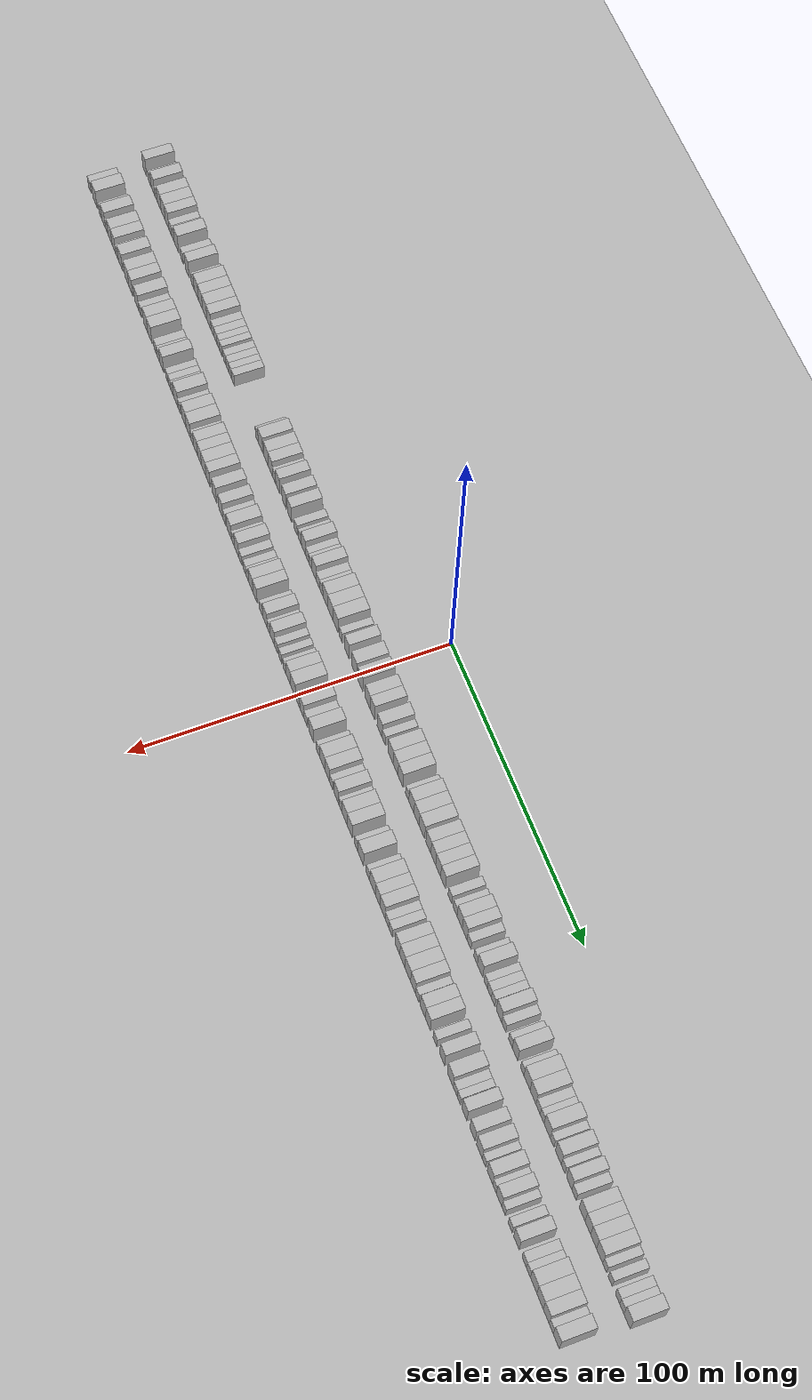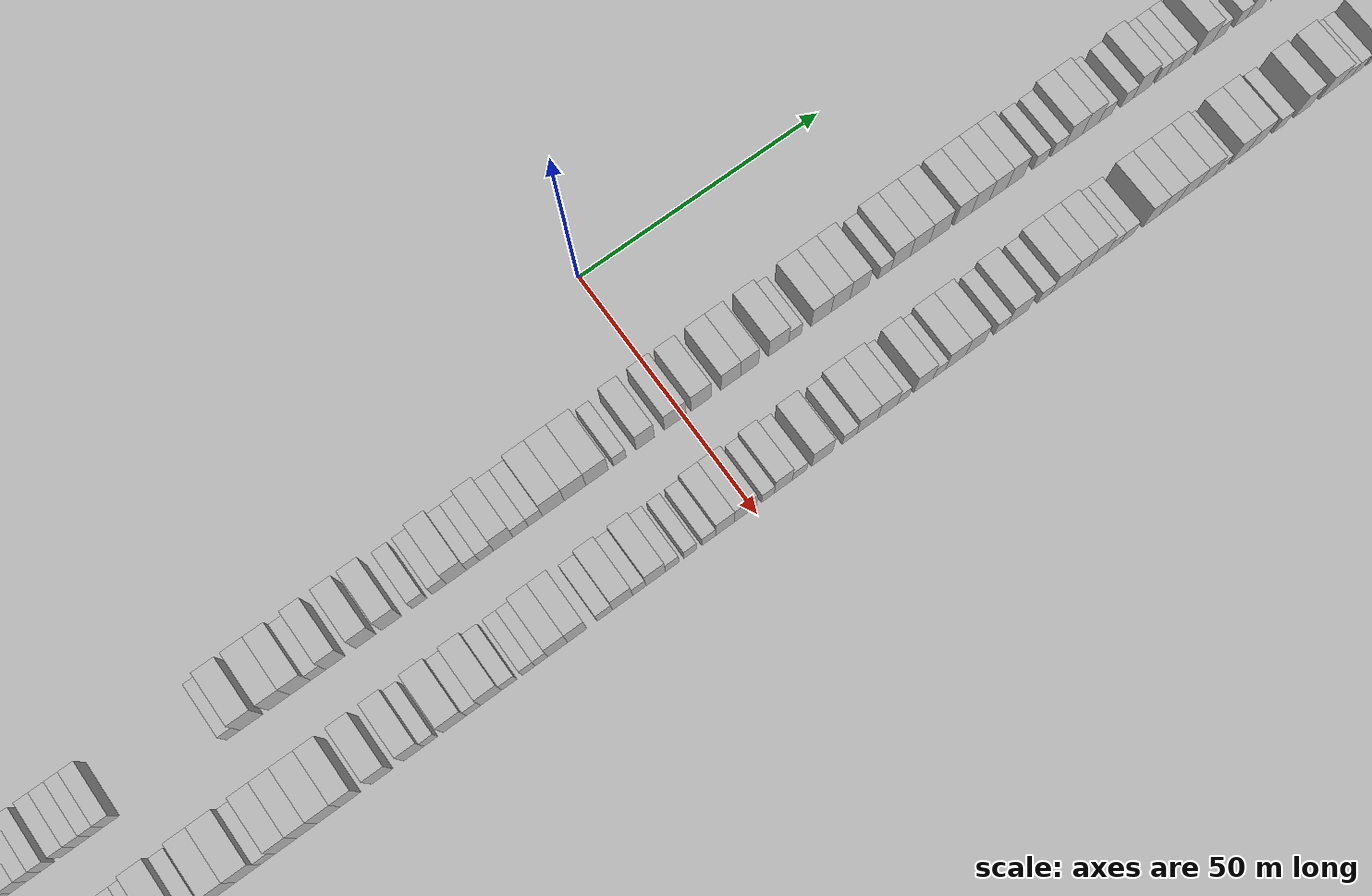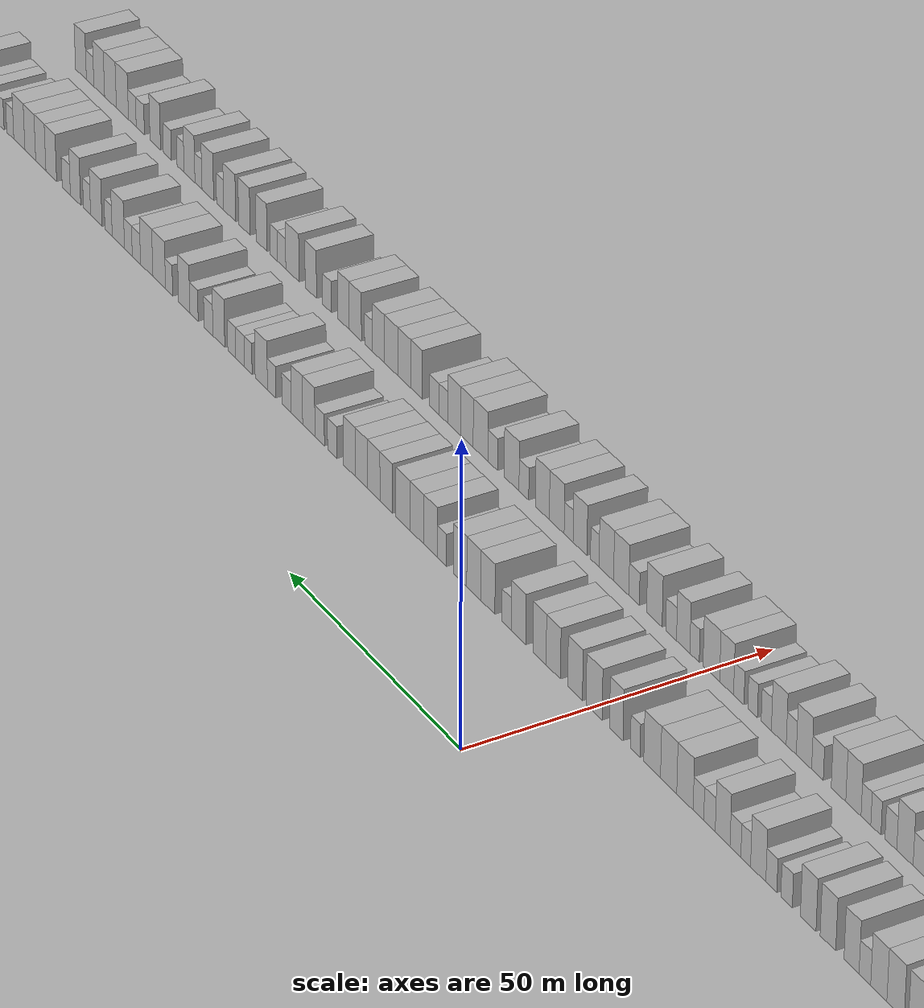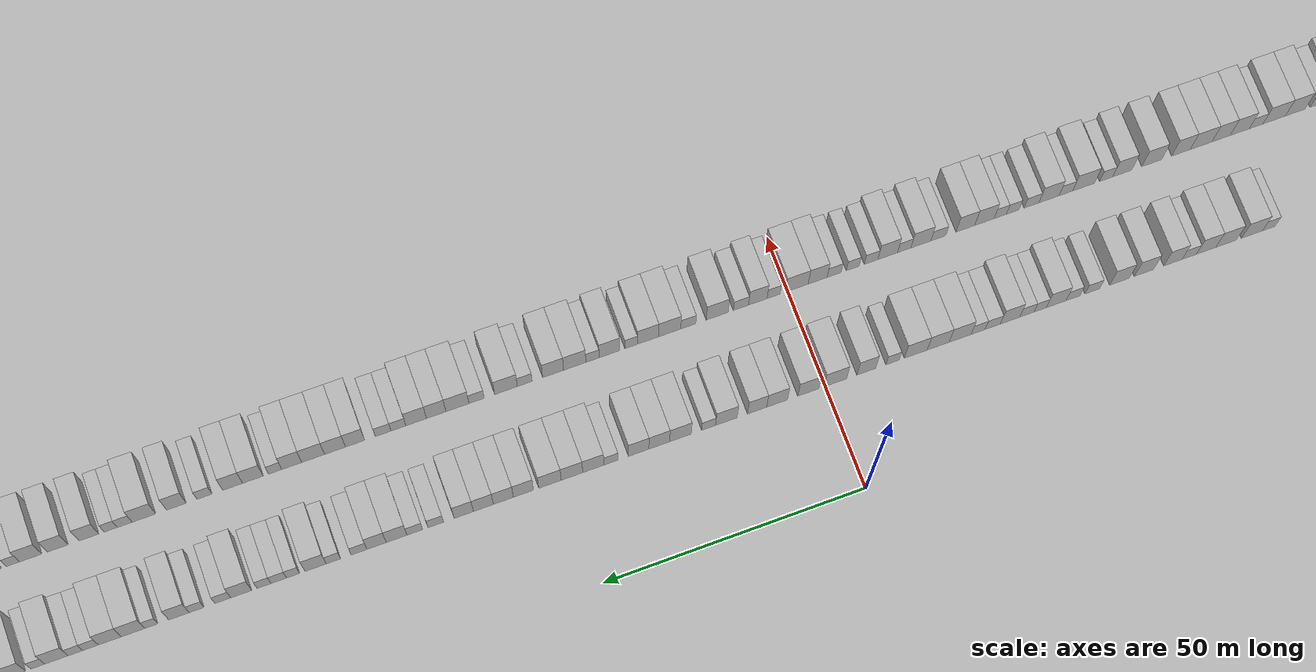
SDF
<?xml version="1.0" encoding="utf-8"?>

<sdf version="1.6">

   <world name="default">

      <gui fullscreen="0">

         <camera name="user_camera">

            <pose>-15 0 4.57585 0 0 0</pose>

            <view_controller>orbit</view_controller>

         </camera>

      </gui>

      <scene>

         <sky>

           <clouds>

             <speed>12</speed>

           </clouds>

         </sky>

         <ambient>0.4 0.4 0.4 1</ambient>

         <background>0.7 0.7 0.7 1</background>

         <shadows>1</shadows>

      </scene>

      <gravity>0 0 -9.8066</gravity>

      <magnetic_field>6e-06 2.3e-05 -4.2e-05</magnetic_field>

      <physics default="0" name="default_physics" type="ode">

         <ode>

            <solver>

               <type>quick</type>

               <iters>10</iters>

               <sor>1.0</sor>

               <use_dynamic_moi_rescaling>0</use_dynamic_moi_rescaling>

            </solver>

            <constraints>

               <cfm>0</cfm>

               <erp>0.2</erp>

               <contact_max_correcting_vel>100</contact_max_correcting_vel>

               <contact_surface_layer>0.001</contact_surface_layer>

            </constraints>

         </ode>

         <max_step_size>0.004</max_step_size>

         <real_time_factor>1</real_time_factor>

         <real_time_update_rate>250</real_time_update_rate>

      </physics>

      <light name="sun" type="directional">

         <cast_shadows>1</cast_shadows>

         <pose>0 0 10 0 0 0</pose>

         <diffuse>0.8 0.8 0.8 1</diffuse>

         <specular>0.2 0.2 0.2 1</specular>

         <attenuation>

            <range>1000</range>

            <constant>0.9</constant>

            <linear>0.01</linear>

            <quadratic>0.001</quadratic>

         </attenuation>

         <direction>-0.5 0.1 -0.9</direction>

      </light>

      <include>

         <name>ground_plane_1</name>

         <uri>model://HANNAS_ground_plane</uri>

         <pose>0 0 0  0 0 0</pose>

      </include>

      <include>

         <name>ground_plane_2</name>

         <uri>model://HANNAS_ground_plane</uri>

         <pose>100 0 0  0 0 0</pose>

      </include>

      <model name="building_1">

         <static>1</static>

         <pose frame="">25.0000 -196.1759 0 0.000000 0.000000 0.000000</pose>

         <link name="link">

            <pose frame="">0 0 4.50 0 0 0</pose>

            <collision name="collision">

               <geometry>

                  <box>

                     <size>10.0000 3.6482 9.0000</size>

                  </box>

               </geometry>

               <max_contacts>10</max_contacts>

               <surface>

                  <contact>

                     <ode/>

                  </contact>

                  <bounce/>

                  <friction>

                     <torsional>

                        <ode/>

                     </torsional>

                     <ode/>

                  </friction>

               </surface>

            </collision>

            <visual name="visual">

               <cast_shadows>0</cast_shadows>

               <geometry>

                  <box>

                     <size>10.0000 3.6482 9.0000</size>

                  </box>

               </geometry>

               <material>

                  <script>

                     <uri>model://HANNAS_wall/materials/scripts</uri>

                     <uri>model://HANNAS_wall/materials/textures</uri>

                     <name>vrc/HANNAS_wall</name>

                  </script>

               </material>

            </visual>

            <self_collide>0</self_collide>

            <enable_wind>0</enable_wind>

            <kinematic>0</kinematic>

         </link>

      </model>

      <model name="building_2">

         <static>1</static>

         <pose frame="">25.0000 -190.9461 0 0.000000 0.000000 0.000000</pose>

         <link name="link">

            <pose frame="">0 0 3.00 0 0 0</pose>

            <collision name="collision">

               <geometry>

                  <box>

                     <size>10.0000 2.8114 6.0000</size>

                  </box>

               </geometry>

               <max_contacts>10</max_contacts>

               <surface>

                  <contact>

                     <ode/>

                  </contact>

                  <bounce/>

                  <friction>

                     <torsional>

                        <ode/>

                     </torsional>

                     <ode/>

                  </friction>

               </surface>

            </collision>

            <visual name="visual">

               <cast_shadows>0</cast_shadows>

               <geometry>

                  <box>

                     <size>10.0000 2.8114 6.0000</size>

                  </box>

               </geometry>

               <material>

                  <script>

                     <uri>model://HANNAS_wall/materials/scripts</uri>

                     <uri>model://HANNAS_wall/materials/textures</uri>

                     <name>vrc/HANNAS_wall</name>

                  </script>

               </material>

            </visual>

            <self_collide>0</self_collide>

            <enable_wind>0</enable_wind>

            <kinematic>0</kinematic>

         </link>

      </model>

      <model name="building_3">

         <static>1</static>

         <pose frame="">25.0000 -187.6219 0 0.000000 0.000000 0.000000</pose>

         <link name="link">

            <pose frame="">0 0 4.50 0 0 0</pose>

            <collision name="collision">

               <geometry>

                  <box>

                     <size>10.0000 3.8369 9.0000</size>

                  </box>

               </geometry>

               <max_contacts>10</max_contacts>

               <surface>

                  <contact>

                     <ode/>

                  </contact>

                  <bounce/>

                  <friction>

                     <torsional>

                        <ode/>

                     </torsional>

                     <ode/>

                  </friction>

               </surface>

            </collision>

            <visual name="visual">

               <cast_shadows>0</cast_shadows>

               <geometry>

                  <box>

                     <size>10.0000 3.8369 9.0000</size>

                  </box>

               </geometry>

               <material>

                  <script>

                     <uri>model://HANNAS_wall/materials/scripts</uri>

                     <uri>model://HANNAS_wall/materials/textures</uri>

                     <name>vrc/HANNAS_wall</name>

                  </script>

               </material>

            </visual>

            <self_collide>0</self_collide>

            <enable_wind>0</enable_wind>

            <kinematic>0</kinematic>

         </link>

      </model>

      <model name="building_4">

         <static>1</static>

         <pose frame="">25.0000 -184.4852 0 0.000000 0.000000 0.000000</pose>

         <link name="link">

            <pose frame="">0 0 3.00 0 0 0</pose>

            <collision name="collision">

               <geometry>

                  <box>

                     <size>10.0000 2.4364 6.0000</size>

                  </box>

               </geometry>

               <max_contacts>10</max_contacts>

               <surface>

                  <contact>

                     <ode/>

                  </contact>

                  <bounce/>

                  <friction>

                     <torsional>

                        <ode/>

                     </torsional>

                     <ode/>

                  </friction>

               </surface>

            </collision>

            <visual name="visual">

               <cast_shadows>0</cast_shadows>

               <geometry>

                  <box>

                     <size>10.0000 2.4364 6.0000</size>

                  </box>

               </geometry>

               <material>

                  <script>

                     <uri>model://HANNAS_wall/materials/scripts</uri>

                     <uri>model://HANNAS_wall/materials/textures</uri>

                     <name>vrc/HANNAS_wall</name>

                  </script>

               </material>

            </visual>

            <self_collide>0</self_collide>

            <enable_wind>0</enable_wind>

            <kinematic>0</kinematic>

         </link>

      </model>

      <model name="building_5">

         <static>1</static>

         <pose frame="">25.0000 -181.3270 0 0.000000 0.000000 0.000000</pose>

         <link name="link">

            <pose frame="">0 0 4.50 0 0 0</pose>

            <collision name="collision">

               <geometry>

                  <box>

                     <size>10.0000 3.8801 9.0000</size>

                  </box>

               </geometry>

               <max_contacts>10</max_contacts>

               <surface>

                  <contact>

                     <ode/>

                  </contact>

                  <bounce/>

                  <friction>

                     <torsional>

                        <ode/>

                     </torsional>

                     <ode/>

                  </friction>

               </surface>

            </collision>

            <visual name="visual">

               <cast_shadows>0</cast_shadows>

               <geometry>

                  <box>

                     <size>10.0000 3.8801 9.0000</size>

                  </box>

               </geometry>

               <material>

                  <script>

                     <uri>model://HANNAS_wall/materials/scripts</uri>

                     <uri>model://HANNAS_wall/materials/textures</uri>

                     <name>vrc/HANNAS_wall</name>

                  </script>

               </material>

            </visual>

            <self_collide>0</self_collide>

            <enable_wind>0</enable_wind>

            <kinematic>0</kinematic>

         </link>

      </model>

      <model name="building_6">

         <static>1</static>

         <pose frame="">25.0000 -177.2706 0 0.000000 0.000000 0.000000</pose>

         <link name="link">

            <pose frame="">0 0 4.50 0 0 0</pose>

            <collision name="collision">

               <geometry>

                  <box>

                     <size>10.0000 4.2327 9.0000</size>

                  </box>

               </geometry>

               <max_contacts>10</max_contacts>

               <surface>

                  <contact>

                     <ode/>

                  </contact>

                  <bounce/>

                  <friction>

                     <torsional>

                        <ode/>

                     </torsional>

                     <ode/>

                  </friction>

               </surface>

            </collision>

            <visual name="visual">

               <cast_shadows>0</cast_shadows>

               <geometry>

                  <box>

                     <size>10.0000 4.2327 9.0000</size>

                  </box>

               </geometry>

               <material>

                  <script>

                     <uri>model://HANNAS_wall/materials/scripts</uri>

                     <uri>model://HANNAS_wall/materials/textures</uri>

                     <name>vrc/HANNAS_wall</name>

                  </script>

               </material>

            </visual>

            <self_collide>0</self_collide>

            <enable_wind>0</enable_wind>

            <kinematic>0</kinematic>

         </link>

      </model>

      <model name="building_7">

         <static>1</static>

         <pose frame="">25.0000 -173.2910 0 0.000000 0.000000 0.000000</pose>

         <link name="link">

            <pose frame="">0 0 4.50 0 0 0</pose>

            <collision name="collision">

               <geometry>

                  <box>

                     <size>10.0000 3.7264 9.0000</size>

                  </box>

               </geometry>

               <max_contacts>10</max_contacts>

               <surface>

                  <contact>

                     <ode/>

                  </contact>

                  <bounce/>

                  <friction>

                     <torsional>

                        <ode/>

                     </torsional>

                     <ode/>

                  </friction>

               </surface>

            </collision>

            <visual name="visual">

               <cast_shadows>0</cast_shadows>

               <geometry>

                  <box>

                     <size>10.0000 3.7264 9.0000</size>

                  </box>

               </geometry>

               <material>

                  <script>

                     <uri>model://HANNAS_wall/materials/scripts</uri>

                     <uri>model://HANNAS_wall/materials/textures</uri>

                     <name>vrc/HANNAS_wall</name>

                  </script>

               </material>

            </visual>

            <self_collide>0</self_collide>

            <enable_wind>0</enable_wind>

            <kinematic>0</kinematic>

         </link>

      </model>

      <model name="building_8">

         <static>1</static>

         <pose frame="">25.0000 -170.0559 0 0.000000 0.000000 0.000000</pose>

         <link name="link">

            <pose frame="">0 0 3.00 0 0 0</pose>

            <collision name="collision">

               <geometry>

                  <box>

                     <size>10.0000 2.7438 6.0000</size>

                  </box>

               </geometry>

               <max_contacts>10</max_contacts>

               <surface>

                  <contact>

                     <ode/>

                  </contact>

                  <bounce/>

                  <friction>

                     <torsional>

                        <ode/>

                     </torsional>

                     <ode/>

                  </friction>

               </surface>

            </collision>

            <visual name="visual">

               <cast_shadows>0</cast_shadows>

               <geometry>

                  <box>

                     <size>10.0000 2.7438 6.0000</size>

                  </box>

               </geometry>

               <material>

                  <script>

                     <uri>model://HANNAS_wall/materials/scripts</uri>

                     <uri>model://HANNAS_wall/materials/textures</uri>

                     <name>vrc/HANNAS_wall</name>

                  </script>

               </material>

            </visual>

            <self_collide>0</self_collide>

            <enable_wind>0</enable_wind>

            <kinematic>0</kinematic>

         </link>

      </model>

      <model name="building_9">

         <static>1</static>

         <pose frame="">25.0000 -167.3676 0 0.000000 0.000000 0.000000</pose>

         <link name="link">

            <pose frame="">0 0 3.00 0 0 0</pose>

            <collision name="collision">

               <geometry>

                  <box>

                     <size>10.0000 2.6329 6.0000</size>

                  </box>

               </geometry>

               <max_contacts>10</max_contacts>

               <surface>

                  <contact>

                     <ode/>

                  </contact>

                  <bounce/>

                  <friction>

                     <torsional>

                        <ode/>

                     </torsional>

                     <ode/>

                  </friction>

               </surface>

            </collision>

            <visual name="visual">

               <cast_shadows>0</cast_shadows>

               <geometry>

                  <box>

                     <size>10.0000 2.6329 6.0000</size>

                  </box>

               </geometry>

               <material>

                  <script>

                     <uri>model://HANNAS_wall/materials/scripts</uri>

                     <uri>model://HANNAS_wall/materials/textures</uri>

                     <name>vrc/HANNAS_wall</name>

                  </script>

               </material>

            </visual>

            <self_collide>0</self_collide>

            <enable_wind>0</enable_wind>

            <kinematic>0</kinematic>

         </link>

      </model>

      <model name="building_10">

         <static>1</static>

         <pose frame="">25.0000 -163.9281 0 0.000000 0.000000 0.000000</pose>

         <link name="link">

            <pose frame="">0 0 4.50 0 0 0</pose>

            <collision name="collision">

               <geometry>

                  <box>

                     <size>10.0000 4.2461 9.0000</size>

                  </box>

               </geometry>

               <max_contacts>10</max_contacts>

               <surface>

                  <contact>

                     <ode/>

                  </contact>

                  <bounce/>

                  <friction>

                     <torsional>

                        <ode/>

                     </torsional>

                     <ode/>

                  </friction>

               </surface>

            </collision>

            <visual name="visual">

               <cast_shadows>0</cast_shadows>

               <geometry>

                  <box>

                     <size>10.0000 4.2461 9.0000</size>

                  </box>

               </geometry>

               <material>

                  <script>

                     <uri>model://HANNAS_wall/materials/scripts</uri>

                     <uri>model://HANNAS_wall/materials/textures</uri>

                     <name>vrc/HANNAS_wall</name>

                  </script>

               </material>

            </visual>

            <self_collide>0</self_collide>

            <enable_wind>0</enable_wind>

            <kinematic>0</kinematic>

         </link>

      </model>

      <model name="building_11">

         <static>1</static>

         <pose frame="">25.0000 -158.4023 0 0.000000 0.000000 0.000000</pose>

         <link name="link">

            <pose frame="">0 0 3.00 0 0 0</pose>

            <collision name="collision">

               <geometry>

                  <box>

                     <size>10.0000 2.8056 6.0000</size>

                  </box>

               </geometry>

               <max_contacts>10</max_contacts>

               <surface>

                  <contact>

                     <ode/>

                  </contact>

                  <bounce/>

                  <friction>

                     <torsional>

                        <ode/>

                     </torsional>

                     <ode/>

                  </friction>

               </surface>

            </collision>

            <visual name="visual">

               <cast_shadows>0</cast_shadows>

               <geometry>

                  <box>

                     <size>10.0000 2.8056 6.0000</size>

                  </box>

               </geometry>

               <material>

                  <script>

                     <uri>model://HANNAS_wall/materials/scripts</uri>

                     <uri>model://HANNAS_wall/materials/textures</uri>

                     <name>vrc/HANNAS_wall</name>

                  </script>

               </material>

            </visual>

            <self_collide>0</self_collide>

            <enable_wind>0</enable_wind>

            <kinematic>0</kinematic>

         </link>

      </model>

      <model name="building_12">

         <static>1</static>

         <pose frame="">25.0000 -153.1148 0 0.000000 0.000000 0.000000</pose>

         <link name="link">

            <pose frame="">0 0 4.50 0 0 0</pose>

            <collision name="collision">

               <geometry>

                  <box>

                     <size>10.0000 3.7693 9.0000</size>

                  </box>

               </geometry>

               <max_contacts>10</max_contacts>

               <surface>

                  <contact>

                     <ode/>

                  </contact>

                  <bounce/>

                  <friction>

                     <torsional>

                        <ode/>

                     </torsional>

                     <ode/>

                  </friction>

               </surface>

            </collision>

            <visual name="visual">

               <cast_shadows>0</cast_shadows>

               <geometry>

                  <box>

                     <size>10.0000 3.7693 9.0000</size>

                  </box>

               </geometry>

               <material>

                  <script>

                     <uri>model://HANNAS_wall/materials/scripts</uri>

                     <uri>model://HANNAS_wall/materials/textures</uri>

                     <name>vrc/HANNAS_wall</name>

                  </script>

               </material>

            </visual>

            <self_collide>0</self_collide>

            <enable_wind>0</enable_wind>

            <kinematic>0</kinematic>

         </link>

      </model>

      <model name="building_13">

         <static>1</static>

         <pose frame="">25.0000 -147.7984 0 0.000000 0.000000 0.000000</pose>

         <link name="link">

            <pose frame="">0 0 3.00 0 0 0</pose>

            <collision name="collision">

               <geometry>

                  <box>

                     <size>10.0000 2.8636 6.0000</size>

                  </box>

               </geometry>

               <max_contacts>10</max_contacts>

               <surface>

                  <contact>

                     <ode/>

                  </contact>

                  <bounce/>

                  <friction>

                     <torsional>

                        <ode/>

                     </torsional>

                     <ode/>

                  </friction>

               </surface>

            </collision>

            <visual name="visual">

               <cast_shadows>0</cast_shadows>

               <geometry>

                  <box>

                     <size>10.0000 2.8636 6.0000</size>

                  </box>

               </geometry>

               <material>

                  <script>

                     <uri>model://HANNAS_wall/materials/scripts</uri>

                     <uri>model://HANNAS_wall/materials/textures</uri>

                     <name>vrc/HANNAS_wall</name>

                  </script>

               </material>

            </visual>

            <self_collide>0</self_collide>

            <enable_wind>0</enable_wind>

            <kinematic>0</kinematic>

         </link>

      </model>

      <model name="building_14">

         <static>1</static>

         <pose frame="">25.0000 -144.2717 0 0.000000 0.000000 0.000000</pose>

         <link name="link">

            <pose frame="">0 0 4.50 0 0 0</pose>

            <collision name="collision">

               <geometry>

                  <box>

                     <size>10.0000 4.1898 9.0000</size>

                  </box>

               </geometry>

               <max_contacts>10</max_contacts>

               <surface>

                  <contact>

                     <ode/>

                  </contact>

                  <bounce/>

                  <friction>

                     <torsional>

                        <ode/>

                     </torsional>

                     <ode/>

                  </friction>

               </surface>

            </collision>

            <visual name="visual">

               <cast_shadows>0</cast_shadows>

               <geometry>

                  <box>

                     <size>10.0000 4.1898 9.0000</size>

                  </box>

               </geometry>

               <material>

                  <script>

                     <uri>model://HANNAS_wall/materials/scripts</uri>

                     <uri>model://HANNAS_wall/materials/textures</uri>

                     <name>vrc/HANNAS_wall</name>

                  </script>

               </material>

            </visual>

            <self_collide>0</self_collide>

            <enable_wind>0</enable_wind>

            <kinematic>0</kinematic>

         </link>

      </model>

      <model name="building_15">

         <static>1</static>

         <pose frame="">25.0000 -140.1707 0 0.000000 0.000000 0.000000</pose>

         <link name="link">

            <pose frame="">0 0 4.50 0 0 0</pose>

            <collision name="collision">

               <geometry>

                  <box>

                     <size>10.0000 4.0121 9.0000</size>

                  </box>

               </geometry>

               <max_contacts>10</max_contacts>

               <surface>

                  <contact>

                     <ode/>

                  </contact>

                  <bounce/>

                  <friction>

                     <torsional>

                        <ode/>

                     </torsional>

                     <ode/>

                  </friction>

               </surface>

            </collision>

            <visual name="visual">

               <cast_shadows>0</cast_shadows>

               <geometry>

                  <box>

                     <size>10.0000 4.0121 9.0000</size>

                  </box>

               </geometry>

               <material>

                  <script>

                     <uri>model://HANNAS_wall/materials/scripts</uri>

                     <uri>model://HANNAS_wall/materials/textures</uri>

                     <name>vrc/HANNAS_wall</name>

                  </script>

               </material>

            </visual>

            <self_collide>0</self_collide>

            <enable_wind>0</enable_wind>

            <kinematic>0</kinematic>

         </link>

      </model>

      <model name="building_16">

         <static>1</static>

         <pose frame="">25.0000 -135.9625 0 0.000000 0.000000 0.000000</pose>

         <link name="link">

            <pose frame="">0 0 4.50 0 0 0</pose>

            <collision name="collision">

               <geometry>

                  <box>

                     <size>10.0000 4.4043 9.0000</size>

                  </box>

               </geometry>

               <max_contacts>10</max_contacts>

               <surface>

                  <contact>

                     <ode/>

                  </contact>

                  <bounce/>

                  <friction>

                     <torsional>

                        <ode/>

                     </torsional>

                     <ode/>

                  </friction>

               </surface>

            </collision>

            <visual name="visual">

               <cast_shadows>0</cast_shadows>

               <geometry>

                  <box>

                     <size>10.0000 4.4043 9.0000</size>

                  </box>

               </geometry>

               <material>

                  <script>

                     <uri>model://HANNAS_wall/materials/scripts</uri>

                     <uri>model://HANNAS_wall/materials/textures</uri>

                     <name>vrc/HANNAS_wall</name>

                  </script>

               </material>

            </visual>

            <self_collide>0</self_collide>

            <enable_wind>0</enable_wind>

            <kinematic>0</kinematic>

         </link>

      </model>

      <model name="building_17">

         <static>1</static>

         <pose frame="">25.0000 -131.8320 0 0.000000 0.000000 0.000000</pose>

         <link name="link">

            <pose frame="">0 0 4.50 0 0 0</pose>

            <collision name="collision">

               <geometry>

                  <box>

                     <size>10.0000 3.8568 9.0000</size>

                  </box>

               </geometry>

               <max_contacts>10</max_contacts>

               <surface>

                  <contact>

                     <ode/>

                  </contact>

                  <bounce/>

                  <friction>

                     <torsional>

                        <ode/>

                     </torsional>

                     <ode/>

                  </friction>

               </surface>

            </collision>

            <visual name="visual">

               <cast_shadows>0</cast_shadows>

               <geometry>

                  <box>

                     <size>10.0000 3.8568 9.0000</size>

                  </box>

               </geometry>

               <material>

                  <script>

                     <uri>model://HANNAS_wall/materials/scripts</uri>

                     <uri>model://HANNAS_wall/materials/textures</uri>

                     <name>vrc/HANNAS_wall</name>

                  </script>

               </material>

            </visual>

            <self_collide>0</self_collide>

            <enable_wind>0</enable_wind>

            <kinematic>0</kinematic>

         </link>

      </model>

      <model name="building_18">

         <static>1</static>

         <pose frame="">25.0000 -128.4535 0 0.000000 0.000000 0.000000</pose>

         <link name="link">

            <pose frame="">0 0 3.00 0 0 0</pose>

            <collision name="collision">

               <geometry>

                  <box>

                     <size>10.0000 2.9002 6.0000</size>

                  </box>

               </geometry>

               <max_contacts>10</max_contacts>

               <surface>

                  <contact>

                     <ode/>

                  </contact>

                  <bounce/>

                  <friction>

                     <torsional>

                        <ode/>

                     </torsional>

                     <ode/>

                  </friction>

               </surface>

            </collision>

            <visual name="visual">

               <cast_shadows>0</cast_shadows>

               <geometry>

                  <box>

                     <size>10.0000 2.9002 6.0000</size>

                  </box>

               </geometry>

               <material>

                  <script>

                     <uri>model://HANNAS_wall/materials/scripts</uri>

                     <uri>model://HANNAS_wall/materials/textures</uri>

                     <name>vrc/HANNAS_wall</name>

                  </script>

               </material>

            </visual>

            <self_collide>0</self_collide>

            <enable_wind>0</enable_wind>

            <kinematic>0</kinematic>

         </link>

      </model>

      <model name="building_19">

         <static>1</static>

         <pose frame="">25.0000 -125.5418 0 0.000000 0.000000 0.000000</pose>

         <link name="link">

            <pose frame="">0 0 3.00 0 0 0</pose>

            <collision name="collision">

               <geometry>

                  <box>

                     <size>10.0000 2.9231 6.0000</size>

                  </box>

               </geometry>

               <max_contacts>10</max_contacts>

               <surface>

                  <contact>

                     <ode/>

                  </contact>

                  <bounce/>

                  <friction>

                     <torsional>

                        <ode/>

                     </torsional>

                     <ode/>

                  </friction>

               </surface>

            </collision>

            <visual name="visual">

               <cast_shadows>0</cast_shadows>

               <geometry>

                  <box>

                     <size>10.0000 2.9231 6.0000</size>

                  </box>

               </geometry>

               <material>

                  <script>

                     <uri>model://HANNAS_wall/materials/scripts</uri>

                     <uri>model://HANNAS_wall/materials/textures</uri>

                     <name>vrc/HANNAS_wall</name>

                  </script>

               </material>

            </visual>

            <self_collide>0</self_collide>

            <enable_wind>0</enable_wind>

            <kinematic>0</kinematic>

         </link>

      </model>

      <model name="building_20">

         <static>1</static>

         <pose frame="">25.0000 -122.8509 0 0.000000 0.000000 0.000000</pose>

         <link name="link">

            <pose frame="">0 0 3.00 0 0 0</pose>

            <collision name="collision">

               <geometry>

                  <box>

                     <size>10.0000 2.4586 6.0000</size>

                  </box>

               </geometry>

               <max_contacts>10</max_contacts>

               <surface>

                  <contact>

                     <ode/>

                  </contact>

                  <bounce/>

                  <friction>

                     <torsional>

                        <ode/>

                     </torsional>

                     <ode/>

                  </friction>

               </surface>

            </collision>

            <visual name="visual">

               <cast_shadows>0</cast_shadows>

               <geometry>

                  <box>

                     <size>10.0000 2.4586 6.0000</size>

                  </box>

               </geometry>

               <material>

                  <script>

                     <uri>model://HANNAS_wall/materials/scripts</uri>

                     <uri>model://HANNAS_wall/materials/textures</uri>

                     <name>vrc/HANNAS_wall</name>

                  </script>

               </material>

            </visual>

            <self_collide>0</self_collide>

            <enable_wind>0</enable_wind>

            <kinematic>0</kinematic>

         </link>

      </model>

      <model name="building_21">

         <static>1</static>

         <pose frame="">25.0000 -120.3759 0 0.000000 0.000000 0.000000</pose>

         <link name="link">

            <pose frame="">0 0 3.00 0 0 0</pose>

            <collision name="collision">

               <geometry>

                  <box>

                     <size>10.0000 2.4915 6.0000</size>

                  </box>

               </geometry>

               <max_contacts>10</max_contacts>

               <surface>

                  <contact>

                     <ode/>

                  </contact>

                  <bounce/>

                  <friction>

                     <torsional>

                        <ode/>

                     </torsional>

                     <ode/>

                  </friction>

               </surface>

            </collision>

            <visual name="visual">

               <cast_shadows>0</cast_shadows>

               <geometry>

                  <box>

                     <size>10.0000 2.4915 6.0000</size>

                  </box>

               </geometry>

               <material>

                  <script>

                     <uri>model://HANNAS_wall/materials/scripts</uri>

                     <uri>model://HANNAS_wall/materials/textures</uri>

                     <name>vrc/HANNAS_wall</name>

                  </script>

               </material>

            </visual>

            <self_collide>0</self_collide>

            <enable_wind>0</enable_wind>

            <kinematic>0</kinematic>

         </link>

      </model>

      <model name="building_22">

         <static>1</static>

         <pose frame="">25.0000 -116.8261 0 0.000000 0.000000 0.000000</pose>

         <link name="link">

            <pose frame="">0 0 3.00 0 0 0</pose>

            <collision name="collision">

               <geometry>

                  <box>

                     <size>10.0000 2.6081 6.0000</size>

                  </box>

               </geometry>

               <max_contacts>10</max_contacts>

               <surface>

                  <contact>

                     <ode/>

                  </contact>

                  <bounce/>

                  <friction>

                     <torsional>

                        <ode/>

                     </torsional>

                     <ode/>

                  </friction>

               </surface>

            </collision>

            <visual name="visual">

               <cast_shadows>0</cast_shadows>

               <geometry>

                  <box>

                     <size>10.0000 2.6081 6.0000</size>

                  </box>

               </geometry>

               <material>

                  <script>

                     <uri>model://HANNAS_wall/materials/scripts</uri>

                     <uri>model://HANNAS_wall/materials/textures</uri>

                     <name>vrc/HANNAS_wall</name>

                  </script>

               </material>

            </visual>

            <self_collide>0</self_collide>

            <enable_wind>0</enable_wind>

            <kinematic>0</kinematic>

         </link>

      </model>

      <model name="building_23">

         <static>1</static>

         <pose frame="">25.0000 -114.1578 0 0.000000 0.000000 0.000000</pose>

         <link name="link">

            <pose frame="">0 0 3.00 0 0 0</pose>

            <collision name="collision">

               <geometry>

                  <box>

                     <size>10.0000 2.7284 6.0000</size>

                  </box>

               </geometry>

               <max_contacts>10</max_contacts>

               <surface>

                  <contact>

                     <ode/>

                  </contact>

                  <bounce/>

                  <friction>

                     <torsional>

                        <ode/>

                     </torsional>

                     <ode/>

                  </friction>

               </surface>

            </collision>

            <visual name="visual">

               <cast_shadows>0</cast_shadows>

               <geometry>

                  <box>

                     <size>10.0000 2.7284 6.0000</size>

                  </box>

               </geometry>

               <material>

                  <script>

                     <uri>model://HANNAS_wall/materials/scripts</uri>

                     <uri>model://HANNAS_wall/materials/textures</uri>

                     <name>vrc/HANNAS_wall</name>

                  </script>

               </material>

            </visual>

            <self_collide>0</self_collide>

            <enable_wind>0</enable_wind>

            <kinematic>0</kinematic>

         </link>

      </model>

      <model name="building_24">

         <static>1</static>

         <pose frame="">25.0000 -111.5597 0 0.000000 0.000000 0.000000</pose>

         <link name="link">

            <pose frame="">0 0 3.00 0 0 0</pose>

            <collision name="collision">

               <geometry>

                  <box>

                     <size>10.0000 2.4680 6.0000</size>

                  </box>

               </geometry>

               <max_contacts>10</max_contacts>

               <surface>

                  <contact>

                     <ode/>

                  </contact>

                  <bounce/>

                  <friction>

                     <torsional>

                        <ode/>

                     </torsional>

                     <ode/>

                  </friction>

               </surface>

            </collision>

            <visual name="visual">

               <cast_shadows>0</cast_shadows>

               <geometry>

                  <box>

                     <size>10.0000 2.4680 6.0000</size>

                  </box>

               </geometry>

               <material>

                  <script>

                     <uri>model://HANNAS_wall/materials/scripts</uri>

                     <uri>model://HANNAS_wall/materials/textures</uri>

                     <name>vrc/HANNAS_wall</name>

                  </script>

               </material>

            </visual>

            <self_collide>0</self_collide>

            <enable_wind>0</enable_wind>

            <kinematic>0</kinematic>

         </link>

      </model>

      <model name="building_25">

         <static>1</static>

         <pose frame="">25.0000 -108.9329 0 0.000000 0.000000 0.000000</pose>

         <link name="link">

            <pose frame="">0 0 3.00 0 0 0</pose>

            <collision name="collision">

               <geometry>

                  <box>

                     <size>10.0000 2.7856 6.0000</size>

                  </box>

               </geometry>

               <max_contacts>10</max_contacts>

               <surface>

                  <contact>

                     <ode/>

                  </contact>

                  <bounce/>

                  <friction>

                     <torsional>

                        <ode/>

                     </torsional>

                     <ode/>

                  </friction>

               </surface>

            </collision>

            <visual name="visual">

               <cast_shadows>0</cast_shadows>

               <geometry>

                  <box>

                     <size>10.0000 2.7856 6.0000</size>

                  </box>

               </geometry>

               <material>

                  <script>

                     <uri>model://HANNAS_wall/materials/scripts</uri>

                     <uri>model://HANNAS_wall/materials/textures</uri>

                     <name>vrc/HANNAS_wall</name>

                  </script>

               </material>

            </visual>

            <self_collide>0</self_collide>

            <enable_wind>0</enable_wind>

            <kinematic>0</kinematic>

         </link>

      </model>

      <model name="building_26">

         <static>1</static>

         <pose frame="">25.0000 -86.7555 0 0.000000 0.000000 0.000000</pose>

         <link name="link">

            <pose frame="">0 0 3.00 0 0 0</pose>

            <collision name="collision">

               <geometry>

                  <box>

                     <size>10.0000 2.5230 6.0000</size>

                  </box>

               </geometry>

               <max_contacts>10</max_contacts>

               <surface>

                  <contact>

                     <ode/>

                  </contact>

                  <bounce/>

                  <friction>

                     <torsional>

                        <ode/>

                     </torsional>

                     <ode/>

                  </friction>

               </surface>

            </collision>

            <visual name="visual">

               <cast_shadows>0</cast_shadows>

               <geometry>

                  <box>

                     <size>10.0000 2.5230 6.0000</size>

                  </box>

               </geometry>

               <material>

                  <script>

                     <uri>model://HANNAS_wall/materials/scripts</uri>

                     <uri>model://HANNAS_wall/materials/textures</uri>

                     <name>vrc/HANNAS_wall</name>

                  </script>

               </material>

            </visual>

            <self_collide>0</self_collide>

            <enable_wind>0</enable_wind>

            <kinematic>0</kinematic>

         </link>

      </model>

      <model name="building_27">

         <static>1</static>

         <pose frame="">25.0000 -83.4109 0 0.000000 0.000000 0.000000</pose>

         <link name="link">

            <pose frame="">0 0 4.50 0 0 0</pose>

            <collision name="collision">

               <geometry>

                  <box>

                     <size>10.0000 4.1663 9.0000</size>

                  </box>

               </geometry>

               <max_contacts>10</max_contacts>

               <surface>

                  <contact>

                     <ode/>

                  </contact>

                  <bounce/>

                  <friction>

                     <torsional>

                        <ode/>

                     </torsional>

                     <ode/>

                  </friction>

               </surface>

            </collision>

            <visual name="visual">

               <cast_shadows>0</cast_shadows>

               <geometry>

                  <box>

                     <size>10.0000 4.1663 9.0000</size>

                  </box>

               </geometry>

               <material>

                  <script>

                     <uri>model://HANNAS_wall/materials/scripts</uri>

                     <uri>model://HANNAS_wall/materials/textures</uri>

                     <name>vrc/HANNAS_wall</name>

                  </script>

               </material>

            </visual>

            <self_collide>0</self_collide>

            <enable_wind>0</enable_wind>

            <kinematic>0</kinematic>

         </link>

      </model>

      <model name="building_28">

         <static>1</static>

         <pose frame="">25.0000 -78.2831 0 0.000000 0.000000 0.000000</pose>

         <link name="link">

            <pose frame="">0 0 4.50 0 0 0</pose>

            <collision name="collision">

               <geometry>

                  <box>

                     <size>10.0000 4.0893 9.0000</size>

                  </box>

               </geometry>

               <max_contacts>10</max_contacts>

               <surface>

                  <contact>

                     <ode/>

                  </contact>

                  <bounce/>

                  <friction>

                     <torsional>

                        <ode/>

                     </torsional>

                     <ode/>

                  </friction>

               </surface>

            </collision>

            <visual name="visual">

               <cast_shadows>0</cast_shadows>

               <geometry>

                  <box>

                     <size>10.0000 4.0893 9.0000</size>

                  </box>

               </geometry>

               <material>

                  <script>

                     <uri>model://HANNAS_wall/materials/scripts</uri>

                     <uri>model://HANNAS_wall/materials/textures</uri>

                     <name>vrc/HANNAS_wall</name>

                  </script>

               </material>

            </visual>

            <self_collide>0</self_collide>

            <enable_wind>0</enable_wind>

            <kinematic>0</kinematic>

         </link>

      </model>

      <model name="building_29">

         <static>1</static>

         <pose frame="">25.0000 -74.3078 0 0.000000 0.000000 0.000000</pose>

         <link name="link">

            <pose frame="">0 0 4.50 0 0 0</pose>

            <collision name="collision">

               <geometry>

                  <box>

                     <size>10.0000 3.8613 9.0000</size>

                  </box>

               </geometry>

               <max_contacts>10</max_contacts>

               <surface>

                  <contact>

                     <ode/>

                  </contact>

                  <bounce/>

                  <friction>

                     <torsional>

                        <ode/>

                     </torsional>

                     <ode/>

                  </friction>

               </surface>

            </collision>

            <visual name="visual">

               <cast_shadows>0</cast_shadows>

               <geometry>

                  <box>

                     <size>10.0000 3.8613 9.0000</size>

                  </box>

               </geometry>

               <material>

                  <script>

                     <uri>model://HANNAS_wall/materials/scripts</uri>

                     <uri>model://HANNAS_wall/materials/textures</uri>

                     <name>vrc/HANNAS_wall</name>

                  </script>

               </material>

            </visual>

            <self_collide>0</self_collide>

            <enable_wind>0</enable_wind>

            <kinematic>0</kinematic>

         </link>

      </model>

      <model name="building_30">

         <static>1</static>

         <pose frame="">25.0000 -70.9786 0 0.000000 0.000000 0.000000</pose>

         <link name="link">

            <pose frame="">0 0 3.00 0 0 0</pose>

            <collision name="collision">

               <geometry>

                  <box>

                     <size>10.0000 2.7971 6.0000</size>

                  </box>

               </geometry>

               <max_contacts>10</max_contacts>

               <surface>

                  <contact>

                     <ode/>

                  </contact>

                  <bounce/>

                  <friction>

                     <torsional>

                        <ode/>

                     </torsional>

                     <ode/>

                  </friction>

               </surface>

            </collision>

            <visual name="visual">

               <cast_shadows>0</cast_shadows>

               <geometry>

                  <box>

                     <size>10.0000 2.7971 6.0000</size>

                  </box>

               </geometry>

               <material>

                  <script>

                     <uri>model://HANNAS_wall/materials/scripts</uri>

                     <uri>model://HANNAS_wall/materials/textures</uri>

                     <name>vrc/HANNAS_wall</name>

                  </script>

               </material>

            </visual>

            <self_collide>0</self_collide>

            <enable_wind>0</enable_wind>

            <kinematic>0</kinematic>

         </link>

      </model>

      <model name="building_31">

         <static>1</static>

         <pose frame="">25.0000 -67.7646 0 0.000000 0.000000 0.000000</pose>

         <link name="link">

            <pose frame="">0 0 4.50 0 0 0</pose>

            <collision name="collision">

               <geometry>

                  <box>

                     <size>10.0000 3.6309 9.0000</size>

                  </box>

               </geometry>

               <max_contacts>10</max_contacts>

               <surface>

                  <contact>

                     <ode/>

                  </contact>

                  <bounce/>

                  <friction>

                     <torsional>

                        <ode/>

                     </torsional>

                     <ode/>

                  </friction>

               </surface>

            </collision>

            <visual name="visual">

               <cast_shadows>0</cast_shadows>

               <geometry>

                  <box>

                     <size>10.0000 3.6309 9.0000</size>

                  </box>

               </geometry>

               <material>

                  <script>

                     <uri>model://HANNAS_wall/materials/scripts</uri>

                     <uri>model://HANNAS_wall/materials/textures</uri>

                     <name>vrc/HANNAS_wall</name>

                  </script>

               </material>

            </visual>

            <self_collide>0</self_collide>

            <enable_wind>0</enable_wind>

            <kinematic>0</kinematic>

         </link>

      </model>

      <model name="building_32">

         <static>1</static>

         <pose frame="">25.0000 -62.0413 0 0.000000 0.000000 0.000000</pose>

         <link name="link">

            <pose frame="">0 0 4.50 0 0 0</pose>

            <collision name="collision">

               <geometry>

                  <box>

                     <size>10.0000 3.8157 9.0000</size>

                  </box>

               </geometry>

               <max_contacts>10</max_contacts>

               <surface>

                  <contact>

                     <ode/>

                  </contact>

                  <bounce/>

                  <friction>

                     <torsional>

                        <ode/>

                     </torsional>

                     <ode/>

                  </friction>

               </surface>

            </collision>

            <visual name="visual">

               <cast_shadows>0</cast_shadows>

               <geometry>

                  <box>

                     <size>10.0000 3.8157 9.0000</size>

                  </box>

               </geometry>

               <material>

                  <script>

                     <uri>model://HANNAS_wall/materials/scripts</uri>

                     <uri>model://HANNAS_wall/materials/textures</uri>

                     <name>vrc/HANNAS_wall</name>

                  </script>

               </material>

            </visual>

            <self_collide>0</self_collide>

            <enable_wind>0</enable_wind>

            <kinematic>0</kinematic>

         </link>

      </model>

      <model name="building_33">

         <static>1</static>

         <pose frame="">25.0000 -57.2095 0 0.000000 0.000000 0.000000</pose>

         <link name="link">

            <pose frame="">0 0 4.50 0 0 0</pose>

            <collision name="collision">

               <geometry>

                  <box>

                     <size>10.0000 3.8478 9.0000</size>

                  </box>

               </geometry>

               <max_contacts>10</max_contacts>

               <surface>

                  <contact>

                     <ode/>

                  </contact>

                  <bounce/>

                  <friction>

                     <torsional>

                        <ode/>

                     </torsional>

                     <ode/>

                  </friction>

               </surface>

            </collision>

            <visual name="visual">

               <cast_shadows>0</cast_shadows>

               <geometry>

                  <box>

                     <size>10.0000 3.8478 9.0000</size>

                  </box>

               </geometry>

               <material>

                  <script>

                     <uri>model://HANNAS_wall/materials/scripts</uri>

                     <uri>model://HANNAS_wall/materials/textures</uri>

                     <name>vrc/HANNAS_wall</name>

                  </script>

               </material>

            </visual>

            <self_collide>0</self_collide>

            <enable_wind>0</enable_wind>

            <kinematic>0</kinematic>

         </link>

      </model>

      <model name="building_34">

         <static>1</static>

         <pose frame="">25.0000 -51.8586 0 0.000000 0.000000 0.000000</pose>

         <link name="link">

            <pose frame="">0 0 3.00 0 0 0</pose>

            <collision name="collision">

               <geometry>

                  <box>

                     <size>10.0000 2.8540 6.0000</size>

                  </box>

               </geometry>

               <max_contacts>10</max_contacts>

               <surface>

                  <contact>

                     <ode/>

                  </contact>

                  <bounce/>

                  <friction>

                     <torsional>

                        <ode/>

                     </torsional>

                     <ode/>

                  </friction>

               </surface>

            </collision>

            <visual name="visual">

               <cast_shadows>0</cast_shadows>

               <geometry>

                  <box>

                     <size>10.0000 2.8540 6.0000</size>

                  </box>

               </geometry>

               <material>

                  <script>

                     <uri>model://HANNAS_wall/materials/scripts</uri>

                     <uri>model://HANNAS_wall/materials/textures</uri>

                     <name>vrc/HANNAS_wall</name>

                  </script>

               </material>

            </visual>

            <self_collide>0</self_collide>

            <enable_wind>0</enable_wind>

            <kinematic>0</kinematic>

         </link>

      </model>

      <model name="building_35">

         <static>1</static>

         <pose frame="">25.0000 -48.0575 0 0.000000 0.000000 0.000000</pose>

         <link name="link">

            <pose frame="">0 0 3.00 0 0 0</pose>

            <collision name="collision">

               <geometry>

                  <box>

                     <size>10.0000 2.7484 6.0000</size>

                  </box>

               </geometry>

               <max_contacts>10</max_contacts>

               <surface>

                  <contact>

                     <ode/>

                  </contact>

                  <bounce/>

                  <friction>

                     <torsional>

                        <ode/>

                     </torsional>

                     <ode/>

                  </friction>

               </surface>

            </collision>

            <visual name="visual">

               <cast_shadows>0</cast_shadows>

               <geometry>

                  <box>

                     <size>10.0000 2.7484 6.0000</size>

                  </box>

               </geometry>

               <material>

                  <script>

                     <uri>model://HANNAS_wall/materials/scripts</uri>

                     <uri>model://HANNAS_wall/materials/textures</uri>

                     <name>vrc/HANNAS_wall</name>

                  </script>

               </material>

            </visual>

            <self_collide>0</self_collide>

            <enable_wind>0</enable_wind>

            <kinematic>0</kinematic>

         </link>

      </model>

      <model name="building_36">

         <static>1</static>

         <pose frame="">25.0000 -44.7523 0 0.000000 0.000000 0.000000</pose>

         <link name="link">

            <pose frame="">0 0 4.50 0 0 0</pose>

            <collision name="collision">

               <geometry>

                  <box>

                     <size>10.0000 3.8620 9.0000</size>

                  </box>

               </geometry>

               <max_contacts>10</max_contacts>

               <surface>

                  <contact>

                     <ode/>

                  </contact>

                  <bounce/>

                  <friction>

                     <torsional>

                        <ode/>

                     </torsional>

                     <ode/>

                  </friction>

               </surface>

            </collision>

            <visual name="visual">

               <cast_shadows>0</cast_shadows>

               <geometry>

                  <box>

                     <size>10.0000 3.8620 9.0000</size>

                  </box>

               </geometry>

               <material>

                  <script>

                     <uri>model://HANNAS_wall/materials/scripts</uri>

                     <uri>model://HANNAS_wall/materials/textures</uri>

                     <name>vrc/HANNAS_wall</name>

                  </script>

               </material>

            </visual>

            <self_collide>0</self_collide>

            <enable_wind>0</enable_wind>

            <kinematic>0</kinematic>

         </link>

      </model>

      <model name="building_37">

         <static>1</static>

         <pose frame="">25.0000 -41.5908 0 0.000000 0.000000 0.000000</pose>

         <link name="link">

            <pose frame="">0 0 3.00 0 0 0</pose>

            <collision name="collision">

               <geometry>

                  <box>

                     <size>10.0000 2.4609 6.0000</size>

                  </box>

               </geometry>

               <max_contacts>10</max_contacts>

               <surface>

                  <contact>

                     <ode/>

                  </contact>

                  <bounce/>

                  <friction>

                     <torsional>

                        <ode/>

                     </torsional>

                     <ode/>

                  </friction>

               </surface>

            </collision>

            <visual name="visual">

               <cast_shadows>0</cast_shadows>

               <geometry>

                  <box>

                     <size>10.0000 2.4609 6.0000</size>

                  </box>

               </geometry>

               <material>

                  <script>

                     <uri>model://HANNAS_wall/materials/scripts</uri>

                     <uri>model://HANNAS_wall/materials/textures</uri>

                     <name>vrc/HANNAS_wall</name>

                  </script>

               </material>

            </visual>

            <self_collide>0</self_collide>

            <enable_wind>0</enable_wind>

            <kinematic>0</kinematic>

         </link>

      </model>

      <model name="building_38">

         <static>1</static>

         <pose frame="">25.0000 -38.9807 0 0.000000 0.000000 0.000000</pose>

         <link name="link">

            <pose frame="">0 0 3.00 0 0 0</pose>

            <collision name="collision">

               <geometry>

                  <box>

                     <size>10.0000 2.7594 6.0000</size>

                  </box>

               </geometry>

               <max_contacts>10</max_contacts>

               <surface>

                  <contact>

                     <ode/>

                  </contact>

                  <bounce/>

                  <friction>

                     <torsional>

                        <ode/>

                     </torsional>

                     <ode/>

                  </friction>

               </surface>

            </collision>

            <visual name="visual">

               <cast_shadows>0</cast_shadows>

               <geometry>

                  <box>

                     <size>10.0000 2.7594 6.0000</size>

                  </box>

               </geometry>

               <material>

                  <script>

                     <uri>model://HANNAS_wall/materials/scripts</uri>

                     <uri>model://HANNAS_wall/materials/textures</uri>

                     <name>vrc/HANNAS_wall</name>

                  </script>

               </material>

            </visual>

            <self_collide>0</self_collide>

            <enable_wind>0</enable_wind>

            <kinematic>0</kinematic>

         </link>

      </model>

      <model name="building_39">

         <static>1</static>

         <pose frame="">25.0000 -35.7096 0 0.000000 0.000000 0.000000</pose>

         <link name="link">

            <pose frame="">0 0 4.50 0 0 0</pose>

            <collision name="collision">

               <geometry>

                  <box>

                     <size>10.0000 3.7827 9.0000</size>

                  </box>

               </geometry>

               <max_contacts>10</max_contacts>

               <surface>

                  <contact>

                     <ode/>

                  </contact>

                  <bounce/>

                  <friction>

                     <torsional>

                        <ode/>

                     </torsional>

                     <ode/>

                  </friction>

               </surface>

            </collision>

            <visual name="visual">

               <cast_shadows>0</cast_shadows>

               <geometry>

                  <box>

                     <size>10.0000 3.7827 9.0000</size>

                  </box>

               </geometry>

               <material>

                  <script>

                     <uri>model://HANNAS_wall/materials/scripts</uri>

                     <uri>model://HANNAS_wall/materials/textures</uri>

                     <name>vrc/HANNAS_wall</name>

                  </script>

               </material>

            </visual>

            <self_collide>0</self_collide>

            <enable_wind>0</enable_wind>

            <kinematic>0</kinematic>

         </link>

      </model>

      <model name="building_40">

         <static>1</static>

         <pose frame="">25.0000 -32.3342 0 0.000000 0.000000 0.000000</pose>

         <link name="link">

            <pose frame="">0 0 3.00 0 0 0</pose>

            <collision name="collision">

               <geometry>

                  <box>

                     <size>10.0000 2.9682 6.0000</size>

                  </box>

               </geometry>

               <max_contacts>10</max_contacts>

               <surface>

                  <contact>

                     <ode/>

                  </contact>

                  <bounce/>

                  <friction>

                     <torsional>

                        <ode/>

                     </torsional>

                     <ode/>

                  </friction>

               </surface>

            </collision>

            <visual name="visual">

               <cast_shadows>0</cast_shadows>

               <geometry>

                  <box>

                     <size>10.0000 2.9682 6.0000</size>

                  </box>

               </geometry>

               <material>

                  <script>

                     <uri>model://HANNAS_wall/materials/scripts</uri>

                     <uri>model://HANNAS_wall/materials/textures</uri>

                     <name>vrc/HANNAS_wall</name>

                  </script>

               </material>

            </visual>

            <self_collide>0</self_collide>

            <enable_wind>0</enable_wind>

            <kinematic>0</kinematic>

         </link>

      </model>

      <model name="building_41">

         <static>1</static>

         <pose frame="">25.0000 -29.4740 0 0.000000 0.000000 0.000000</pose>

         <link name="link">

            <pose frame="">0 0 3.00 0 0 0</pose>

            <collision name="collision">

               <geometry>

                  <box>

                     <size>10.0000 2.7522 6.0000</size>

                  </box>

               </geometry>

               <max_contacts>10</max_contacts>

               <surface>

                  <contact>

                     <ode/>

                  </contact>

                  <bounce/>

                  <friction>

                     <torsional>

                        <ode/>

                     </torsional>

                     <ode/>

                  </friction>

               </surface>

            </collision>

            <visual name="visual">

               <cast_shadows>0</cast_shadows>

               <geometry>

                  <box>

                     <size>10.0000 2.7522 6.0000</size>

                  </box>

               </geometry>

               <material>

                  <script>

                     <uri>model://HANNAS_wall/materials/scripts</uri>

                     <uri>model://HANNAS_wall/materials/textures</uri>

                     <name>vrc/HANNAS_wall</name>

                  </script>

               </material>

            </visual>

            <self_collide>0</self_collide>

            <enable_wind>0</enable_wind>

            <kinematic>0</kinematic>

         </link>

      </model>

      <model name="building_42">

         <static>1</static>

         <pose frame="">25.0000 -25.9594 0 0.000000 0.000000 0.000000</pose>

         <link name="link">

            <pose frame="">0 0 4.50 0 0 0</pose>

            <collision name="collision">

               <geometry>

                  <box>

                     <size>10.0000 4.2771 9.0000</size>

                  </box>

               </geometry>

               <max_contacts>10</max_contacts>

               <surface>

                  <contact>

                     <ode/>

                  </contact>

                  <bounce/>

                  <friction>

                     <torsional>

                        <ode/>

                     </torsional>

                     <ode/>

                  </friction>

               </surface>

            </collision>

            <visual name="visual">

               <cast_shadows>0</cast_shadows>

               <geometry>

                  <box>

                     <size>10.0000 4.2771 9.0000</size>

                  </box>

               </geometry>

               <material>

                  <script>

                     <uri>model://HANNAS_wall/materials/scripts</uri>

                     <uri>model://HANNAS_wall/materials/textures</uri>

                     <name>vrc/HANNAS_wall</name>

                  </script>

               </material>

            </visual>

            <self_collide>0</self_collide>

            <enable_wind>0</enable_wind>

            <kinematic>0</kinematic>

         </link>

      </model>

      <model name="building_43">

         <static>1</static>

         <pose frame="">25.0000 -21.6875 0 0.000000 0.000000 0.000000</pose>

         <link name="link">

            <pose frame="">0 0 4.50 0 0 0</pose>

            <collision name="collision">

               <geometry>

                  <box>

                     <size>10.0000 4.2667 9.0000</size>

                  </box>

               </geometry>

               <max_contacts>10</max_contacts>

               <surface>

                  <contact>

                     <ode/>

                  </contact>

                  <bounce/>

                  <friction>

                     <torsional>

                        <ode/>

                     </torsional>

                     <ode/>

                  </friction>

               </surface>

            </collision>

            <visual name="visual">

               <cast_shadows>0</cast_shadows>

               <geometry>

                  <box>

                     <size>10.0000 4.2667 9.0000</size>

                  </box>

               </geometry>

               <material>

                  <script>

                     <uri>model://HANNAS_wall/materials/scripts</uri>

                     <uri>model://HANNAS_wall/materials/textures</uri>

                     <name>vrc/HANNAS_wall</name>

                  </script>

               </material>

            </visual>

            <self_collide>0</self_collide>

            <enable_wind>0</enable_wind>

            <kinematic>0</kinematic>

         </link>

      </model>

      <model name="building_44">

         <static>1</static>

         <pose frame="">25.0000 -17.3307 0 0.000000 0.000000 0.000000</pose>

         <link name="link">

            <pose frame="">0 0 4.50 0 0 0</pose>

            <collision name="collision">

               <geometry>

                  <box>

                     <size>10.0000 4.4470 9.0000</size>

                  </box>

               </geometry>

               <max_contacts>10</max_contacts>

               <surface>

                  <contact>

                     <ode/>

                  </contact>

                  <bounce/>

                  <friction>

                     <torsional>

                        <ode/>

                     </torsional>

                     <ode/>

                  </friction>

               </surface>

            </collision>

            <visual name="visual">

               <cast_shadows>0</cast_shadows>

               <geometry>

                  <box>

                     <size>10.0000 4.4470 9.0000</size>

                  </box>

               </geometry>

               <material>

                  <script>

                     <uri>model://HANNAS_wall/materials/scripts</uri>

                     <uri>model://HANNAS_wall/materials/textures</uri>

                     <name>vrc/HANNAS_wall</name>

                  </script>

               </material>

            </visual>

            <self_collide>0</self_collide>

            <enable_wind>0</enable_wind>

            <kinematic>0</kinematic>

         </link>

      </model>

      <model name="building_45">

         <static>1</static>

         <pose frame="">25.0000 -12.8297 0 0.000000 0.000000 0.000000</pose>

         <link name="link">

            <pose frame="">0 0 3.00 0 0 0</pose>

            <collision name="collision">

               <geometry>

                  <box>

                     <size>10.0000 2.5550 6.0000</size>

                  </box>

               </geometry>

               <max_contacts>10</max_contacts>

               <surface>

                  <contact>

                     <ode/>

                  </contact>

                  <bounce/>

                  <friction>

                     <torsional>

                        <ode/>

                     </torsional>

                     <ode/>

                  </friction>

               </surface>

            </collision>

            <visual name="visual">

               <cast_shadows>0</cast_shadows>

               <geometry>

                  <box>

                     <size>10.0000 2.5550 6.0000</size>

                  </box>

               </geometry>

               <material>

                  <script>

                     <uri>model://HANNAS_wall/materials/scripts</uri>

                     <uri>model://HANNAS_wall/materials/textures</uri>

                     <name>vrc/HANNAS_wall</name>

                  </script>

               </material>

            </visual>

            <self_collide>0</self_collide>

            <enable_wind>0</enable_wind>

            <kinematic>0</kinematic>

         </link>

      </model>

      <model name="building_46">

         <static>1</static>

         <pose frame="">25.0000 -7.7306 0 0.000000 0.000000 0.000000</pose>

         <link name="link">

            <pose frame="">0 0 4.50 0 0 0</pose>

            <collision name="collision">

               <geometry>

                  <box>

                     <size>10.0000 3.6432 9.0000</size>

                  </box>

               </geometry>

               <max_contacts>10</max_contacts>

               <surface>

                  <contact>

                     <ode/>

                  </contact>

                  <bounce/>

                  <friction>

                     <torsional>

                        <ode/>

                     </torsional>

                     <ode/>

                  </friction>

               </surface>

            </collision>

            <visual name="visual">

               <cast_shadows>0</cast_shadows>

               <geometry>

                  <box>

                     <size>10.0000 3.6432 9.0000</size>

                  </box>

               </geometry>

               <material>

                  <script>

                     <uri>model://HANNAS_wall/materials/scripts</uri>

                     <uri>model://HANNAS_wall/materials/textures</uri>

                     <name>vrc/HANNAS_wall</name>

                  </script>

               </material>

            </visual>

            <self_collide>0</self_collide>

            <enable_wind>0</enable_wind>

            <kinematic>0</kinematic>

         </link>

      </model>

      <model name="building_47">

         <static>1</static>

         <pose frame="">25.0000 -1.7272 0 0.000000 0.000000 0.000000</pose>

         <link name="link">

            <pose frame="">0 0 4.50 0 0 0</pose>

            <collision name="collision">

               <geometry>

                  <box>

                     <size>10.0000 4.3636 9.0000</size>

                  </box>

               </geometry>

               <max_contacts>10</max_contacts>

               <surface>

                  <contact>

                     <ode/>

                  </contact>

                  <bounce/>

                  <friction>

                     <torsional>

                        <ode/>

                     </torsional>

                     <ode/>

                  </friction>

               </surface>

            </collision>

            <visual name="visual">

               <cast_shadows>0</cast_shadows>

               <geometry>

                  <box>

                     <size>10.0000 4.3636 9.0000</size>

                  </box>

               </geometry>

               <material>

                  <script>

                     <uri>model://HANNAS_wall/materials/scripts</uri>

                     <uri>model://HANNAS_wall/materials/textures</uri>

                     <name>vrc/HANNAS_wall</name>

                  </script>

               </material>

            </visual>

            <self_collide>0</self_collide>

            <enable_wind>0</enable_wind>

            <kinematic>0</kinematic>

         </link>

      </model>

      <model name="building_48">

         <static>1</static>

         <pose frame="">25.0000 3.4851 0 0.000000 0.000000 0.000000</pose>

         <link name="link">

            <pose frame="">0 0 4.50 0 0 0</pose>

            <collision name="collision">

               <geometry>

                  <box>

                     <size>10.0000 4.0612 9.0000</size>

                  </box>

               </geometry>

               <max_contacts>10</max_contacts>

               <surface>

                  <contact>

                     <ode/>

                  </contact>

                  <bounce/>

                  <friction>

                     <torsional>

                        <ode/>

                     </torsional>

                     <ode/>

                  </friction>

               </surface>

            </collision>

            <visual name="visual">

               <cast_shadows>0</cast_shadows>

               <geometry>

                  <box>

                     <size>10.0000 4.0612 9.0000</size>

                  </box>

               </geometry>

               <material>

                  <script>

                     <uri>model://HANNAS_wall/materials/scripts</uri>

                     <uri>model://HANNAS_wall/materials/textures</uri>

                     <name>vrc/HANNAS_wall</name>

                  </script>

               </material>

            </visual>

            <self_collide>0</self_collide>

            <enable_wind>0</enable_wind>

            <kinematic>0</kinematic>

         </link>

      </model>

      <model name="building_49">

         <static>1</static>

         <pose frame="">25.0000 9.5124 0 0.000000 0.000000 0.000000</pose>

         <link name="link">

            <pose frame="">0 0 4.50 0 0 0</pose>

            <collision name="collision">

               <geometry>

                  <box>

                     <size>10.0000 3.9933 9.0000</size>

                  </box>

               </geometry>

               <max_contacts>10</max_contacts>

               <surface>

                  <contact>

                     <ode/>

                  </contact>

                  <bounce/>

                  <friction>

                     <torsional>

                        <ode/>

                     </torsional>

                     <ode/>

                  </friction>

               </surface>

            </collision>

            <visual name="visual">

               <cast_shadows>0</cast_shadows>

               <geometry>

                  <box>

                     <size>10.0000 3.9933 9.0000</size>

                  </box>

               </geometry>

               <material>

                  <script>

                     <uri>model://HANNAS_wall/materials/scripts</uri>

                     <uri>model://HANNAS_wall/materials/textures</uri>

                     <name>vrc/HANNAS_wall</name>

                  </script>

               </material>

            </visual>

            <self_collide>0</self_collide>

            <enable_wind>0</enable_wind>

            <kinematic>0</kinematic>

         </link>

      </model>

      <model name="building_50">

         <static>1</static>

         <pose frame="">25.0000 13.3479 0 0.000000 0.000000 0.000000</pose>

         <link name="link">

            <pose frame="">0 0 4.50 0 0 0</pose>

            <collision name="collision">

               <geometry>

                  <box>

                     <size>10.0000 3.6777 9.0000</size>

                  </box>

               </geometry>

               <max_contacts>10</max_contacts>

               <surface>

                  <contact>

                     <ode/>

                  </contact>

                  <bounce/>

                  <friction>

                     <torsional>

                        <ode/>

                     </torsional>

                     <ode/>

                  </friction>

               </surface>

            </collision>

            <visual name="visual">

               <cast_shadows>0</cast_shadows>

               <geometry>

                  <box>

                     <size>10.0000 3.6777 9.0000</size>

                  </box>

               </geometry>

               <material>

                  <script>

                     <uri>model://HANNAS_wall/materials/scripts</uri>

                     <uri>model://HANNAS_wall/materials/textures</uri>

                     <name>vrc/HANNAS_wall</name>

                  </script>

               </material>

            </visual>

            <self_collide>0</self_collide>

            <enable_wind>0</enable_wind>

            <kinematic>0</kinematic>

         </link>

      </model>

      <model name="building_51">

         <static>1</static>

         <pose frame="">25.0000 19.2608 0 0.000000 0.000000 0.000000</pose>

         <link name="link">

            <pose frame="">0 0 4.50 0 0 0</pose>

            <collision name="collision">

               <geometry>

                  <box>

                     <size>10.0000 4.1482 9.0000</size>

                  </box>

               </geometry>

               <max_contacts>10</max_contacts>

               <surface>

                  <contact>

                     <ode/>

                  </contact>

                  <bounce/>

                  <friction>

                     <torsional>

                        <ode/>

                     </torsional>

                     <ode/>

                  </friction>

               </surface>

            </collision>

            <visual name="visual">

               <cast_shadows>0</cast_shadows>

               <geometry>

                  <box>

                     <size>10.0000 4.1482 9.0000</size>

                  </box>

               </geometry>

               <material>

                  <script>

                     <uri>model://HANNAS_wall/materials/scripts</uri>

                     <uri>model://HANNAS_wall/materials/textures</uri>

                     <name>vrc/HANNAS_wall</name>

                  </script>

               </material>

            </visual>

            <self_collide>0</self_collide>

            <enable_wind>0</enable_wind>

            <kinematic>0</kinematic>

         </link>

      </model>

      <model name="building_52">

         <static>1</static>

         <pose frame="">25.0000 22.6609 0 0.000000 0.000000 0.000000</pose>

         <link name="link">

            <pose frame="">0 0 3.00 0 0 0</pose>

            <collision name="collision">

               <geometry>

                  <box>

                     <size>10.0000 2.6520 6.0000</size>

                  </box>

               </geometry>

               <max_contacts>10</max_contacts>

               <surface>

                  <contact>

                     <ode/>

                  </contact>

                  <bounce/>

                  <friction>

                     <torsional>

                        <ode/>

                     </torsional>

                     <ode/>

                  </friction>

               </surface>

            </collision>

            <visual name="visual">

               <cast_shadows>0</cast_shadows>

               <geometry>

                  <box>

                     <size>10.0000 2.6520 6.0000</size>

                  </box>

               </geometry>

               <material>

                  <script>

                     <uri>model://HANNAS_wall/materials/scripts</uri>

                     <uri>model://HANNAS_wall/materials/textures</uri>

                     <name>vrc/HANNAS_wall</name>

                  </script>

               </material>

            </visual>

            <self_collide>0</self_collide>

            <enable_wind>0</enable_wind>

            <kinematic>0</kinematic>

         </link>

      </model>

      <model name="building_53">

         <static>1</static>

         <pose frame="">25.0000 28.0506 0 0.000000 0.000000 0.000000</pose>

         <link name="link">

            <pose frame="">0 0 4.50 0 0 0</pose>

            <collision name="collision">

               <geometry>

                  <box>

                     <size>10.0000 4.1274 9.0000</size>

                  </box>

               </geometry>

               <max_contacts>10</max_contacts>

               <surface>

                  <contact>

                     <ode/>

                  </contact>

                  <bounce/>

                  <friction>

                     <torsional>

                        <ode/>

                     </torsional>

                     <ode/>

                  </friction>

               </surface>

            </collision>

            <visual name="visual">

               <cast_shadows>0</cast_shadows>

               <geometry>

                  <box>

                     <size>10.0000 4.1274 9.0000</size>

                  </box>

               </geometry>

               <material>

                  <script>

                     <uri>model://HANNAS_wall/materials/scripts</uri>

                     <uri>model://HANNAS_wall/materials/textures</uri>

                     <name>vrc/HANNAS_wall</name>

                  </script>

               </material>

            </visual>

            <self_collide>0</self_collide>

            <enable_wind>0</enable_wind>

            <kinematic>0</kinematic>

         </link>

      </model>

      <model name="building_54">

         <static>1</static>

         <pose frame="">25.0000 32.1045 0 0.000000 0.000000 0.000000</pose>

         <link name="link">

            <pose frame="">0 0 4.50 0 0 0</pose>

            <collision name="collision">

               <geometry>

                  <box>

                     <size>10.0000 3.9804 9.0000</size>

                  </box>

               </geometry>

               <max_contacts>10</max_contacts>

               <surface>

                  <contact>

                     <ode/>

                  </contact>

                  <bounce/>

                  <friction>

                     <torsional>

                        <ode/>

                     </torsional>

                     <ode/>

                  </friction>

               </surface>

            </collision>

            <visual name="visual">

               <cast_shadows>0</cast_shadows>

               <geometry>

                  <box>

                     <size>10.0000 3.9804 9.0000</size>

                  </box>

               </geometry>

               <material>

                  <script>

                     <uri>model://HANNAS_wall/materials/scripts</uri>

                     <uri>model://HANNAS_wall/materials/textures</uri>

                     <name>vrc/HANNAS_wall</name>

                  </script>

               </material>

            </visual>

            <self_collide>0</self_collide>

            <enable_wind>0</enable_wind>

            <kinematic>0</kinematic>

         </link>

      </model>

      <model name="building_55">

         <static>1</static>

         <pose frame="">25.0000 36.0378 0 0.000000 0.000000 0.000000</pose>

         <link name="link">

            <pose frame="">0 0 4.50 0 0 0</pose>

            <collision name="collision">

               <geometry>

                  <box>

                     <size>10.0000 3.8861 9.0000</size>

                  </box>

               </geometry>

               <max_contacts>10</max_contacts>

               <surface>

                  <contact>

                     <ode/>

                  </contact>

                  <bounce/>

                  <friction>

                     <torsional>

                        <ode/>

                     </torsional>

                     <ode/>

                  </friction>

               </surface>

            </collision>

            <visual name="visual">

               <cast_shadows>0</cast_shadows>

               <geometry>

                  <box>

                     <size>10.0000 3.8861 9.0000</size>

                  </box>

               </geometry>

               <material>

                  <script>

                     <uri>model://HANNAS_wall/materials/scripts</uri>

                     <uri>model://HANNAS_wall/materials/textures</uri>

                     <name>vrc/HANNAS_wall</name>

                  </script>

               </material>

            </visual>

            <self_collide>0</self_collide>

            <enable_wind>0</enable_wind>

            <kinematic>0</kinematic>

         </link>

      </model>

      <model name="building_56">

         <static>1</static>

         <pose frame="">25.0000 41.3286 0 0.000000 0.000000 0.000000</pose>

         <link name="link">

            <pose frame="">0 0 3.00 0 0 0</pose>

            <collision name="collision">

               <geometry>

                  <box>

                     <size>10.0000 2.6954 6.0000</size>

                  </box>

               </geometry>

               <max_contacts>10</max_contacts>

               <surface>

                  <contact>

                     <ode/>

                  </contact>

                  <bounce/>

                  <friction>

                     <torsional>

                        <ode/>

                     </torsional>

                     <ode/>

                  </friction>

               </surface>

            </collision>

            <visual name="visual">

               <cast_shadows>0</cast_shadows>

               <geometry>

                  <box>

                     <size>10.0000 2.6954 6.0000</size>

                  </box>

               </geometry>

               <material>

                  <script>

                     <uri>model://HANNAS_wall/materials/scripts</uri>

                     <uri>model://HANNAS_wall/materials/textures</uri>

                     <name>vrc/HANNAS_wall</name>

                  </script>

               </material>

            </visual>

            <self_collide>0</self_collide>

            <enable_wind>0</enable_wind>

            <kinematic>0</kinematic>

         </link>

      </model>

      <model name="building_57">

         <static>1</static>

         <pose frame="">25.0000 44.6884 0 0.000000 0.000000 0.000000</pose>

         <link name="link">

            <pose frame="">0 0 4.50 0 0 0</pose>

            <collision name="collision">

               <geometry>

                  <box>

                     <size>10.0000 4.0244 9.0000</size>

                  </box>

               </geometry>

               <max_contacts>10</max_contacts>

               <surface>

                  <contact>

                     <ode/>

                  </contact>

                  <bounce/>

                  <friction>

                     <torsional>

                        <ode/>

                     </torsional>

                     <ode/>

                  </friction>

               </surface>

            </collision>

            <visual name="visual">

               <cast_shadows>0</cast_shadows>

               <geometry>

                  <box>

                     <size>10.0000 4.0244 9.0000</size>

                  </box>

               </geometry>

               <material>

                  <script>

                     <uri>model://HANNAS_wall/materials/scripts</uri>

                     <uri>model://HANNAS_wall/materials/textures</uri>

                     <name>vrc/HANNAS_wall</name>

                  </script>

               </material>

            </visual>

            <self_collide>0</self_collide>

            <enable_wind>0</enable_wind>

            <kinematic>0</kinematic>

         </link>

      </model>

      <model name="building_58">

         <static>1</static>

         <pose frame="">25.0000 48.7374 0 0.000000 0.000000 0.000000</pose>

         <link name="link">

            <pose frame="">0 0 4.50 0 0 0</pose>

            <collision name="collision">

               <geometry>

                  <box>

                     <size>10.0000 4.0735 9.0000</size>

                  </box>

               </geometry>

               <max_contacts>10</max_contacts>

               <surface>

                  <contact>

                     <ode/>

                  </contact>

                  <bounce/>

                  <friction>

                     <torsional>

                        <ode/>

                     </torsional>

                     <ode/>

                  </friction>

               </surface>

            </collision>

            <visual name="visual">

               <cast_shadows>0</cast_shadows>

               <geometry>

                  <box>

                     <size>10.0000 4.0735 9.0000</size>

                  </box>

               </geometry>

               <material>

                  <script>

                     <uri>model://HANNAS_wall/materials/scripts</uri>

                     <uri>model://HANNAS_wall/materials/textures</uri>

                     <name>vrc/HANNAS_wall</name>

                  </script>

               </material>

            </visual>

            <self_collide>0</self_collide>

            <enable_wind>0</enable_wind>

            <kinematic>0</kinematic>

         </link>

      </model>

      <model name="building_59">

         <static>1</static>

         <pose frame="">25.0000 52.9052 0 0.000000 0.000000 0.000000</pose>

         <link name="link">

            <pose frame="">0 0 4.50 0 0 0</pose>

            <collision name="collision">

               <geometry>

                  <box>

                     <size>10.0000 4.2622 9.0000</size>

                  </box>

               </geometry>

               <max_contacts>10</max_contacts>

               <surface>

                  <contact>

                     <ode/>

                  </contact>

                  <bounce/>

                  <friction>

                     <torsional>

                        <ode/>

                     </torsional>

                     <ode/>

                  </friction>

               </surface>

            </collision>

            <visual name="visual">

               <cast_shadows>0</cast_shadows>

               <geometry>

                  <box>

                     <size>10.0000 4.2622 9.0000</size>

                  </box>

               </geometry>

               <material>

                  <script>

                     <uri>model://HANNAS_wall/materials/scripts</uri>

                     <uri>model://HANNAS_wall/materials/textures</uri>

                     <name>vrc/HANNAS_wall</name>

                  </script>

               </material>

            </visual>

            <self_collide>0</self_collide>

            <enable_wind>0</enable_wind>

            <kinematic>0</kinematic>

         </link>

      </model>

      <model name="building_60">

         <static>1</static>

         <pose frame="">25.0000 57.9360 0 0.000000 0.000000 0.000000</pose>

         <link name="link">

            <pose frame="">0 0 4.50 0 0 0</pose>

            <collision name="collision">

               <geometry>

                  <box>

                     <size>10.0000 3.7993 9.0000</size>

                  </box>

               </geometry>

               <max_contacts>10</max_contacts>

               <surface>

                  <contact>

                     <ode/>

                  </contact>

                  <bounce/>

                  <friction>

                     <torsional>

                        <ode/>

                     </torsional>

                     <ode/>

                  </friction>

               </surface>

            </collision>

            <visual name="visual">

               <cast_shadows>0</cast_shadows>

               <geometry>

                  <box>

                     <size>10.0000 3.7993 9.0000</size>

                  </box>

               </geometry>

               <material>

                  <script>

                     <uri>model://HANNAS_wall/materials/scripts</uri>

                     <uri>model://HANNAS_wall/materials/textures</uri>

                     <name>vrc/HANNAS_wall</name>

                  </script>

               </material>

            </visual>

            <self_collide>0</self_collide>

            <enable_wind>0</enable_wind>

            <kinematic>0</kinematic>

         </link>

      </model>

      <model name="building_61">

         <static>1</static>

         <pose frame="">25.0000 61.7317 0 0.000000 0.000000 0.000000</pose>

         <link name="link">

            <pose frame="">0 0 4.50 0 0 0</pose>

            <collision name="collision">

               <geometry>

                  <box>

                     <size>10.0000 3.7921 9.0000</size>

                  </box>

               </geometry>

               <max_contacts>10</max_contacts>

               <surface>

                  <contact>

                     <ode/>

                  </contact>

                  <bounce/>

                  <friction>

                     <torsional>

                        <ode/>

                     </torsional>

                     <ode/>

                  </friction>

               </surface>

            </collision>

            <visual name="visual">

               <cast_shadows>0</cast_shadows>

               <geometry>

                  <box>

                     <size>10.0000 3.7921 9.0000</size>

                  </box>

               </geometry>

               <material>

                  <script>

                     <uri>model://HANNAS_wall/materials/scripts</uri>

                     <uri>model://HANNAS_wall/materials/textures</uri>

                     <name>vrc/HANNAS_wall</name>

                  </script>

               </material>

            </visual>

            <self_collide>0</self_collide>

            <enable_wind>0</enable_wind>

            <kinematic>0</kinematic>

         </link>

      </model>

      <model name="building_62">

         <static>1</static>

         <pose frame="">25.0000 65.5084 0 0.000000 0.000000 0.000000</pose>

         <link name="link">

            <pose frame="">0 0 4.50 0 0 0</pose>

            <collision name="collision">

               <geometry>

                  <box>

                     <size>10.0000 3.7613 9.0000</size>

                  </box>

               </geometry>

               <max_contacts>10</max_contacts>

               <surface>

                  <contact>

                     <ode/>

                  </contact>

                  <bounce/>

                  <friction>

                     <torsional>

                        <ode/>

                     </torsional>

                     <ode/>

                  </friction>

               </surface>

            </collision>

            <visual name="visual">

               <cast_shadows>0</cast_shadows>

               <geometry>

                  <box>

                     <size>10.0000 3.7613 9.0000</size>

                  </box>

               </geometry>

               <material>

                  <script>

                     <uri>model://HANNAS_wall/materials/scripts</uri>

                     <uri>model://HANNAS_wall/materials/textures</uri>

                     <name>vrc/HANNAS_wall</name>

                  </script>

               </material>

            </visual>

            <self_collide>0</self_collide>

            <enable_wind>0</enable_wind>

            <kinematic>0</kinematic>

         </link>

      </model>

      <model name="building_63">

         <static>1</static>

         <pose frame="">25.0000 69.2058 0 0.000000 0.000000 0.000000</pose>

         <link name="link">

            <pose frame="">0 0 4.50 0 0 0</pose>

            <collision name="collision">

               <geometry>

                  <box>

                     <size>10.0000 3.6336 9.0000</size>

                  </box>

               </geometry>

               <max_contacts>10</max_contacts>

               <surface>

                  <contact>

                     <ode/>

                  </contact>

                  <bounce/>

                  <friction>

                     <torsional>

                        <ode/>

                     </torsional>

                     <ode/>

                  </friction>

               </surface>

            </collision>

            <visual name="visual">

               <cast_shadows>0</cast_shadows>

               <geometry>

                  <box>

                     <size>10.0000 3.6336 9.0000</size>

                  </box>

               </geometry>

               <material>

                  <script>

                     <uri>model://HANNAS_wall/materials/scripts</uri>

                     <uri>model://HANNAS_wall/materials/textures</uri>

                     <name>vrc/HANNAS_wall</name>

                  </script>

               </material>

            </visual>

            <self_collide>0</self_collide>

            <enable_wind>0</enable_wind>

            <kinematic>0</kinematic>

         </link>

      </model>

      <model name="building_64">

         <static>1</static>

         <pose frame="">25.0000 74.4920 0 0.000000 0.000000 0.000000</pose>

         <link name="link">

            <pose frame="">0 0 3.00 0 0 0</pose>

            <collision name="collision">

               <geometry>

                  <box>

                     <size>10.0000 2.9386 6.0000</size>

                  </box>

               </geometry>

               <max_contacts>10</max_contacts>

               <surface>

                  <contact>

                     <ode/>

                  </contact>

                  <bounce/>

                  <friction>

                     <torsional>

                        <ode/>

                     </torsional>

                     <ode/>

                  </friction>

               </surface>

            </collision>

            <visual name="visual">

               <cast_shadows>0</cast_shadows>

               <geometry>

                  <box>

                     <size>10.0000 2.9386 6.0000</size>

                  </box>

               </geometry>

               <material>

                  <script>

                     <uri>model://HANNAS_wall/materials/scripts</uri>

                     <uri>model://HANNAS_wall/materials/textures</uri>

                     <name>vrc/HANNAS_wall</name>

                  </script>

               </material>

            </visual>

            <self_collide>0</self_collide>

            <enable_wind>0</enable_wind>

            <kinematic>0</kinematic>

         </link>

      </model>

      <model name="building_65">

         <static>1</static>

         <pose frame="">25.0000 78.4358 0 0.000000 0.000000 0.000000</pose>

         <link name="link">

            <pose frame="">0 0 3.00 0 0 0</pose>

            <collision name="collision">

               <geometry>

                  <box>

                     <size>10.0000 2.9492 6.0000</size>

                  </box>

               </geometry>

               <max_contacts>10</max_contacts>

               <surface>

                  <contact>

                     <ode/>

                  </contact>

                  <bounce/>

                  <friction>

                     <torsional>

                        <ode/>

                     </torsional>

                     <ode/>

                  </friction>

               </surface>

            </collision>

            <visual name="visual">

               <cast_shadows>0</cast_shadows>

               <geometry>

                  <box>

                     <size>10.0000 2.9492 6.0000</size>

                  </box>

               </geometry>

               <material>

                  <script>

                     <uri>model://HANNAS_wall/materials/scripts</uri>

                     <uri>model://HANNAS_wall/materials/textures</uri>

                     <name>vrc/HANNAS_wall</name>

                  </script>

               </material>

            </visual>

            <self_collide>0</self_collide>

            <enable_wind>0</enable_wind>

            <kinematic>0</kinematic>

         </link>

      </model>

      <model name="building_66">

         <static>1</static>

         <pose frame="">25.0000 81.8568 0 0.000000 0.000000 0.000000</pose>

         <link name="link">

            <pose frame="">0 0 4.50 0 0 0</pose>

            <collision name="collision">

               <geometry>

                  <box>

                     <size>10.0000 3.8927 9.0000</size>

                  </box>

               </geometry>

               <max_contacts>10</max_contacts>

               <surface>

                  <contact>

                     <ode/>

                  </contact>

                  <bounce/>

                  <friction>

                     <torsional>

                        <ode/>

                     </torsional>

                     <ode/>

                  </friction>

               </surface>

            </collision>

            <visual name="visual">

               <cast_shadows>0</cast_shadows>

               <geometry>

                  <box>

                     <size>10.0000 3.8927 9.0000</size>

                  </box>

               </geometry>

               <material>

                  <script>

                     <uri>model://HANNAS_wall/materials/scripts</uri>

                     <uri>model://HANNAS_wall/materials/textures</uri>

                     <name>vrc/HANNAS_wall</name>

                  </script>

               </material>

            </visual>

            <self_collide>0</self_collide>

            <enable_wind>0</enable_wind>

            <kinematic>0</kinematic>

         </link>

      </model>

      <model name="building_67">

         <static>1</static>

         <pose frame="">25.0000 85.6114 0 0.000000 0.000000 0.000000</pose>

         <link name="link">

            <pose frame="">0 0 4.50 0 0 0</pose>

            <collision name="collision">

               <geometry>

                  <box>

                     <size>10.0000 3.6166 9.0000</size>

                  </box>

               </geometry>

               <max_contacts>10</max_contacts>

               <surface>

                  <contact>

                     <ode/>

                  </contact>

                  <bounce/>

                  <friction>

                     <torsional>

                        <ode/>

                     </torsional>

                     <ode/>

                  </friction>

               </surface>

            </collision>

            <visual name="visual">

               <cast_shadows>0</cast_shadows>

               <geometry>

                  <box>

                     <size>10.0000 3.6166 9.0000</size>

                  </box>

               </geometry>

               <material>

                  <script>

                     <uri>model://HANNAS_wall/materials/scripts</uri>

                     <uri>model://HANNAS_wall/materials/textures</uri>

                     <name>vrc/HANNAS_wall</name>

                  </script>

               </material>

            </visual>

            <self_collide>0</self_collide>

            <enable_wind>0</enable_wind>

            <kinematic>0</kinematic>

         </link>

      </model>

      <model name="building_68">

         <static>1</static>

         <pose frame="">25.0000 88.8825 0 0.000000 0.000000 0.000000</pose>

         <link name="link">

            <pose frame="">0 0 3.00 0 0 0</pose>

            <collision name="collision">

               <geometry>

                  <box>

                     <size>10.0000 2.9257 6.0000</size>

                  </box>

               </geometry>

               <max_contacts>10</max_contacts>

               <surface>

                  <contact>

                     <ode/>

                  </contact>

                  <bounce/>

                  <friction>

                     <torsional>

                        <ode/>

                     </torsional>

                     <ode/>

                  </friction>

               </surface>

            </collision>

            <visual name="visual">

               <cast_shadows>0</cast_shadows>

               <geometry>

                  <box>

                     <size>10.0000 2.9257 6.0000</size>

                  </box>

               </geometry>

               <material>

                  <script>

                     <uri>model://HANNAS_wall/materials/scripts</uri>

                     <uri>model://HANNAS_wall/materials/textures</uri>

                     <name>vrc/HANNAS_wall</name>

                  </script>

               </material>

            </visual>

            <self_collide>0</self_collide>

            <enable_wind>0</enable_wind>

            <kinematic>0</kinematic>

         </link>

      </model>

      <model name="building_69">

         <static>1</static>

         <pose frame="">25.0000 93.6803 0 0.000000 0.000000 0.000000</pose>

         <link name="link">

            <pose frame="">0 0 3.00 0 0 0</pose>

            <collision name="collision">

               <geometry>

                  <box>

                     <size>10.0000 2.6698 6.0000</size>

                  </box>

               </geometry>

               <max_contacts>10</max_contacts>

               <surface>

                  <contact>

                     <ode/>

                  </contact>

                  <bounce/>

                  <friction>

                     <torsional>

                        <ode/>

                     </torsional>

                     <ode/>

                  </friction>

               </surface>

            </collision>

            <visual name="visual">

               <cast_shadows>0</cast_shadows>

               <geometry>

                  <box>

                     <size>10.0000 2.6698 6.0000</size>

                  </box>

               </geometry>

               <material>

                  <script>

                     <uri>model://HANNAS_wall/materials/scripts</uri>

                     <uri>model://HANNAS_wall/materials/textures</uri>

                     <name>vrc/HANNAS_wall</name>

                  </script>

               </material>

            </visual>

            <self_collide>0</self_collide>

            <enable_wind>0</enable_wind>

            <kinematic>0</kinematic>

         </link>

      </model>

      <model name="building_70">

         <static>1</static>

         <pose frame="">25.0000 97.0109 0 0.000000 0.000000 0.000000</pose>

         <link name="link">

            <pose frame="">0 0 4.50 0 0 0</pose>

            <collision name="collision">

               <geometry>

                  <box>

                     <size>10.0000 3.9914 9.0000</size>

                  </box>

               </geometry>

               <max_contacts>10</max_contacts>

               <surface>

                  <contact>

                     <ode/>

                  </contact>

                  <bounce/>

                  <friction>

                     <torsional>

                        <ode/>

                     </torsional>

                     <ode/>

                  </friction>

               </surface>

            </collision>

            <visual name="visual">

               <cast_shadows>0</cast_shadows>

               <geometry>

                  <box>

                     <size>10.0000 3.9914 9.0000</size>

                  </box>

               </geometry>

               <material>

                  <script>

                     <uri>model://HANNAS_wall/materials/scripts</uri>

                     <uri>model://HANNAS_wall/materials/textures</uri>

                     <name>vrc/HANNAS_wall</name>

                  </script>

               </material>

            </visual>

            <self_collide>0</self_collide>

            <enable_wind>0</enable_wind>

            <kinematic>0</kinematic>

         </link>

      </model>

      <model name="building_71">

         <static>1</static>

         <pose frame="">25.0000 101.2256 0 0.000000 0.000000 0.000000</pose>

         <link name="link">

            <pose frame="">0 0 3.00 0 0 0</pose>

            <collision name="collision">

               <geometry>

                  <box>

                     <size>10.0000 2.4382 6.0000</size>

                  </box>

               </geometry>

               <max_contacts>10</max_contacts>

               <surface>

                  <contact>

                     <ode/>

                  </contact>

                  <bounce/>

                  <friction>

                     <torsional>

                        <ode/>

                     </torsional>

                     <ode/>

                  </friction>

               </surface>

            </collision>

            <visual name="visual">

               <cast_shadows>0</cast_shadows>

               <geometry>

                  <box>

                     <size>10.0000 2.4382 6.0000</size>

                  </box>

               </geometry>

               <material>

                  <script>

                     <uri>model://HANNAS_wall/materials/scripts</uri>

                     <uri>model://HANNAS_wall/materials/textures</uri>

                     <name>vrc/HANNAS_wall</name>

                  </script>

               </material>

            </visual>

            <self_collide>0</self_collide>

            <enable_wind>0</enable_wind>

            <kinematic>0</kinematic>

         </link>

      </model>

      <model name="building_72">

         <static>1</static>

         <pose frame="">25.0000 103.8931 0 0.000000 0.000000 0.000000</pose>

         <link name="link">

            <pose frame="">0 0 3.00 0 0 0</pose>

            <collision name="collision">

               <geometry>

                  <box>

                     <size>10.0000 2.8968 6.0000</size>

                  </box>

               </geometry>

               <max_contacts>10</max_contacts>

               <surface>

                  <contact>

                     <ode/>

                  </contact>

                  <bounce/>

                  <friction>

                     <torsional>

                        <ode/>

                     </torsional>

                     <ode/>

                  </friction>

               </surface>

            </collision>

            <visual name="visual">

               <cast_shadows>0</cast_shadows>

               <geometry>

                  <box>

                     <size>10.0000 2.8968 6.0000</size>

                  </box>

               </geometry>

               <material>

                  <script>

                     <uri>model://HANNAS_wall/materials/scripts</uri>

                     <uri>model://HANNAS_wall/materials/textures</uri>

                     <name>vrc/HANNAS_wall</name>

                  </script>

               </material>

            </visual>

            <self_collide>0</self_collide>

            <enable_wind>0</enable_wind>

            <kinematic>0</kinematic>

         </link>

      </model>

      <model name="building_73">

         <static>1</static>

         <pose frame="">25.0000 106.6384 0 0.000000 0.000000 0.000000</pose>

         <link name="link">

            <pose frame="">0 0 3.00 0 0 0</pose>

            <collision name="collision">

               <geometry>

                  <box>

                     <size>10.0000 2.5937 6.0000</size>

                  </box>

               </geometry>

               <max_contacts>10</max_contacts>

               <surface>

                  <contact>

                     <ode/>

                  </contact>

                  <bounce/>

                  <friction>

                     <torsional>

                        <ode/>

                     </torsional>

                     <ode/>

                  </friction>

               </surface>

            </collision>

            <visual name="visual">

               <cast_shadows>0</cast_shadows>

               <geometry>

                  <box>

                     <size>10.0000 2.5937 6.0000</size>

                  </box>

               </geometry>

               <material>

                  <script>

                     <uri>model://HANNAS_wall/materials/scripts</uri>

                     <uri>model://HANNAS_wall/materials/textures</uri>

                     <name>vrc/HANNAS_wall</name>

                  </script>

               </material>

            </visual>

            <self_collide>0</self_collide>

            <enable_wind>0</enable_wind>

            <kinematic>0</kinematic>

         </link>

      </model>

      <model name="building_74">

         <static>1</static>

         <pose frame="">25.0000 110.8752 0 0.000000 0.000000 0.000000</pose>

         <link name="link">

            <pose frame="">0 0 4.50 0 0 0</pose>

            <collision name="collision">

               <geometry>

                  <box>

                     <size>10.0000 3.8799 9.0000</size>

                  </box>

               </geometry>

               <max_contacts>10</max_contacts>

               <surface>

                  <contact>

                     <ode/>

                  </contact>

                  <bounce/>

                  <friction>

                     <torsional>

                        <ode/>

                     </torsional>

                     <ode/>

                  </friction>

               </surface>

            </collision>

            <visual name="visual">

               <cast_shadows>0</cast_shadows>

               <geometry>

                  <box>

                     <size>10.0000 3.8799 9.0000</size>

                  </box>

               </geometry>

               <material>

                  <script>

                     <uri>model://HANNAS_wall/materials/scripts</uri>

                     <uri>model://HANNAS_wall/materials/textures</uri>

                     <name>vrc/HANNAS_wall</name>

                  </script>

               </material>

            </visual>

            <self_collide>0</self_collide>

            <enable_wind>0</enable_wind>

            <kinematic>0</kinematic>

         </link>

      </model>

      <model name="building_75">

         <static>1</static>

         <pose frame="">25.0000 114.2892 0 0.000000 0.000000 0.000000</pose>

         <link name="link">

            <pose frame="">0 0 3.00 0 0 0</pose>

            <collision name="collision">

               <geometry>

                  <box>

                     <size>10.0000 2.9481 6.0000</size>

                  </box>

               </geometry>

               <max_contacts>10</max_contacts>

               <surface>

                  <contact>

                     <ode/>

                  </contact>

                  <bounce/>

                  <friction>

                     <torsional>

                        <ode/>

                     </torsional>

                     <ode/>

                  </friction>

               </surface>

            </collision>

            <visual name="visual">

               <cast_shadows>0</cast_shadows>

               <geometry>

                  <box>

                     <size>10.0000 2.9481 6.0000</size>

                  </box>

               </geometry>

               <material>

                  <script>

                     <uri>model://HANNAS_wall/materials/scripts</uri>

                     <uri>model://HANNAS_wall/materials/textures</uri>

                     <name>vrc/HANNAS_wall</name>

                  </script>

               </material>

            </visual>

            <self_collide>0</self_collide>

            <enable_wind>0</enable_wind>

            <kinematic>0</kinematic>

         </link>

      </model>

      <model name="building_76">

         <static>1</static>

         <pose frame="">25.0000 119.1432 0 0.000000 0.000000 0.000000</pose>

         <link name="link">

            <pose frame="">0 0 3.00 0 0 0</pose>

            <collision name="collision">

               <geometry>

                  <box>

                     <size>10.0000 2.7599 6.0000</size>

                  </box>

               </geometry>

               <max_contacts>10</max_contacts>

               <surface>

                  <contact>

                     <ode/>

                  </contact>

                  <bounce/>

                  <friction>

                     <torsional>

                        <ode/>

                     </torsional>

                     <ode/>

                  </friction>

               </surface>

            </collision>

            <visual name="visual">

               <cast_shadows>0</cast_shadows>

               <geometry>

                  <box>

                     <size>10.0000 2.7599 6.0000</size>

                  </box>

               </geometry>

               <material>

                  <script>

                     <uri>model://HANNAS_wall/materials/scripts</uri>

                     <uri>model://HANNAS_wall/materials/textures</uri>

                     <name>vrc/HANNAS_wall</name>

                  </script>

               </material>

            </visual>

            <self_collide>0</self_collide>

            <enable_wind>0</enable_wind>

            <kinematic>0</kinematic>

         </link>

      </model>

      <model name="building_77">

         <static>1</static>

         <pose frame="">25.0000 122.4246 0 0.000000 0.000000 0.000000</pose>

         <link name="link">

            <pose frame="">0 0 4.50 0 0 0</pose>

            <collision name="collision">

               <geometry>

                  <box>

                     <size>10.0000 3.8030 9.0000</size>

                  </box>

               </geometry>

               <max_contacts>10</max_contacts>

               <surface>

                  <contact>

                     <ode/>

                  </contact>

                  <bounce/>

                  <friction>

                     <torsional>

                        <ode/>

                     </torsional>

                     <ode/>

                  </friction>

               </surface>

            </collision>

            <visual name="visual">

               <cast_shadows>0</cast_shadows>

               <geometry>

                  <box>

                     <size>10.0000 3.8030 9.0000</size>

                  </box>

               </geometry>

               <material>

                  <script>

                     <uri>model://HANNAS_wall/materials/scripts</uri>

                     <uri>model://HANNAS_wall/materials/textures</uri>

                     <name>vrc/HANNAS_wall</name>

                  </script>

               </material>

            </visual>

            <self_collide>0</self_collide>

            <enable_wind>0</enable_wind>

            <kinematic>0</kinematic>

         </link>

      </model>

      <model name="building_78">

         <static>1</static>

         <pose frame="">25.0000 127.5338 0 0.000000 0.000000 0.000000</pose>

         <link name="link">

            <pose frame="">0 0 3.00 0 0 0</pose>

            <collision name="collision">

               <geometry>

                  <box>

                     <size>10.0000 2.4152 6.0000</size>

                  </box>

               </geometry>

               <max_contacts>10</max_contacts>

               <surface>

                  <contact>

                     <ode/>

                  </contact>

                  <bounce/>

                  <friction>

                     <torsional>

                        <ode/>

                     </torsional>

                     <ode/>

                  </friction>

               </surface>

            </collision>

            <visual name="visual">

               <cast_shadows>0</cast_shadows>

               <geometry>

                  <box>

                     <size>10.0000 2.4152 6.0000</size>

                  </box>

               </geometry>

               <material>

                  <script>

                     <uri>model://HANNAS_wall/materials/scripts</uri>

                     <uri>model://HANNAS_wall/materials/textures</uri>

                     <name>vrc/HANNAS_wall</name>

                  </script>

               </material>

            </visual>

            <self_collide>0</self_collide>

            <enable_wind>0</enable_wind>

            <kinematic>0</kinematic>

         </link>

      </model>

      <model name="building_79">

         <static>1</static>

         <pose frame="">25.0000 130.9067 0 0.000000 0.000000 0.000000</pose>

         <link name="link">

            <pose frame="">0 0 4.50 0 0 0</pose>

            <collision name="collision">

               <geometry>

                  <box>

                     <size>10.0000 4.3306 9.0000</size>

                  </box>

               </geometry>

               <max_contacts>10</max_contacts>

               <surface>

                  <contact>

                     <ode/>

                  </contact>

                  <bounce/>

                  <friction>

                     <torsional>

                        <ode/>

                     </torsional>

                     <ode/>

                  </friction>

               </surface>

            </collision>

            <visual name="visual">

               <cast_shadows>0</cast_shadows>

               <geometry>

                  <box>

                     <size>10.0000 4.3306 9.0000</size>

                  </box>

               </geometry>

               <material>

                  <script>

                     <uri>model://HANNAS_wall/materials/scripts</uri>

                     <uri>model://HANNAS_wall/materials/textures</uri>

                     <name>vrc/HANNAS_wall</name>

                  </script>

               </material>

            </visual>

            <self_collide>0</self_collide>

            <enable_wind>0</enable_wind>

            <kinematic>0</kinematic>

         </link>

      </model>

      <model name="building_80">

         <static>1</static>

         <pose frame="">25.0000 135.1905 0 0.000000 0.000000 0.000000</pose>

         <link name="link">

            <pose frame="">0 0 4.50 0 0 0</pose>

            <collision name="collision">

               <geometry>

                  <box>

                     <size>10.0000 4.2369 9.0000</size>

                  </box>

               </geometry>

               <max_contacts>10</max_contacts>

               <surface>

                  <contact>

                     <ode/>

                  </contact>

                  <bounce/>

                  <friction>

                     <torsional>

                        <ode/>

                     </torsional>

                     <ode/>

                  </friction>

               </surface>

            </collision>

            <visual name="visual">

               <cast_shadows>0</cast_shadows>

               <geometry>

                  <box>

                     <size>10.0000 4.2369 9.0000</size>

                  </box>

               </geometry>

               <material>

                  <script>

                     <uri>model://HANNAS_wall/materials/scripts</uri>

                     <uri>model://HANNAS_wall/materials/textures</uri>

                     <name>vrc/HANNAS_wall</name>

                  </script>

               </material>

            </visual>

            <self_collide>0</self_collide>

            <enable_wind>0</enable_wind>

            <kinematic>0</kinematic>

         </link>

      </model>

      <model name="building_81">

         <static>1</static>

         <pose frame="">25.0000 138.7444 0 0.000000 0.000000 0.000000</pose>

         <link name="link">

            <pose frame="">0 0 3.00 0 0 0</pose>

            <collision name="collision">

               <geometry>

                  <box>

                     <size>10.0000 2.8708 6.0000</size>

                  </box>

               </geometry>

               <max_contacts>10</max_contacts>

               <surface>

                  <contact>

                     <ode/>

                  </contact>

                  <bounce/>

                  <friction>

                     <torsional>

                        <ode/>

                     </torsional>

                     <ode/>

                  </friction>

               </surface>

            </collision>

            <visual name="visual">

               <cast_shadows>0</cast_shadows>

               <geometry>

                  <box>

                     <size>10.0000 2.8708 6.0000</size>

                  </box>

               </geometry>

               <material>

                  <script>

                     <uri>model://HANNAS_wall/materials/scripts</uri>

                     <uri>model://HANNAS_wall/materials/textures</uri>

                     <name>vrc/HANNAS_wall</name>

                  </script>

               </material>

            </visual>

            <self_collide>0</self_collide>

            <enable_wind>0</enable_wind>

            <kinematic>0</kinematic>

         </link>

      </model>

      <model name="building_82">

         <static>1</static>

         <pose frame="">25.0000 141.5231 0 0.000000 0.000000 0.000000</pose>

         <link name="link">

            <pose frame="">0 0 3.00 0 0 0</pose>

            <collision name="collision">

               <geometry>

                  <box>

                     <size>10.0000 2.6867 6.0000</size>

                  </box>

               </geometry>

               <max_contacts>10</max_contacts>

               <surface>

                  <contact>

                     <ode/>

                  </contact>

                  <bounce/>

                  <friction>

                     <torsional>

                        <ode/>

                     </torsional>

                     <ode/>

                  </friction>

               </surface>

            </collision>

            <visual name="visual">

               <cast_shadows>0</cast_shadows>

               <geometry>

                  <box>

                     <size>10.0000 2.6867 6.0000</size>

                  </box>

               </geometry>

               <material>

                  <script>

                     <uri>model://HANNAS_wall/materials/scripts</uri>

                     <uri>model://HANNAS_wall/materials/textures</uri>

                     <name>vrc/HANNAS_wall</name>

                  </script>

               </material>

            </visual>

            <self_collide>0</self_collide>

            <enable_wind>0</enable_wind>

            <kinematic>0</kinematic>

         </link>

      </model>

      <model name="building_83">

         <static>1</static>

         <pose frame="">25.0000 145.0186 0 0.000000 0.000000 0.000000</pose>

         <link name="link">

            <pose frame="">0 0 4.50 0 0 0</pose>

            <collision name="collision">

               <geometry>

                  <box>

                     <size>10.0000 4.3043 9.0000</size>

                  </box>

               </geometry>

               <max_contacts>10</max_contacts>

               <surface>

                  <contact>

                     <ode/>

                  </contact>

                  <bounce/>

                  <friction>

                     <torsional>

                        <ode/>

                     </torsional>

                     <ode/>

                  </friction>

               </surface>

            </collision>

            <visual name="visual">

               <cast_shadows>0</cast_shadows>

               <geometry>

                  <box>

                     <size>10.0000 4.3043 9.0000</size>

                  </box>

               </geometry>

               <material>

                  <script>

                     <uri>model://HANNAS_wall/materials/scripts</uri>

                     <uri>model://HANNAS_wall/materials/textures</uri>

                     <name>vrc/HANNAS_wall</name>

                  </script>

               </material>

            </visual>

            <self_collide>0</self_collide>

            <enable_wind>0</enable_wind>

            <kinematic>0</kinematic>

         </link>

      </model>

      <model name="building_84">

         <static>1</static>

         <pose frame="">25.0000 148.4384 0 0.000000 0.000000 0.000000</pose>

         <link name="link">

            <pose frame="">0 0 3.00 0 0 0</pose>

            <collision name="collision">

               <geometry>

                  <box>

                     <size>10.0000 2.5353 6.0000</size>

                  </box>

               </geometry>

               <max_contacts>10</max_contacts>

               <surface>

                  <contact>

                     <ode/>

                  </contact>

                  <bounce/>

                  <friction>

                     <torsional>

                        <ode/>

                     </torsional>

                     <ode/>

                  </friction>

               </surface>

            </collision>

            <visual name="visual">

               <cast_shadows>0</cast_shadows>

               <geometry>

                  <box>

                     <size>10.0000 2.5353 6.0000</size>

                  </box>

               </geometry>

               <material>

                  <script>

                     <uri>model://HANNAS_wall/materials/scripts</uri>

                     <uri>model://HANNAS_wall/materials/textures</uri>

                     <name>vrc/HANNAS_wall</name>

                  </script>

               </material>

            </visual>

            <self_collide>0</self_collide>

            <enable_wind>0</enable_wind>

            <kinematic>0</kinematic>

         </link>

      </model>

      <model name="building_85">

         <static>1</static>

         <pose frame="">25.0000 152.7385 0 0.000000 0.000000 0.000000</pose>

         <link name="link">

            <pose frame="">0 0 4.50 0 0 0</pose>

            <collision name="collision">

               <geometry>

                  <box>

                     <size>10.0000 4.0648 9.0000</size>

                  </box>

               </geometry>

               <max_contacts>10</max_contacts>

               <surface>

                  <contact>

                     <ode/>

                  </contact>

                  <bounce/>

                  <friction>

                     <torsional>

                        <ode/>

                     </torsional>

                     <ode/>

                  </friction>

               </surface>

            </collision>

            <visual name="visual">

               <cast_shadows>0</cast_shadows>

               <geometry>

                  <box>

                     <size>10.0000 4.0648 9.0000</size>

                  </box>

               </geometry>

               <material>

                  <script>

                     <uri>model://HANNAS_wall/materials/scripts</uri>

                     <uri>model://HANNAS_wall/materials/textures</uri>

                     <name>vrc/HANNAS_wall</name>

                  </script>

               </material>

            </visual>

            <self_collide>0</self_collide>

            <enable_wind>0</enable_wind>

            <kinematic>0</kinematic>

         </link>

      </model>

      <model name="building_86">

         <static>1</static>

         <pose frame="">25.0000 156.0383 0 0.000000 0.000000 0.000000</pose>

         <link name="link">

            <pose frame="">0 0 3.00 0 0 0</pose>

            <collision name="collision">

               <geometry>

                  <box>

                     <size>10.0000 2.5349 6.0000</size>

                  </box>

               </geometry>

               <max_contacts>10</max_contacts>

               <surface>

                  <contact>

                     <ode/>

                  </contact>

                  <bounce/>

                  <friction>

                     <torsional>

                        <ode/>

                     </torsional>

                     <ode/>

                  </friction>

               </surface>

            </collision>

            <visual name="visual">

               <cast_shadows>0</cast_shadows>

               <geometry>

                  <box>

                     <size>10.0000 2.5349 6.0000</size>

                  </box>

               </geometry>

               <material>

                  <script>

                     <uri>model://HANNAS_wall/materials/scripts</uri>

                     <uri>model://HANNAS_wall/materials/textures</uri>

                     <name>vrc/HANNAS_wall</name>

                  </script>

               </material>

            </visual>

            <self_collide>0</self_collide>

            <enable_wind>0</enable_wind>

            <kinematic>0</kinematic>

         </link>

      </model>

      <model name="building_87">

         <static>1</static>

         <pose frame="">25.0000 160.1442 0 0.000000 0.000000 0.000000</pose>

         <link name="link">

            <pose frame="">0 0 4.50 0 0 0</pose>

            <collision name="collision">

               <geometry>

                  <box>

                     <size>10.0000 3.6767 9.0000</size>

                  </box>

               </geometry>

               <max_contacts>10</max_contacts>

               <surface>

                  <contact>

                     <ode/>

                  </contact>

                  <bounce/>

                  <friction>

                     <torsional>

                        <ode/>

                     </torsional>

                     <ode/>

                  </friction>

               </surface>

            </collision>

            <visual name="visual">

               <cast_shadows>0</cast_shadows>

               <geometry>

                  <box>

                     <size>10.0000 3.6767 9.0000</size>

                  </box>

               </geometry>

               <material>

                  <script>

                     <uri>model://HANNAS_wall/materials/scripts</uri>

                     <uri>model://HANNAS_wall/materials/textures</uri>

                     <name>vrc/HANNAS_wall</name>

                  </script>

               </material>

            </visual>

            <self_collide>0</self_collide>

            <enable_wind>0</enable_wind>

            <kinematic>0</kinematic>

         </link>

      </model>

      <model name="building_88">

         <static>1</static>

         <pose frame="">25.0000 163.4572 0 0.000000 0.000000 0.000000</pose>

         <link name="link">

            <pose frame="">0 0 3.00 0 0 0</pose>

            <collision name="collision">

               <geometry>

                  <box>

                     <size>10.0000 2.9494 6.0000</size>

                  </box>

               </geometry>

               <max_contacts>10</max_contacts>

               <surface>

                  <contact>

                     <ode/>

                  </contact>

                  <bounce/>

                  <friction>

                     <torsional>

                        <ode/>

                     </torsional>

                     <ode/>

                  </friction>

               </surface>

            </collision>

            <visual name="visual">

               <cast_shadows>0</cast_shadows>

               <geometry>

                  <box>

                     <size>10.0000 2.9494 6.0000</size>

                  </box>

               </geometry>

               <material>

                  <script>

                     <uri>model://HANNAS_wall/materials/scripts</uri>

                     <uri>model://HANNAS_wall/materials/textures</uri>

                     <name>vrc/HANNAS_wall</name>

                  </script>

               </material>

            </visual>

            <self_collide>0</self_collide>

            <enable_wind>0</enable_wind>

            <kinematic>0</kinematic>

         </link>

      </model>

      <model name="building_89">

         <static>1</static>

         <pose frame="">25.0000 168.8785 0 0.000000 0.000000 0.000000</pose>

         <link name="link">

            <pose frame="">0 0 4.50 0 0 0</pose>

            <collision name="collision">

               <geometry>

                  <box>

                     <size>10.0000 3.8932 9.0000</size>

                  </box>

               </geometry>

               <max_contacts>10</max_contacts>

               <surface>

                  <contact>

                     <ode/>

                  </contact>

                  <bounce/>

                  <friction>

                     <torsional>

                        <ode/>

                     </torsional>

                     <ode/>

                  </friction>

               </surface>

            </collision>

            <visual name="visual">

               <cast_shadows>0</cast_shadows>

               <geometry>

                  <box>

                     <size>10.0000 3.8932 9.0000</size>

                  </box>

               </geometry>

               <material>

                  <script>

                     <uri>model://HANNAS_wall/materials/scripts</uri>

                     <uri>model://HANNAS_wall/materials/textures</uri>

                     <name>vrc/HANNAS_wall</name>

                  </script>

               </material>

            </visual>

            <self_collide>0</self_collide>

            <enable_wind>0</enable_wind>

            <kinematic>0</kinematic>

         </link>

      </model>

      <model name="building_90">

         <static>1</static>

         <pose frame="">25.0000 172.6817 0 0.000000 0.000000 0.000000</pose>

         <link name="link">

            <pose frame="">0 0 4.50 0 0 0</pose>

            <collision name="collision">

               <geometry>

                  <box>

                     <size>10.0000 3.7132 9.0000</size>

                  </box>

               </geometry>

               <max_contacts>10</max_contacts>

               <surface>

                  <contact>

                     <ode/>

                  </contact>

                  <bounce/>

                  <friction>

                     <torsional>

                        <ode/>

                     </torsional>

                     <ode/>

                  </friction>

               </surface>

            </collision>

            <visual name="visual">

               <cast_shadows>0</cast_shadows>

               <geometry>

                  <box>

                     <size>10.0000 3.7132 9.0000</size>

                  </box>

               </geometry>

               <material>

                  <script>

                     <uri>model://HANNAS_wall/materials/scripts</uri>

                     <uri>model://HANNAS_wall/materials/textures</uri>

                     <name>vrc/HANNAS_wall</name>

                  </script>

               </material>

            </visual>

            <self_collide>0</self_collide>

            <enable_wind>0</enable_wind>

            <kinematic>0</kinematic>

         </link>

      </model>

      <model name="building_91">

         <static>1</static>

         <pose frame="">25.0000 176.5142 0 0.000000 0.000000 0.000000</pose>

         <link name="link">

            <pose frame="">0 0 4.50 0 0 0</pose>

            <collision name="collision">

               <geometry>

                  <box>

                     <size>10.0000 3.9517 9.0000</size>

                  </box>

               </geometry>

               <max_contacts>10</max_contacts>

               <surface>

                  <contact>

                     <ode/>

                  </contact>

                  <bounce/>

                  <friction>

                     <torsional>

                        <ode/>

                     </torsional>

                     <ode/>

                  </friction>

               </surface>

            </collision>

            <visual name="visual">

               <cast_shadows>0</cast_shadows>

               <geometry>

                  <box>

                     <size>10.0000 3.9517 9.0000</size>

                  </box>

               </geometry>

               <material>

                  <script>

                     <uri>model://HANNAS_wall/materials/scripts</uri>

                     <uri>model://HANNAS_wall/materials/textures</uri>

                     <name>vrc/HANNAS_wall</name>

                  </script>

               </material>

            </visual>

            <self_collide>0</self_collide>

            <enable_wind>0</enable_wind>

            <kinematic>0</kinematic>

         </link>

      </model>

      <model name="building_92">

         <static>1</static>

         <pose frame="">25.0000 180.5401 0 0.000000 0.000000 0.000000</pose>

         <link name="link">

            <pose frame="">0 0 4.50 0 0 0</pose>

            <collision name="collision">

               <geometry>

                  <box>

                     <size>10.0000 4.1001 9.0000</size>

                  </box>

               </geometry>

               <max_contacts>10</max_contacts>

               <surface>

                  <contact>

                     <ode/>

                  </contact>

                  <bounce/>

                  <friction>

                     <torsional>

                        <ode/>

                     </torsional>

                     <ode/>

                  </friction>

               </surface>

            </collision>

            <visual name="visual">

               <cast_shadows>0</cast_shadows>

               <geometry>

                  <box>

                     <size>10.0000 4.1001 9.0000</size>

                  </box>

               </geometry>

               <material>

                  <script>

                     <uri>model://HANNAS_wall/materials/scripts</uri>

                     <uri>model://HANNAS_wall/materials/textures</uri>

                     <name>vrc/HANNAS_wall</name>

                  </script>

               </material>

            </visual>

            <self_collide>0</self_collide>

            <enable_wind>0</enable_wind>

            <kinematic>0</kinematic>

         </link>

      </model>

      <model name="building_93">

         <static>1</static>

         <pose frame="">25.0000 183.8893 0 0.000000 0.000000 0.000000</pose>

         <link name="link">

            <pose frame="">0 0 3.00 0 0 0</pose>

            <collision name="collision">

               <geometry>

                  <box>

                     <size>10.0000 2.5984 6.0000</size>

                  </box>

               </geometry>

               <max_contacts>10</max_contacts>

               <surface>

                  <contact>

                     <ode/>

                  </contact>

                  <bounce/>

                  <friction>

                     <torsional>

                        <ode/>

                     </torsional>

                     <ode/>

                  </friction>

               </surface>

            </collision>

            <visual name="visual">

               <cast_shadows>0</cast_shadows>

               <geometry>

                  <box>

                     <size>10.0000 2.5984 6.0000</size>

                  </box>

               </geometry>

               <material>

                  <script>

                     <uri>model://HANNAS_wall/materials/scripts</uri>

                     <uri>model://HANNAS_wall/materials/textures</uri>

                     <name>vrc/HANNAS_wall</name>

                  </script>

               </material>

            </visual>

            <self_collide>0</self_collide>

            <enable_wind>0</enable_wind>

            <kinematic>0</kinematic>

         </link>

      </model>

      <model name="building_94">

         <static>1</static>

         <pose frame="">25.0000 187.5407 0 0.000000 0.000000 0.000000</pose>

         <link name="link">

            <pose frame="">0 0 3.00 0 0 0</pose>

            <collision name="collision">

               <geometry>

                  <box>

                     <size>10.0000 2.7043 6.0000</size>

                  </box>

               </geometry>

               <max_contacts>10</max_contacts>

               <surface>

                  <contact>

                     <ode/>

                  </contact>

                  <bounce/>

                  <friction>

                     <torsional>

                        <ode/>

                     </torsional>

                     <ode/>

                  </friction>

               </surface>

            </collision>

            <visual name="visual">

               <cast_shadows>0</cast_shadows>

               <geometry>

                  <box>

                     <size>10.0000 2.7043 6.0000</size>

                  </box>

               </geometry>

               <material>

                  <script>

                     <uri>model://HANNAS_wall/materials/scripts</uri>

                     <uri>model://HANNAS_wall/materials/textures</uri>

                     <name>vrc/HANNAS_wall</name>

                  </script>

               </material>

            </visual>

            <self_collide>0</self_collide>

            <enable_wind>0</enable_wind>

            <kinematic>0</kinematic>

         </link>

      </model>

      <model name="building_95">

         <static>1</static>

         <pose frame="">25.0000 192.2834 0 0.000000 0.000000 0.000000</pose>

         <link name="link">

            <pose frame="">0 0 3.00 0 0 0</pose>

            <collision name="collision">

               <geometry>

                  <box>

                     <size>10.0000 2.7812 6.0000</size>

                  </box>

               </geometry>

               <max_contacts>10</max_contacts>

               <surface>

                  <contact>

                     <ode/>

                  </contact>

                  <bounce/>

                  <friction>

                     <torsional>

                        <ode/>

                     </torsional>

                     <ode/>

                  </friction>

               </surface>

            </collision>

            <visual name="visual">

               <cast_shadows>0</cast_shadows>

               <geometry>

                  <box>

                     <size>10.0000 2.7812 6.0000</size>

                  </box>

               </geometry>

               <material>

                  <script>

                     <uri>model://HANNAS_wall/materials/scripts</uri>

                     <uri>model://HANNAS_wall/materials/textures</uri>

                     <name>vrc/HANNAS_wall</name>

                  </script>

               </material>

            </visual>

            <self_collide>0</self_collide>

            <enable_wind>0</enable_wind>

            <kinematic>0</kinematic>

         </link>

      </model>

      <model name="building_96">

         <static>1</static>

         <pose frame="">25.0000 195.0467 0 0.000000 0.000000 0.000000</pose>

         <link name="link">

            <pose frame="">0 0 3.00 0 0 0</pose>

            <collision name="collision">

               <geometry>

                  <box>

                     <size>10.0000 2.7455 6.0000</size>

                  </box>

               </geometry>

               <max_contacts>10</max_contacts>

               <surface>

                  <contact>

                     <ode/>

                  </contact>

                  <bounce/>

                  <friction>

                     <torsional>

                        <ode/>

                     </torsional>

                     <ode/>

                  </friction>

               </surface>

            </collision>

            <visual name="visual">

               <cast_shadows>0</cast_shadows>

               <geometry>

                  <box>

                     <size>10.0000 2.7455 6.0000</size>

                  </box>

               </geometry>

               <material>

                  <script>

                     <uri>model://HANNAS_wall/materials/scripts</uri>

                     <uri>model://HANNAS_wall/materials/textures</uri>

                     <name>vrc/HANNAS_wall</name>

                  </script>

               </material>

            </visual>

            <self_collide>0</self_collide>

            <enable_wind>0</enable_wind>

            <kinematic>0</kinematic>

         </link>

      </model>

      <model name="building_97">

         <static>1</static>

         <pose frame="">25.0000 198.4862 0 0.000000 0.000000 0.000000</pose>

         <link name="link">

            <pose frame="">0 0 4.50 0 0 0</pose>

            <collision name="collision">

               <geometry>

                  <box>

                     <size>10.0000 4.1335 9.0000</size>

                  </box>

               </geometry>

               <max_contacts>10</max_contacts>

               <surface>

                  <contact>

                     <ode/>

                  </contact>

                  <bounce/>

                  <friction>

                     <torsional>

                        <ode/>

                     </torsional>

                     <ode/>

                  </friction>

               </surface>

            </collision>

            <visual name="visual">

               <cast_shadows>0</cast_shadows>

               <geometry>

                  <box>

                     <size>10.0000 4.1335 9.0000</size>

                  </box>

               </geometry>

               <material>

                  <script>

                     <uri>model://HANNAS_wall/materials/scripts</uri>

                     <uri>model://HANNAS_wall/materials/textures</uri>

                     <name>vrc/HANNAS_wall</name>

                  </script>

               </material>

            </visual>

            <self_collide>0</self_collide>

            <enable_wind>0</enable_wind>

            <kinematic>0</kinematic>

         </link>

      </model>

      <model name="building_98">

         <static>1</static>

         <pose frame="">44.0000 -195.5856 0 0.000000 0.000000 0.000000</pose>

         <link name="link">

            <pose frame="">0 0 3.00 0 0 0</pose>

            <collision name="collision">

               <geometry>

                  <box>

                     <size>10.0000 2.8288 6.0000</size>

                  </box>

               </geometry>

               <max_contacts>10</max_contacts>

               <surface>

                  <contact>

                     <ode/>

                  </contact>

                  <bounce/>

                  <friction>

                     <torsional>

                        <ode/>

                     </torsional>

                     <ode/>

                  </friction>

               </surface>

            </collision>

            <visual name="visual">

               <cast_shadows>0</cast_shadows>

               <geometry>

                  <box>

                     <size>10.0000 2.8288 6.0000</size>

                  </box>

               </geometry>

               <material>

                  <script>

                     <uri>model://HANNAS_wall/materials/scripts</uri>

                     <uri>model://HANNAS_wall/materials/textures</uri>

                     <name>vrc/HANNAS_wall</name>

                  </script>

               </material>

            </visual>

            <self_collide>0</self_collide>

            <enable_wind>0</enable_wind>

            <kinematic>0</kinematic>

         </link>

      </model>

      <model name="building_99">

         <static>1</static>

         <pose frame="">44.0000 -189.9322 0 0.000000 0.000000 0.000000</pose>

         <link name="link">

            <pose frame="">0 0 4.50 0 0 0</pose>

            <collision name="collision">

               <geometry>

                  <box>

                     <size>10.0000 4.4779 9.0000</size>

                  </box>

               </geometry>

               <max_contacts>10</max_contacts>

               <surface>

                  <contact>

                     <ode/>

                  </contact>

                  <bounce/>

                  <friction>

                     <torsional>

                        <ode/>

                     </torsional>

                     <ode/>

                  </friction>

               </surface>

            </collision>

            <visual name="visual">

               <cast_shadows>0</cast_shadows>

               <geometry>

                  <box>

                     <size>10.0000 4.4779 9.0000</size>

                  </box>

               </geometry>

               <material>

                  <script>

                     <uri>model://HANNAS_wall/materials/scripts</uri>

                     <uri>model://HANNAS_wall/materials/textures</uri>

                     <name>vrc/HANNAS_wall</name>

                  </script>

               </material>

            </visual>

            <self_collide>0</self_collide>

            <enable_wind>0</enable_wind>

            <kinematic>0</kinematic>

         </link>

      </model>

      <model name="building_100">

         <static>1</static>

         <pose frame="">44.0000 -184.2077 0 0.000000 0.000000 0.000000</pose>

         <link name="link">

            <pose frame="">0 0 3.00 0 0 0</pose>

            <collision name="collision">

               <geometry>

                  <box>

                     <size>10.0000 2.9712 6.0000</size>

                  </box>

               </geometry>

               <max_contacts>10</max_contacts>

               <surface>

                  <contact>

                     <ode/>

                  </contact>

                  <bounce/>

                  <friction>

                     <torsional>

                        <ode/>

                     </torsional>

                     <ode/>

                  </friction>

               </surface>

            </collision>

            <visual name="visual">

               <cast_shadows>0</cast_shadows>

               <geometry>

                  <box>

                     <size>10.0000 2.9712 6.0000</size>

                  </box>

               </geometry>

               <material>

                  <script>

                     <uri>model://HANNAS_wall/materials/scripts</uri>

                     <uri>model://HANNAS_wall/materials/textures</uri>

                     <name>vrc/HANNAS_wall</name>

                  </script>

               </material>

            </visual>

            <self_collide>0</self_collide>

            <enable_wind>0</enable_wind>

            <kinematic>0</kinematic>

         </link>

      </model>

      <model name="building_101">

         <static>1</static>

         <pose frame="">44.0000 -180.6992 0 0.000000 0.000000 0.000000</pose>

         <link name="link">

            <pose frame="">0 0 4.50 0 0 0</pose>

            <collision name="collision">

               <geometry>

                  <box>

                     <size>10.0000 4.0458 9.0000</size>

                  </box>

               </geometry>

               <max_contacts>10</max_contacts>

               <surface>

                  <contact>

                     <ode/>

                  </contact>

                  <bounce/>

                  <friction>

                     <torsional>

                        <ode/>

                     </torsional>

                     <ode/>

                  </friction>

               </surface>

            </collision>

            <visual name="visual">

               <cast_shadows>0</cast_shadows>

               <geometry>

                  <box>

                     <size>10.0000 4.0458 9.0000</size>

                  </box>

               </geometry>

               <material>

                  <script>

                     <uri>model://HANNAS_wall/materials/scripts</uri>

                     <uri>model://HANNAS_wall/materials/textures</uri>

                     <name>vrc/HANNAS_wall</name>

                  </script>

               </material>

            </visual>

            <self_collide>0</self_collide>

            <enable_wind>0</enable_wind>

            <kinematic>0</kinematic>

         </link>

      </model>

      <model name="building_102">

         <static>1</static>

         <pose frame="">44.0000 -177.4513 0 0.000000 0.000000 0.000000</pose>

         <link name="link">

            <pose frame="">0 0 3.00 0 0 0</pose>

            <collision name="collision">

               <geometry>

                  <box>

                     <size>10.0000 2.4502 6.0000</size>

                  </box>

               </geometry>

               <max_contacts>10</max_contacts>

               <surface>

                  <contact>

                     <ode/>

                  </contact>

                  <bounce/>

                  <friction>

                     <torsional>

                        <ode/>

                     </torsional>

                     <ode/>

                  </friction>

               </surface>

            </collision>

            <visual name="visual">

               <cast_shadows>0</cast_shadows>

               <geometry>

                  <box>

                     <size>10.0000 2.4502 6.0000</size>

                  </box>

               </geometry>

               <material>

                  <script>

                     <uri>model://HANNAS_wall/materials/scripts</uri>

                     <uri>model://HANNAS_wall/materials/textures</uri>

                     <name>vrc/HANNAS_wall</name>

                  </script>

               </material>

            </visual>

            <self_collide>0</self_collide>

            <enable_wind>0</enable_wind>

            <kinematic>0</kinematic>

         </link>

      </model>

      <model name="building_103">

         <static>1</static>

         <pose frame="">44.0000 -174.1249 0 0.000000 0.000000 0.000000</pose>

         <link name="link">

            <pose frame="">0 0 4.50 0 0 0</pose>

            <collision name="collision">

               <geometry>

                  <box>

                     <size>10.0000 4.2026 9.0000</size>

                  </box>

               </geometry>

               <max_contacts>10</max_contacts>

               <surface>

                  <contact>

                     <ode/>

                  </contact>

                  <bounce/>

                  <friction>

                     <torsional>

                        <ode/>

                     </torsional>

                     <ode/>

                  </friction>

               </surface>

            </collision>

            <visual name="visual">

               <cast_shadows>0</cast_shadows>

               <geometry>

                  <box>

                     <size>10.0000 4.2026 9.0000</size>

                  </box>

               </geometry>

               <material>

                  <script>

                     <uri>model://HANNAS_wall/materials/scripts</uri>

                     <uri>model://HANNAS_wall/materials/textures</uri>

                     <name>vrc/HANNAS_wall</name>

                  </script>

               </material>

            </visual>

            <self_collide>0</self_collide>

            <enable_wind>0</enable_wind>

            <kinematic>0</kinematic>

         </link>

      </model>

      <model name="building_104">

         <static>1</static>

         <pose frame="">44.0000 -170.0517 0 0.000000 0.000000 0.000000</pose>

         <link name="link">

            <pose frame="">0 0 4.50 0 0 0</pose>

            <collision name="collision">

               <geometry>

                  <box>

                     <size>10.0000 3.9438 9.0000</size>

                  </box>

               </geometry>

               <max_contacts>10</max_contacts>

               <surface>

                  <contact>

                     <ode/>

                  </contact>

                  <bounce/>

                  <friction>

                     <torsional>

                        <ode/>

                     </torsional>

                     <ode/>

                  </friction>

               </surface>

            </collision>

            <visual name="visual">

               <cast_shadows>0</cast_shadows>

               <geometry>

                  <box>

                     <size>10.0000 3.9438 9.0000</size>

                  </box>

               </geometry>

               <material>

                  <script>

                     <uri>model://HANNAS_wall/materials/scripts</uri>

                     <uri>model://HANNAS_wall/materials/textures</uri>

                     <name>vrc/HANNAS_wall</name>

                  </script>

               </material>

            </visual>

            <self_collide>0</self_collide>

            <enable_wind>0</enable_wind>

            <kinematic>0</kinematic>

         </link>

      </model>

      <model name="building_105">

         <static>1</static>

         <pose frame="">44.0000 -166.7407 0 0.000000 0.000000 0.000000</pose>

         <link name="link">

            <pose frame="">0 0 3.00 0 0 0</pose>

            <collision name="collision">

               <geometry>

                  <box>

                     <size>10.0000 2.6783 6.0000</size>

                  </box>

               </geometry>

               <max_contacts>10</max_contacts>

               <surface>

                  <contact>

                     <ode/>

                  </contact>

                  <bounce/>

                  <friction>

                     <torsional>

                        <ode/>

                     </torsional>

                     <ode/>

                  </friction>

               </surface>

            </collision>

            <visual name="visual">

               <cast_shadows>0</cast_shadows>

               <geometry>

                  <box>

                     <size>10.0000 2.6783 6.0000</size>

                  </box>

               </geometry>

               <material>

                  <script>

                     <uri>model://HANNAS_wall/materials/scripts</uri>

                     <uri>model://HANNAS_wall/materials/textures</uri>

                     <name>vrc/HANNAS_wall</name>

                  </script>

               </material>

            </visual>

            <self_collide>0</self_collide>

            <enable_wind>0</enable_wind>

            <kinematic>0</kinematic>

         </link>

      </model>

      <model name="building_106">

         <static>1</static>

         <pose frame="">44.0000 -163.2343 0 0.000000 0.000000 0.000000</pose>

         <link name="link">

            <pose frame="">0 0 4.50 0 0 0</pose>

            <collision name="collision">

               <geometry>

                  <box>

                     <size>10.0000 4.3345 9.0000</size>

                  </box>

               </geometry>

               <max_contacts>10</max_contacts>

               <surface>

                  <contact>

                     <ode/>

                  </contact>

                  <bounce/>

                  <friction>

                     <torsional>

                        <ode/>

                     </torsional>

                     <ode/>

                  </friction>

               </surface>

            </collision>

            <visual name="visual">

               <cast_shadows>0</cast_shadows>

               <geometry>

                  <box>

                     <size>10.0000 4.3345 9.0000</size>

                  </box>

               </geometry>

               <material>

                  <script>

                     <uri>model://HANNAS_wall/materials/scripts</uri>

                     <uri>model://HANNAS_wall/materials/textures</uri>

                     <name>vrc/HANNAS_wall</name>

                  </script>

               </material>

            </visual>

            <self_collide>0</self_collide>

            <enable_wind>0</enable_wind>

            <kinematic>0</kinematic>

         </link>

      </model>

      <model name="building_107">

         <static>1</static>

         <pose frame="">44.0000 -156.8889 0 0.000000 0.000000 0.000000</pose>

         <link name="link">

            <pose frame="">0 0 4.50 0 0 0</pose>

            <collision name="collision">

               <geometry>

                  <box>

                     <size>10.0000 4.3564 9.0000</size>

                  </box>

               </geometry>

               <max_contacts>10</max_contacts>

               <surface>

                  <contact>

                     <ode/>

                  </contact>

                  <bounce/>

                  <friction>

                     <torsional>

                        <ode/>

                     </torsional>

                     <ode/>

                  </friction>

               </surface>

            </collision>

            <visual name="visual">

               <cast_shadows>0</cast_shadows>

               <geometry>

                  <box>

                     <size>10.0000 4.3564 9.0000</size>

                  </box>

               </geometry>

               <material>

                  <script>

                     <uri>model://HANNAS_wall/materials/scripts</uri>

                     <uri>model://HANNAS_wall/materials/textures</uri>

                     <name>vrc/HANNAS_wall</name>

                  </script>

               </material>

            </visual>

            <self_collide>0</self_collide>

            <enable_wind>0</enable_wind>

            <kinematic>0</kinematic>

         </link>

      </model>

      <model name="building_108">

         <static>1</static>

         <pose frame="">44.0000 -152.6912 0 0.000000 0.000000 0.000000</pose>

         <link name="link">

            <pose frame="">0 0 4.50 0 0 0</pose>

            <collision name="collision">

               <geometry>

                  <box>

                     <size>10.0000 4.0389 9.0000</size>

                  </box>

               </geometry>

               <max_contacts>10</max_contacts>

               <surface>

                  <contact>

                     <ode/>

                  </contact>

                  <bounce/>

                  <friction>

                     <torsional>

                        <ode/>

                     </torsional>

                     <ode/>

                  </friction>

               </surface>

            </collision>

            <visual name="visual">

               <cast_shadows>0</cast_shadows>

               <geometry>

                  <box>

                     <size>10.0000 4.0389 9.0000</size>

                  </box>

               </geometry>

               <material>

                  <script>

                     <uri>model://HANNAS_wall/materials/scripts</uri>

                     <uri>model://HANNAS_wall/materials/textures</uri>

                     <name>vrc/HANNAS_wall</name>

                  </script>

               </material>

            </visual>

            <self_collide>0</self_collide>

            <enable_wind>0</enable_wind>

            <kinematic>0</kinematic>

         </link>

      </model>

      <model name="building_109">

         <static>1</static>

         <pose frame="">44.0000 -146.5311 0 0.000000 0.000000 0.000000</pose>

         <link name="link">

            <pose frame="">0 0 4.50 0 0 0</pose>

            <collision name="collision">

               <geometry>

                  <box>

                     <size>10.0000 4.2814 9.0000</size>

                  </box>

               </geometry>

               <max_contacts>10</max_contacts>

               <surface>

                  <contact>

                     <ode/>

                  </contact>

                  <bounce/>

                  <friction>

                     <torsional>

                        <ode/>

                     </torsional>

                     <ode/>

                  </friction>

               </surface>

            </collision>

            <visual name="visual">

               <cast_shadows>0</cast_shadows>

               <geometry>

                  <box>

                     <size>10.0000 4.2814 9.0000</size>

                  </box>

               </geometry>

               <material>

                  <script>

                     <uri>model://HANNAS_wall/materials/scripts</uri>

                     <uri>model://HANNAS_wall/materials/textures</uri>

                     <name>vrc/HANNAS_wall</name>

                  </script>

               </material>

            </visual>

            <self_collide>0</self_collide>

            <enable_wind>0</enable_wind>

            <kinematic>0</kinematic>

         </link>

      </model>

      <model name="building_110">

         <static>1</static>

         <pose frame="">44.0000 -143.1243 0 0.000000 0.000000 0.000000</pose>

         <link name="link">

            <pose frame="">0 0 3.00 0 0 0</pose>

            <collision name="collision">

               <geometry>

                  <box>

                     <size>10.0000 2.5321 6.0000</size>

                  </box>

               </geometry>

               <max_contacts>10</max_contacts>

               <surface>

                  <contact>

                     <ode/>

                  </contact>

                  <bounce/>

                  <friction>

                     <torsional>

                        <ode/>

                     </torsional>

                     <ode/>

                  </friction>

               </surface>

            </collision>

            <visual name="visual">

               <cast_shadows>0</cast_shadows>

               <geometry>

                  <box>

                     <size>10.0000 2.5321 6.0000</size>

                  </box>

               </geometry>

               <material>

                  <script>

                     <uri>model://HANNAS_wall/materials/scripts</uri>

                     <uri>model://HANNAS_wall/materials/textures</uri>

                     <name>vrc/HANNAS_wall</name>

                  </script>

               </material>

            </visual>

            <self_collide>0</self_collide>

            <enable_wind>0</enable_wind>

            <kinematic>0</kinematic>

         </link>

      </model>

      <model name="building_111">

         <static>1</static>

         <pose frame="">44.0000 -137.8429 0 0.000000 0.000000 0.000000</pose>

         <link name="link">

            <pose frame="">0 0 4.50 0 0 0</pose>

            <collision name="collision">

               <geometry>

                  <box>

                     <size>10.0000 4.0307 9.0000</size>

                  </box>

               </geometry>

               <max_contacts>10</max_contacts>

               <surface>

                  <contact>

                     <ode/>

                  </contact>

                  <bounce/>

                  <friction>

                     <torsional>

                        <ode/>

                     </torsional>

                     <ode/>

                  </friction>

               </surface>

            </collision>

            <visual name="visual">

               <cast_shadows>0</cast_shadows>

               <geometry>

                  <box>

                     <size>10.0000 4.0307 9.0000</size>

                  </box>

               </geometry>

               <material>

                  <script>

                     <uri>model://HANNAS_wall/materials/scripts</uri>

                     <uri>model://HANNAS_wall/materials/textures</uri>

                     <name>vrc/HANNAS_wall</name>

                  </script>

               </material>

            </visual>

            <self_collide>0</self_collide>

            <enable_wind>0</enable_wind>

            <kinematic>0</kinematic>

         </link>

      </model>

      <model name="building_112">

         <static>1</static>

         <pose frame="">44.0000 -133.6711 0 0.000000 0.000000 0.000000</pose>

         <link name="link">

            <pose frame="">0 0 4.50 0 0 0</pose>

            <collision name="collision">

               <geometry>

                  <box>

                     <size>10.0000 4.3130 9.0000</size>

                  </box>

               </geometry>

               <max_contacts>10</max_contacts>

               <surface>

                  <contact>

                     <ode/>

                  </contact>

                  <bounce/>

                  <friction>

                     <torsional>

                        <ode/>

                     </torsional>

                     <ode/>

                  </friction>

               </surface>

            </collision>

            <visual name="visual">

               <cast_shadows>0</cast_shadows>

               <geometry>

                  <box>

                     <size>10.0000 4.3130 9.0000</size>

                  </box>

               </geometry>

               <material>

                  <script>

                     <uri>model://HANNAS_wall/materials/scripts</uri>

                     <uri>model://HANNAS_wall/materials/textures</uri>

                     <name>vrc/HANNAS_wall</name>

                  </script>

               </material>

            </visual>

            <self_collide>0</self_collide>

            <enable_wind>0</enable_wind>

            <kinematic>0</kinematic>

         </link>

      </model>

      <model name="building_113">

         <static>1</static>

         <pose frame="">44.0000 -128.0324 0 0.000000 0.000000 0.000000</pose>

         <link name="link">

            <pose frame="">0 0 3.00 0 0 0</pose>

            <collision name="collision">

               <geometry>

                  <box>

                     <size>10.0000 2.9642 6.0000</size>

                  </box>

               </geometry>

               <max_contacts>10</max_contacts>

               <surface>

                  <contact>

                     <ode/>

                  </contact>

                  <bounce/>

                  <friction>

                     <torsional>

                        <ode/>

                     </torsional>

                     <ode/>

                  </friction>

               </surface>

            </collision>

            <visual name="visual">

               <cast_shadows>0</cast_shadows>

               <geometry>

                  <box>

                     <size>10.0000 2.9642 6.0000</size>

                  </box>

               </geometry>

               <material>

                  <script>

                     <uri>model://HANNAS_wall/materials/scripts</uri>

                     <uri>model://HANNAS_wall/materials/textures</uri>

                     <name>vrc/HANNAS_wall</name>

                  </script>

               </material>

            </visual>

            <self_collide>0</self_collide>

            <enable_wind>0</enable_wind>

            <kinematic>0</kinematic>

         </link>

      </model>

      <model name="building_114">

         <static>1</static>

         <pose frame="">44.0000 -125.0852 0 0.000000 0.000000 0.000000</pose>

         <link name="link">

            <pose frame="">0 0 3.00 0 0 0</pose>

            <collision name="collision">

               <geometry>

                  <box>

                     <size>10.0000 2.9302 6.0000</size>

                  </box>

               </geometry>

               <max_contacts>10</max_contacts>

               <surface>

                  <contact>

                     <ode/>

                  </contact>

                  <bounce/>

                  <friction>

                     <torsional>

                        <ode/>

                     </torsional>

                     <ode/>

                  </friction>

               </surface>

            </collision>

            <visual name="visual">

               <cast_shadows>0</cast_shadows>

               <geometry>

                  <box>

                     <size>10.0000 2.9302 6.0000</size>

                  </box>

               </geometry>

               <material>

                  <script>

                     <uri>model://HANNAS_wall/materials/scripts</uri>

                     <uri>model://HANNAS_wall/materials/textures</uri>

                     <name>vrc/HANNAS_wall</name>

                  </script>

               </material>

            </visual>

            <self_collide>0</self_collide>

            <enable_wind>0</enable_wind>

            <kinematic>0</kinematic>

         </link>

      </model>

      <model name="building_115">

         <static>1</static>

         <pose frame="">44.0000 -121.7104 0 0.000000 0.000000 0.000000</pose>

         <link name="link">

            <pose frame="">0 0 4.50 0 0 0</pose>

            <collision name="collision">

               <geometry>

                  <box>

                     <size>10.0000 3.8193 9.0000</size>

                  </box>

               </geometry>

               <max_contacts>10</max_contacts>

               <surface>

                  <contact>

                     <ode/>

                  </contact>

                  <bounce/>

                  <friction>

                     <torsional>

                        <ode/>

                     </torsional>

                     <ode/>

                  </friction>

               </surface>

            </collision>

            <visual name="visual">

               <cast_shadows>0</cast_shadows>

               <geometry>

                  <box>

                     <size>10.0000 3.8193 9.0000</size>

                  </box>

               </geometry>

               <material>

                  <script>

                     <uri>model://HANNAS_wall/materials/scripts</uri>

                     <uri>model://HANNAS_wall/materials/textures</uri>

                     <name>vrc/HANNAS_wall</name>

                  </script>

               </material>

            </visual>

            <self_collide>0</self_collide>

            <enable_wind>0</enable_wind>

            <kinematic>0</kinematic>

         </link>

      </model>

      <model name="building_116">

         <static>1</static>

         <pose frame="">44.0000 -116.5721 0 0.000000 0.000000 0.000000</pose>

         <link name="link">

            <pose frame="">0 0 3.00 0 0 0</pose>

            <collision name="collision">

               <geometry>

                  <box>

                     <size>10.0000 2.4574 6.0000</size>

                  </box>

               </geometry>

               <max_contacts>10</max_contacts>

               <surface>

                  <contact>

                     <ode/>

                  </contact>

                  <bounce/>

                  <friction>

                     <torsional>

                        <ode/>

                     </torsional>

                     <ode/>

                  </friction>

               </surface>

            </collision>

            <visual name="visual">

               <cast_shadows>0</cast_shadows>

               <geometry>

                  <box>

                     <size>10.0000 2.4574 6.0000</size>

                  </box>

               </geometry>

               <material>

                  <script>

                     <uri>model://HANNAS_wall/materials/scripts</uri>

                     <uri>model://HANNAS_wall/materials/textures</uri>

                     <name>vrc/HANNAS_wall</name>

                  </script>

               </material>

            </visual>

            <self_collide>0</self_collide>

            <enable_wind>0</enable_wind>

            <kinematic>0</kinematic>

         </link>

      </model>

      <model name="building_117">

         <static>1</static>

         <pose frame="">44.0000 -114.1385 0 0.000000 0.000000 0.000000</pose>

         <link name="link">

            <pose frame="">0 0 3.00 0 0 0</pose>

            <collision name="collision">

               <geometry>

                  <box>

                     <size>10.0000 2.4098 6.0000</size>

                  </box>

               </geometry>

               <max_contacts>10</max_contacts>

               <surface>

                  <contact>

                     <ode/>

                  </contact>

                  <bounce/>

                  <friction>

                     <torsional>

                        <ode/>

                     </torsional>

                     <ode/>

                  </friction>

               </surface>

            </collision>

            <visual name="visual">

               <cast_shadows>0</cast_shadows>

               <geometry>

                  <box>

                     <size>10.0000 2.4098 6.0000</size>

                  </box>

               </geometry>

               <material>

                  <script>

                     <uri>model://HANNAS_wall/materials/scripts</uri>

                     <uri>model://HANNAS_wall/materials/textures</uri>

                     <name>vrc/HANNAS_wall</name>

                  </script>

               </material>

            </visual>

            <self_collide>0</self_collide>

            <enable_wind>0</enable_wind>

            <kinematic>0</kinematic>

         </link>

      </model>

      <model name="building_118">

         <static>1</static>

         <pose frame="">44.0000 -111.6239 0 0.000000 0.000000 0.000000</pose>

         <link name="link">

            <pose frame="">0 0 3.00 0 0 0</pose>

            <collision name="collision">

               <geometry>

                  <box>

                     <size>10.0000 2.6194 6.0000</size>

                  </box>

               </geometry>

               <max_contacts>10</max_contacts>

               <surface>

                  <contact>

                     <ode/>

                  </contact>

                  <bounce/>

                  <friction>

                     <torsional>

                        <ode/>

                     </torsional>

                     <ode/>

                  </friction>

               </surface>

            </collision>

            <visual name="visual">

               <cast_shadows>0</cast_shadows>

               <geometry>

                  <box>

                     <size>10.0000 2.6194 6.0000</size>

                  </box>

               </geometry>

               <material>

                  <script>

                     <uri>model://HANNAS_wall/materials/scripts</uri>

                     <uri>model://HANNAS_wall/materials/textures</uri>

                     <name>vrc/HANNAS_wall</name>

                  </script>

               </material>

            </visual>

            <self_collide>0</self_collide>

            <enable_wind>0</enable_wind>

            <kinematic>0</kinematic>

         </link>

      </model>

      <model name="building_119">

         <static>1</static>

         <pose frame="">44.0000 -108.1079 0 0.000000 0.000000 0.000000</pose>

         <link name="link">

            <pose frame="">0 0 4.50 0 0 0</pose>

            <collision name="collision">

               <geometry>

                  <box>

                     <size>10.0000 4.4125 9.0000</size>

                  </box>

               </geometry>

               <max_contacts>10</max_contacts>

               <surface>

                  <contact>

                     <ode/>

                  </contact>

                  <bounce/>

                  <friction>

                     <torsional>

                        <ode/>

                     </torsional>

                     <ode/>

                  </friction>

               </surface>

            </collision>

            <visual name="visual">

               <cast_shadows>0</cast_shadows>

               <geometry>

                  <box>

                     <size>10.0000 4.4125 9.0000</size>

                  </box>

               </geometry>

               <material>

                  <script>

                     <uri>model://HANNAS_wall/materials/scripts</uri>

                     <uri>model://HANNAS_wall/materials/textures</uri>

                     <name>vrc/HANNAS_wall</name>

                  </script>

               </material>

            </visual>

            <self_collide>0</self_collide>

            <enable_wind>0</enable_wind>

            <kinematic>0</kinematic>

         </link>

      </model>

      <model name="building_120">

         <static>1</static>

         <pose frame="">44.0000 -104.5921 0 0.000000 0.000000 0.000000</pose>

         <link name="link">

            <pose frame="">0 0 3.00 0 0 0</pose>

            <collision name="collision">

               <geometry>

                  <box>

                     <size>10.0000 2.6190 6.0000</size>

                  </box>

               </geometry>

               <max_contacts>10</max_contacts>

               <surface>

                  <contact>

                     <ode/>

                  </contact>

                  <bounce/>

                  <friction>

                     <torsional>

                        <ode/>

                     </torsional>

                     <ode/>

                  </friction>

               </surface>

            </collision>

            <visual name="visual">

               <cast_shadows>0</cast_shadows>

               <geometry>

                  <box>

                     <size>10.0000 2.6190 6.0000</size>

                  </box>

               </geometry>

               <material>

                  <script>

                     <uri>model://HANNAS_wall/materials/scripts</uri>

                     <uri>model://HANNAS_wall/materials/textures</uri>

                     <name>vrc/HANNAS_wall</name>

                  </script>

               </material>

            </visual>

            <self_collide>0</self_collide>

            <enable_wind>0</enable_wind>

            <kinematic>0</kinematic>

         </link>

      </model>

      <model name="building_121">

         <static>1</static>

         <pose frame="">44.0000 -100.2775 0 0.000000 0.000000 0.000000</pose>

         <link name="link">

            <pose frame="">0 0 4.50 0 0 0</pose>

            <collision name="collision">

               <geometry>

                  <box>

                     <size>10.0000 4.0102 9.0000</size>

                  </box>

               </geometry>

               <max_contacts>10</max_contacts>

               <surface>

                  <contact>

                     <ode/>

                  </contact>

                  <bounce/>

                  <friction>

                     <torsional>

                        <ode/>

                     </torsional>

                     <ode/>

                  </friction>

               </surface>

            </collision>

            <visual name="visual">

               <cast_shadows>0</cast_shadows>

               <geometry>

                  <box>

                     <size>10.0000 4.0102 9.0000</size>

                  </box>

               </geometry>

               <material>

                  <script>

                     <uri>model://HANNAS_wall/materials/scripts</uri>

                     <uri>model://HANNAS_wall/materials/textures</uri>

                     <name>vrc/HANNAS_wall</name>

                  </script>

               </material>

            </visual>

            <self_collide>0</self_collide>

            <enable_wind>0</enable_wind>

            <kinematic>0</kinematic>

         </link>

      </model>

      <model name="building_122">

         <static>1</static>

         <pose frame="">44.0000 -96.0331 0 0.000000 0.000000 0.000000</pose>

         <link name="link">

            <pose frame="">0 0 4.50 0 0 0</pose>

            <collision name="collision">

               <geometry>

                  <box>

                     <size>10.0000 4.4786 9.0000</size>

                  </box>

               </geometry>

               <max_contacts>10</max_contacts>

               <surface>

                  <contact>

                     <ode/>

                  </contact>

                  <bounce/>

                  <friction>

                     <torsional>

                        <ode/>

                     </torsional>

                     <ode/>

                  </friction>

               </surface>

            </collision>

            <visual name="visual">

               <cast_shadows>0</cast_shadows>

               <geometry>

                  <box>

                     <size>10.0000 4.4786 9.0000</size>

                  </box>

               </geometry>

               <material>

                  <script>

                     <uri>model://HANNAS_wall/materials/scripts</uri>

                     <uri>model://HANNAS_wall/materials/textures</uri>

                     <name>vrc/HANNAS_wall</name>

                  </script>

               </material>

            </visual>

            <self_collide>0</self_collide>

            <enable_wind>0</enable_wind>

            <kinematic>0</kinematic>

         </link>

      </model>

      <model name="building_123">

         <static>1</static>

         <pose frame="">44.0000 -92.4263 0 0.000000 0.000000 0.000000</pose>

         <link name="link">

            <pose frame="">0 0 3.00 0 0 0</pose>

            <collision name="collision">

               <geometry>

                  <box>

                     <size>10.0000 2.7348 6.0000</size>

                  </box>

               </geometry>

               <max_contacts>10</max_contacts>

               <surface>

                  <contact>

                     <ode/>

                  </contact>

                  <bounce/>

                  <friction>

                     <torsional>

                        <ode/>

                     </torsional>

                     <ode/>

                  </friction>

               </surface>

            </collision>

            <visual name="visual">

               <cast_shadows>0</cast_shadows>

               <geometry>

                  <box>

                     <size>10.0000 2.7348 6.0000</size>

                  </box>

               </geometry>

               <material>

                  <script>

                     <uri>model://HANNAS_wall/materials/scripts</uri>

                     <uri>model://HANNAS_wall/materials/textures</uri>

                     <name>vrc/HANNAS_wall</name>

                  </script>

               </material>

            </visual>

            <self_collide>0</self_collide>

            <enable_wind>0</enable_wind>

            <kinematic>0</kinematic>

         </link>

      </model>

      <model name="building_124">

         <static>1</static>

         <pose frame="">44.0000 -89.1415 0 0.000000 0.000000 0.000000</pose>

         <link name="link">

            <pose frame="">0 0 4.50 0 0 0</pose>

            <collision name="collision">

               <geometry>

                  <box>

                     <size>10.0000 3.8347 9.0000</size>

                  </box>

               </geometry>

               <max_contacts>10</max_contacts>

               <surface>

                  <contact>

                     <ode/>

                  </contact>

                  <bounce/>

                  <friction>

                     <torsional>

                        <ode/>

                     </torsional>

                     <ode/>

                  </friction>

               </surface>

            </collision>

            <visual name="visual">

               <cast_shadows>0</cast_shadows>

               <geometry>

                  <box>

                     <size>10.0000 3.8347 9.0000</size>

                  </box>

               </geometry>

               <material>

                  <script>

                     <uri>model://HANNAS_wall/materials/scripts</uri>

                     <uri>model://HANNAS_wall/materials/textures</uri>

                     <name>vrc/HANNAS_wall</name>

                  </script>

               </material>

            </visual>

            <self_collide>0</self_collide>

            <enable_wind>0</enable_wind>

            <kinematic>0</kinematic>

         </link>

      </model>

      <model name="building_125">

         <static>1</static>

         <pose frame="">44.0000 -85.4024 0 0.000000 0.000000 0.000000</pose>

         <link name="link">

            <pose frame="">0 0 4.50 0 0 0</pose>

            <collision name="collision">

               <geometry>

                  <box>

                     <size>10.0000 3.6436 9.0000</size>

                  </box>

               </geometry>

               <max_contacts>10</max_contacts>

               <surface>

                  <contact>

                     <ode/>

                  </contact>

                  <bounce/>

                  <friction>

                     <torsional>

                        <ode/>

                     </torsional>

                     <ode/>

                  </friction>

               </surface>

            </collision>

            <visual name="visual">

               <cast_shadows>0</cast_shadows>

               <geometry>

                  <box>

                     <size>10.0000 3.6436 9.0000</size>

                  </box>

               </geometry>

               <material>

                  <script>

                     <uri>model://HANNAS_wall/materials/scripts</uri>

                     <uri>model://HANNAS_wall/materials/textures</uri>

                     <name>vrc/HANNAS_wall</name>

                  </script>

               </material>

            </visual>

            <self_collide>0</self_collide>

            <enable_wind>0</enable_wind>

            <kinematic>0</kinematic>

         </link>

      </model>

      <model name="building_126">

         <static>1</static>

         <pose frame="">44.0000 -81.4092 0 0.000000 0.000000 0.000000</pose>

         <link name="link">

            <pose frame="">0 0 4.50 0 0 0</pose>

            <collision name="collision">

               <geometry>

                  <box>

                     <size>10.0000 4.3428 9.0000</size>

                  </box>

               </geometry>

               <max_contacts>10</max_contacts>

               <surface>

                  <contact>

                     <ode/>

                  </contact>

                  <bounce/>

                  <friction>

                     <torsional>

                        <ode/>

                     </torsional>

                     <ode/>

                  </friction>

               </surface>

            </collision>

            <visual name="visual">

               <cast_shadows>0</cast_shadows>

               <geometry>

                  <box>

                     <size>10.0000 4.3428 9.0000</size>

                  </box>

               </geometry>

               <material>

                  <script>

                     <uri>model://HANNAS_wall/materials/scripts</uri>

                     <uri>model://HANNAS_wall/materials/textures</uri>

                     <name>vrc/HANNAS_wall</name>

                  </script>

               </material>

            </visual>

            <self_collide>0</self_collide>

            <enable_wind>0</enable_wind>

            <kinematic>0</kinematic>

         </link>

      </model>

      <model name="building_127">

         <static>1</static>

         <pose frame="">44.0000 -77.3791 0 0.000000 0.000000 0.000000</pose>

         <link name="link">

            <pose frame="">0 0 4.50 0 0 0</pose>

            <collision name="collision">

               <geometry>

                  <box>

                     <size>10.0000 3.7175 9.0000</size>

                  </box>

               </geometry>

               <max_contacts>10</max_contacts>

               <surface>

                  <contact>

                     <ode/>

                  </contact>

                  <bounce/>

                  <friction>

                     <torsional>

                        <ode/>

                     </torsional>

                     <ode/>

                  </friction>

               </surface>

            </collision>

            <visual name="visual">

               <cast_shadows>0</cast_shadows>

               <geometry>

                  <box>

                     <size>10.0000 3.7175 9.0000</size>

                  </box>

               </geometry>

               <material>

                  <script>

                     <uri>model://HANNAS_wall/materials/scripts</uri>

                     <uri>model://HANNAS_wall/materials/textures</uri>

                     <name>vrc/HANNAS_wall</name>

                  </script>

               </material>

            </visual>

            <self_collide>0</self_collide>

            <enable_wind>0</enable_wind>

            <kinematic>0</kinematic>

         </link>

      </model>

      <model name="building_128">

         <static>1</static>

         <pose frame="">44.0000 -71.5294 0 0.000000 0.000000 0.000000</pose>

         <link name="link">

            <pose frame="">0 0 4.50 0 0 0</pose>

            <collision name="collision">

               <geometry>

                  <box>

                     <size>10.0000 3.9819 9.0000</size>

                  </box>

               </geometry>

               <max_contacts>10</max_contacts>

               <surface>

                  <contact>

                     <ode/>

                  </contact>

                  <bounce/>

                  <friction>

                     <torsional>

                        <ode/>

                     </torsional>

                     <ode/>

                  </friction>

               </surface>

            </collision>

            <visual name="visual">

               <cast_shadows>0</cast_shadows>

               <geometry>

                  <box>

                     <size>10.0000 3.9819 9.0000</size>

                  </box>

               </geometry>

               <material>

                  <script>

                     <uri>model://HANNAS_wall/materials/scripts</uri>

                     <uri>model://HANNAS_wall/materials/textures</uri>

                     <name>vrc/HANNAS_wall</name>

                  </script>

               </material>

            </visual>

            <self_collide>0</self_collide>

            <enable_wind>0</enable_wind>

            <kinematic>0</kinematic>

         </link>

      </model>

      <model name="building_129">

         <static>1</static>

         <pose frame="">44.0000 -65.6387 0 0.000000 0.000000 0.000000</pose>

         <link name="link">

            <pose frame="">0 0 4.50 0 0 0</pose>

            <collision name="collision">

               <geometry>

                  <box>

                     <size>10.0000 3.7996 9.0000</size>

                  </box>

               </geometry>

               <max_contacts>10</max_contacts>

               <surface>

                  <contact>

                     <ode/>

                  </contact>

                  <bounce/>

                  <friction>

                     <torsional>

                        <ode/>

                     </torsional>

                     <ode/>

                  </friction>

               </surface>

            </collision>

            <visual name="visual">

               <cast_shadows>0</cast_shadows>

               <geometry>

                  <box>

                     <size>10.0000 3.7996 9.0000</size>

                  </box>

               </geometry>

               <material>

                  <script>

                     <uri>model://HANNAS_wall/materials/scripts</uri>

                     <uri>model://HANNAS_wall/materials/textures</uri>

                     <name>vrc/HANNAS_wall</name>

                  </script>

               </material>

            </visual>

            <self_collide>0</self_collide>

            <enable_wind>0</enable_wind>

            <kinematic>0</kinematic>

         </link>

      </model>

      <model name="building_130">

         <static>1</static>

         <pose frame="">44.0000 -62.4545 0 0.000000 0.000000 0.000000</pose>

         <link name="link">

            <pose frame="">0 0 3.00 0 0 0</pose>

            <collision name="collision">

               <geometry>

                  <box>

                     <size>10.0000 2.5687 6.0000</size>

                  </box>

               </geometry>

               <max_contacts>10</max_contacts>

               <surface>

                  <contact>

                     <ode/>

                  </contact>

                  <bounce/>

                  <friction>

                     <torsional>

                        <ode/>

                     </torsional>

                     <ode/>

                  </friction>

               </surface>

            </collision>

            <visual name="visual">

               <cast_shadows>0</cast_shadows>

               <geometry>

                  <box>

                     <size>10.0000 2.5687 6.0000</size>

                  </box>

               </geometry>

               <material>

                  <script>

                     <uri>model://HANNAS_wall/materials/scripts</uri>

                     <uri>model://HANNAS_wall/materials/textures</uri>

                     <name>vrc/HANNAS_wall</name>

                  </script>

               </material>

            </visual>

            <self_collide>0</self_collide>

            <enable_wind>0</enable_wind>

            <kinematic>0</kinematic>

         </link>

      </model>

      <model name="building_131">

         <static>1</static>

         <pose frame="">44.0000 -57.9713 0 0.000000 0.000000 0.000000</pose>

         <link name="link">

            <pose frame="">0 0 4.50 0 0 0</pose>

            <collision name="collision">

               <geometry>

                  <box>

                     <size>10.0000 4.3976 9.0000</size>

                  </box>

               </geometry>

               <max_contacts>10</max_contacts>

               <surface>

                  <contact>

                     <ode/>

                  </contact>

                  <bounce/>

                  <friction>

                     <torsional>

                        <ode/>

                     </torsional>

                     <ode/>

                  </friction>

               </surface>

            </collision>

            <visual name="visual">

               <cast_shadows>0</cast_shadows>

               <geometry>

                  <box>

                     <size>10.0000 4.3976 9.0000</size>

                  </box>

               </geometry>

               <material>

                  <script>

                     <uri>model://HANNAS_wall/materials/scripts</uri>

                     <uri>model://HANNAS_wall/materials/textures</uri>

                     <name>vrc/HANNAS_wall</name>

                  </script>

               </material>

            </visual>

            <self_collide>0</self_collide>

            <enable_wind>0</enable_wind>

            <kinematic>0</kinematic>

         </link>

      </model>

      <model name="building_132">

         <static>1</static>

         <pose frame="">44.0000 -54.4283 0 0.000000 0.000000 0.000000</pose>

         <link name="link">

            <pose frame="">0 0 3.00 0 0 0</pose>

            <collision name="collision">

               <geometry>

                  <box>

                     <size>10.0000 2.6883 6.0000</size>

                  </box>

               </geometry>

               <max_contacts>10</max_contacts>

               <surface>

                  <contact>

                     <ode/>

                  </contact>

                  <bounce/>

                  <friction>

                     <torsional>

                        <ode/>

                     </torsional>

                     <ode/>

                  </friction>

               </surface>

            </collision>

            <visual name="visual">

               <cast_shadows>0</cast_shadows>

               <geometry>

                  <box>

                     <size>10.0000 2.6883 6.0000</size>

                  </box>

               </geometry>

               <material>

                  <script>

                     <uri>model://HANNAS_wall/materials/scripts</uri>

                     <uri>model://HANNAS_wall/materials/textures</uri>

                     <name>vrc/HANNAS_wall</name>

                  </script>

               </material>

            </visual>

            <self_collide>0</self_collide>

            <enable_wind>0</enable_wind>

            <kinematic>0</kinematic>

         </link>

      </model>

      <model name="building_133">

         <static>1</static>

         <pose frame="">44.0000 -51.0852 0 0.000000 0.000000 0.000000</pose>

         <link name="link">

            <pose frame="">0 0 4.50 0 0 0</pose>

            <collision name="collision">

               <geometry>

                  <box>

                     <size>10.0000 3.9979 9.0000</size>

                  </box>

               </geometry>

               <max_contacts>10</max_contacts>

               <surface>

                  <contact>

                     <ode/>

                  </contact>

                  <bounce/>

                  <friction>

                     <torsional>

                        <ode/>

                     </torsional>

                     <ode/>

                  </friction>

               </surface>

            </collision>

            <visual name="visual">

               <cast_shadows>0</cast_shadows>

               <geometry>

                  <box>

                     <size>10.0000 3.9979 9.0000</size>

                  </box>

               </geometry>

               <material>

                  <script>

                     <uri>model://HANNAS_wall/materials/scripts</uri>

                     <uri>model://HANNAS_wall/materials/textures</uri>

                     <name>vrc/HANNAS_wall</name>

                  </script>

               </material>

            </visual>

            <self_collide>0</self_collide>

            <enable_wind>0</enable_wind>

            <kinematic>0</kinematic>

         </link>

      </model>

      <model name="building_134">

         <static>1</static>

         <pose frame="">44.0000 -47.6366 0 0.000000 0.000000 0.000000</pose>

         <link name="link">

            <pose frame="">0 0 3.00 0 0 0</pose>

            <collision name="collision">

               <geometry>

                  <box>

                     <size>10.0000 2.8993 6.0000</size>

                  </box>

               </geometry>

               <max_contacts>10</max_contacts>

               <surface>

                  <contact>

                     <ode/>

                  </contact>

                  <bounce/>

                  <friction>

                     <torsional>

                        <ode/>

                     </torsional>

                     <ode/>

                  </friction>

               </surface>

            </collision>

            <visual name="visual">

               <cast_shadows>0</cast_shadows>

               <geometry>

                  <box>

                     <size>10.0000 2.8993 6.0000</size>

                  </box>

               </geometry>

               <material>

                  <script>

                     <uri>model://HANNAS_wall/materials/scripts</uri>

                     <uri>model://HANNAS_wall/materials/textures</uri>

                     <name>vrc/HANNAS_wall</name>

                  </script>

               </material>

            </visual>

            <self_collide>0</self_collide>

            <enable_wind>0</enable_wind>

            <kinematic>0</kinematic>

         </link>

      </model>

      <model name="building_135">

         <static>1</static>

         <pose frame="">44.0000 -43.9305 0 0.000000 0.000000 0.000000</pose>

         <link name="link">

            <pose frame="">0 0 3.00 0 0 0</pose>

            <collision name="collision">

               <geometry>

                  <box>

                     <size>10.0000 2.5129 6.0000</size>

                  </box>

               </geometry>

               <max_contacts>10</max_contacts>

               <surface>

                  <contact>

                     <ode/>

                  </contact>

                  <bounce/>

                  <friction>

                     <torsional>

                        <ode/>

                     </torsional>

                     <ode/>

                  </friction>

               </surface>

            </collision>

            <visual name="visual">

               <cast_shadows>0</cast_shadows>

               <geometry>

                  <box>

                     <size>10.0000 2.5129 6.0000</size>

                  </box>

               </geometry>

               <material>

                  <script>

                     <uri>model://HANNAS_wall/materials/scripts</uri>

                     <uri>model://HANNAS_wall/materials/textures</uri>

                     <name>vrc/HANNAS_wall</name>

                  </script>

               </material>

            </visual>

            <self_collide>0</self_collide>

            <enable_wind>0</enable_wind>

            <kinematic>0</kinematic>

         </link>

      </model>

      <model name="building_136">

         <static>1</static>

         <pose frame="">44.0000 -41.4650 0 0.000000 0.000000 0.000000</pose>

         <link name="link">

            <pose frame="">0 0 3.00 0 0 0</pose>

            <collision name="collision">

               <geometry>

                  <box>

                     <size>10.0000 2.4181 6.0000</size>

                  </box>

               </geometry>

               <max_contacts>10</max_contacts>

               <surface>

                  <contact>

                     <ode/>

                  </contact>

                  <bounce/>

                  <friction>

                     <torsional>

                        <ode/>

                     </torsional>

                     <ode/>

                  </friction>

               </surface>

            </collision>

            <visual name="visual">

               <cast_shadows>0</cast_shadows>

               <geometry>

                  <box>

                     <size>10.0000 2.4181 6.0000</size>

                  </box>

               </geometry>

               <material>

                  <script>

                     <uri>model://HANNAS_wall/materials/scripts</uri>

                     <uri>model://HANNAS_wall/materials/textures</uri>

                     <name>vrc/HANNAS_wall</name>

                  </script>

               </material>

            </visual>

            <self_collide>0</self_collide>

            <enable_wind>0</enable_wind>

            <kinematic>0</kinematic>

         </link>

      </model>

      <model name="building_137">

         <static>1</static>

         <pose frame="">44.0000 -38.3403 0 0.000000 0.000000 0.000000</pose>

         <link name="link">

            <pose frame="">0 0 4.50 0 0 0</pose>

            <collision name="collision">

               <geometry>

                  <box>

                     <size>10.0000 3.8313 9.0000</size>

                  </box>

               </geometry>

               <max_contacts>10</max_contacts>

               <surface>

                  <contact>

                     <ode/>

                  </contact>

                  <bounce/>

                  <friction>

                     <torsional>

                        <ode/>

                     </torsional>

                     <ode/>

                  </friction>

               </surface>

            </collision>

            <visual name="visual">

               <cast_shadows>0</cast_shadows>

               <geometry>

                  <box>

                     <size>10.0000 3.8313 9.0000</size>

                  </box>

               </geometry>

               <material>

                  <script>

                     <uri>model://HANNAS_wall/materials/scripts</uri>

                     <uri>model://HANNAS_wall/materials/textures</uri>

                     <name>vrc/HANNAS_wall</name>

                  </script>

               </material>

            </visual>

            <self_collide>0</self_collide>

            <enable_wind>0</enable_wind>

            <kinematic>0</kinematic>

         </link>

      </model>

      <model name="building_138">

         <static>1</static>

         <pose frame="">44.0000 -34.5845 0 0.000000 0.000000 0.000000</pose>

         <link name="link">

            <pose frame="">0 0 4.50 0 0 0</pose>

            <collision name="collision">

               <geometry>

                  <box>

                     <size>10.0000 3.6804 9.0000</size>

                  </box>

               </geometry>

               <max_contacts>10</max_contacts>

               <surface>

                  <contact>

                     <ode/>

                  </contact>

                  <bounce/>

                  <friction>

                     <torsional>

                        <ode/>

                     </torsional>

                     <ode/>

                  </friction>

               </surface>

            </collision>

            <visual name="visual">

               <cast_shadows>0</cast_shadows>

               <geometry>

                  <box>

                     <size>10.0000 3.6804 9.0000</size>

                  </box>

               </geometry>

               <material>

                  <script>

                     <uri>model://HANNAS_wall/materials/scripts</uri>

                     <uri>model://HANNAS_wall/materials/textures</uri>

                     <name>vrc/HANNAS_wall</name>

                  </script>

               </material>

            </visual>

            <self_collide>0</self_collide>

            <enable_wind>0</enable_wind>

            <kinematic>0</kinematic>

         </link>

      </model>

      <model name="building_139">

         <static>1</static>

         <pose frame="">44.0000 -29.2632 0 0.000000 0.000000 0.000000</pose>

         <link name="link">

            <pose frame="">0 0 3.00 0 0 0</pose>

            <collision name="collision">

               <geometry>

                  <box>

                     <size>10.0000 2.9622 6.0000</size>

                  </box>

               </geometry>

               <max_contacts>10</max_contacts>

               <surface>

                  <contact>

                     <ode/>

                  </contact>

                  <bounce/>

                  <friction>

                     <torsional>

                        <ode/>

                     </torsional>

                     <ode/>

                  </friction>

               </surface>

            </collision>

            <visual name="visual">

               <cast_shadows>0</cast_shadows>

               <geometry>

                  <box>

                     <size>10.0000 2.9622 6.0000</size>

                  </box>

               </geometry>

               <material>

                  <script>

                     <uri>model://HANNAS_wall/materials/scripts</uri>

                     <uri>model://HANNAS_wall/materials/textures</uri>

                     <name>vrc/HANNAS_wall</name>

                  </script>

               </material>

            </visual>

            <self_collide>0</self_collide>

            <enable_wind>0</enable_wind>

            <kinematic>0</kinematic>

         </link>

      </model>

      <model name="building_140">

         <static>1</static>

         <pose frame="">44.0000 -25.8125 0 0.000000 0.000000 0.000000</pose>

         <link name="link">

            <pose frame="">0 0 4.50 0 0 0</pose>

            <collision name="collision">

               <geometry>

                  <box>

                     <size>10.0000 3.9393 9.0000</size>

                  </box>

               </geometry>

               <max_contacts>10</max_contacts>

               <surface>

                  <contact>

                     <ode/>

                  </contact>

                  <bounce/>

                  <friction>

                     <torsional>

                        <ode/>

                     </torsional>

                     <ode/>

                  </friction>

               </surface>

            </collision>

            <visual name="visual">

               <cast_shadows>0</cast_shadows>

               <geometry>

                  <box>

                     <size>10.0000 3.9393 9.0000</size>

                  </box>

               </geometry>

               <material>

                  <script>

                     <uri>model://HANNAS_wall/materials/scripts</uri>

                     <uri>model://HANNAS_wall/materials/textures</uri>

                     <name>vrc/HANNAS_wall</name>

                  </script>

               </material>

            </visual>

            <self_collide>0</self_collide>

            <enable_wind>0</enable_wind>

            <kinematic>0</kinematic>

         </link>

      </model>

      <model name="building_141">

         <static>1</static>

         <pose frame="">44.0000 -22.5436 0 0.000000 0.000000 0.000000</pose>

         <link name="link">

            <pose frame="">0 0 3.00 0 0 0</pose>

            <collision name="collision">

               <geometry>

                  <box>

                     <size>10.0000 2.5984 6.0000</size>

                  </box>

               </geometry>

               <max_contacts>10</max_contacts>

               <surface>

                  <contact>

                     <ode/>

                  </contact>

                  <bounce/>

                  <friction>

                     <torsional>

                        <ode/>

                     </torsional>

                     <ode/>

                  </friction>

               </surface>

            </collision>

            <visual name="visual">

               <cast_shadows>0</cast_shadows>

               <geometry>

                  <box>

                     <size>10.0000 2.5984 6.0000</size>

                  </box>

               </geometry>

               <material>

                  <script>

                     <uri>model://HANNAS_wall/materials/scripts</uri>

                     <uri>model://HANNAS_wall/materials/textures</uri>

                     <name>vrc/HANNAS_wall</name>

                  </script>

               </material>

            </visual>

            <self_collide>0</self_collide>

            <enable_wind>0</enable_wind>

            <kinematic>0</kinematic>

         </link>

      </model>

      <model name="building_142">

         <static>1</static>

         <pose frame="">44.0000 -19.3194 0 0.000000 0.000000 0.000000</pose>

         <link name="link">

            <pose frame="">0 0 4.50 0 0 0</pose>

            <collision name="collision">

               <geometry>

                  <box>

                     <size>10.0000 3.8500 9.0000</size>

                  </box>

               </geometry>

               <max_contacts>10</max_contacts>

               <surface>

                  <contact>

                     <ode/>

                  </contact>

                  <bounce/>

                  <friction>

                     <torsional>

                        <ode/>

                     </torsional>

                     <ode/>

                  </friction>

               </surface>

            </collision>

            <visual name="visual">

               <cast_shadows>0</cast_shadows>

               <geometry>

                  <box>

                     <size>10.0000 3.8500 9.0000</size>

                  </box>

               </geometry>

               <material>

                  <script>

                     <uri>model://HANNAS_wall/materials/scripts</uri>

                     <uri>model://HANNAS_wall/materials/textures</uri>

                     <name>vrc/HANNAS_wall</name>

                  </script>

               </material>

            </visual>

            <self_collide>0</self_collide>

            <enable_wind>0</enable_wind>

            <kinematic>0</kinematic>

         </link>

      </model>

      <model name="building_143">

         <static>1</static>

         <pose frame="">44.0000 -16.0669 0 0.000000 0.000000 0.000000</pose>

         <link name="link">

            <pose frame="">0 0 3.00 0 0 0</pose>

            <collision name="collision">

               <geometry>

                  <box>

                     <size>10.0000 2.6548 6.0000</size>

                  </box>

               </geometry>

               <max_contacts>10</max_contacts>

               <surface>

                  <contact>

                     <ode/>

                  </contact>

                  <bounce/>

                  <friction>

                     <torsional>

                        <ode/>

                     </torsional>

                     <ode/>

                  </friction>

               </surface>

            </collision>

            <visual name="visual">

               <cast_shadows>0</cast_shadows>

               <geometry>

                  <box>

                     <size>10.0000 2.6548 6.0000</size>

                  </box>

               </geometry>

               <material>

                  <script>

                     <uri>model://HANNAS_wall/materials/scripts</uri>

                     <uri>model://HANNAS_wall/materials/textures</uri>

                     <name>vrc/HANNAS_wall</name>

                  </script>

               </material>

            </visual>

            <self_collide>0</self_collide>

            <enable_wind>0</enable_wind>

            <kinematic>0</kinematic>

         </link>

      </model>

      <model name="building_144">

         <static>1</static>

         <pose frame="">44.0000 -12.4775 0 0.000000 0.000000 0.000000</pose>

         <link name="link">

            <pose frame="">0 0 3.00 0 0 0</pose>

            <collision name="collision">

               <geometry>

                  <box>

                     <size>10.0000 2.5241 6.0000</size>

                  </box>

               </geometry>

               <max_contacts>10</max_contacts>

               <surface>

                  <contact>

                     <ode/>

                  </contact>

                  <bounce/>

                  <friction>

                     <torsional>

                        <ode/>

                     </torsional>

                     <ode/>

                  </friction>

               </surface>

            </collision>

            <visual name="visual">

               <cast_shadows>0</cast_shadows>

               <geometry>

                  <box>

                     <size>10.0000 2.5241 6.0000</size>

                  </box>

               </geometry>

               <material>

                  <script>

                     <uri>model://HANNAS_wall/materials/scripts</uri>

                     <uri>model://HANNAS_wall/materials/textures</uri>

                     <name>vrc/HANNAS_wall</name>

                  </script>

               </material>

            </visual>

            <self_collide>0</self_collide>

            <enable_wind>0</enable_wind>

            <kinematic>0</kinematic>

         </link>

      </model>

      <model name="building_145">

         <static>1</static>

         <pose frame="">44.0000 -8.8394 0 0.000000 0.000000 0.000000</pose>

         <link name="link">

            <pose frame="">0 0 3.00 0 0 0</pose>

            <collision name="collision">

               <geometry>

                  <box>

                     <size>10.0000 2.7520 6.0000</size>

                  </box>

               </geometry>

               <max_contacts>10</max_contacts>

               <surface>

                  <contact>

                     <ode/>

                  </contact>

                  <bounce/>

                  <friction>

                     <torsional>

                        <ode/>

                     </torsional>

                     <ode/>

                  </friction>

               </surface>

            </collision>

            <visual name="visual">

               <cast_shadows>0</cast_shadows>

               <geometry>

                  <box>

                     <size>10.0000 2.7520 6.0000</size>

                  </box>

               </geometry>

               <material>

                  <script>

                     <uri>model://HANNAS_wall/materials/scripts</uri>

                     <uri>model://HANNAS_wall/materials/textures</uri>

                     <name>vrc/HANNAS_wall</name>

                  </script>

               </material>

            </visual>

            <self_collide>0</self_collide>

            <enable_wind>0</enable_wind>

            <kinematic>0</kinematic>

         </link>

      </model>

      <model name="building_146">

         <static>1</static>

         <pose frame="">44.0000 -5.6095 0 0.000000 0.000000 0.000000</pose>

         <link name="link">

            <pose frame="">0 0 4.50 0 0 0</pose>

            <collision name="collision">

               <geometry>

                  <box>

                     <size>10.0000 3.7079 9.0000</size>

                  </box>

               </geometry>

               <max_contacts>10</max_contacts>

               <surface>

                  <contact>

                     <ode/>

                  </contact>

                  <bounce/>

                  <friction>

                     <torsional>

                        <ode/>

                     </torsional>

                     <ode/>

                  </friction>

               </surface>

            </collision>

            <visual name="visual">

               <cast_shadows>0</cast_shadows>

               <geometry>

                  <box>

                     <size>10.0000 3.7079 9.0000</size>

                  </box>

               </geometry>

               <material>

                  <script>

                     <uri>model://HANNAS_wall/materials/scripts</uri>

                     <uri>model://HANNAS_wall/materials/textures</uri>

                     <name>vrc/HANNAS_wall</name>

                  </script>

               </material>

            </visual>

            <self_collide>0</self_collide>

            <enable_wind>0</enable_wind>

            <kinematic>0</kinematic>

         </link>

      </model>

      <model name="building_147">

         <static>1</static>

         <pose frame="">44.0000 -1.5355 0 0.000000 0.000000 0.000000</pose>

         <link name="link">

            <pose frame="">0 0 4.50 0 0 0</pose>

            <collision name="collision">

               <geometry>

                  <box>

                     <size>10.0000 4.4401 9.0000</size>

                  </box>

               </geometry>

               <max_contacts>10</max_contacts>

               <surface>

                  <contact>

                     <ode/>

                  </contact>

                  <bounce/>

                  <friction>

                     <torsional>

                        <ode/>

                     </torsional>

                     <ode/>

                  </friction>

               </surface>

            </collision>

            <visual name="visual">

               <cast_shadows>0</cast_shadows>

               <geometry>

                  <box>

                     <size>10.0000 4.4401 9.0000</size>

                  </box>

               </geometry>

               <material>

                  <script>

                     <uri>model://HANNAS_wall/materials/scripts</uri>

                     <uri>model://HANNAS_wall/materials/textures</uri>

                     <name>vrc/HANNAS_wall</name>

                  </script>

               </material>

            </visual>

            <self_collide>0</self_collide>

            <enable_wind>0</enable_wind>

            <kinematic>0</kinematic>

         </link>

      </model>

      <model name="building_148">

         <static>1</static>

         <pose frame="">44.0000 2.9581 0 0.000000 0.000000 0.000000</pose>

         <link name="link">

            <pose frame="">0 0 3.00 0 0 0</pose>

            <collision name="collision">

               <geometry>

                  <box>

                     <size>10.0000 2.5470 6.0000</size>

                  </box>

               </geometry>

               <max_contacts>10</max_contacts>

               <surface>

                  <contact>

                     <ode/>

                  </contact>

                  <bounce/>

                  <friction>

                     <torsional>

                        <ode/>

                     </torsional>

                     <ode/>

                  </friction>

               </surface>

            </collision>

            <visual name="visual">

               <cast_shadows>0</cast_shadows>

               <geometry>

                  <box>

                     <size>10.0000 2.5470 6.0000</size>

                  </box>

               </geometry>

               <material>

                  <script>

                     <uri>model://HANNAS_wall/materials/scripts</uri>

                     <uri>model://HANNAS_wall/materials/textures</uri>

                     <name>vrc/HANNAS_wall</name>

                  </script>

               </material>

            </visual>

            <self_collide>0</self_collide>

            <enable_wind>0</enable_wind>

            <kinematic>0</kinematic>

         </link>

      </model>

      <model name="building_149">

         <static>1</static>

         <pose frame="">44.0000 6.0361 0 0.000000 0.000000 0.000000</pose>

         <link name="link">

            <pose frame="">0 0 4.50 0 0 0</pose>

            <collision name="collision">

               <geometry>

                  <box>

                     <size>10.0000 3.6091 9.0000</size>

                  </box>

               </geometry>

               <max_contacts>10</max_contacts>

               <surface>

                  <contact>

                     <ode/>

                  </contact>

                  <bounce/>

                  <friction>

                     <torsional>

                        <ode/>

                     </torsional>

                     <ode/>

                  </friction>

               </surface>

            </collision>

            <visual name="visual">

               <cast_shadows>0</cast_shadows>

               <geometry>

                  <box>

                     <size>10.0000 3.6091 9.0000</size>

                  </box>

               </geometry>

               <material>

                  <script>

                     <uri>model://HANNAS_wall/materials/scripts</uri>

                     <uri>model://HANNAS_wall/materials/textures</uri>

                     <name>vrc/HANNAS_wall</name>

                  </script>

               </material>

            </visual>

            <self_collide>0</self_collide>

            <enable_wind>0</enable_wind>

            <kinematic>0</kinematic>

         </link>

      </model>

      <model name="building_150">

         <static>1</static>

         <pose frame="">44.0000 9.3107 0 0.000000 0.000000 0.000000</pose>

         <link name="link">

            <pose frame="">0 0 3.00 0 0 0</pose>

            <collision name="collision">

               <geometry>

                  <box>

                     <size>10.0000 2.9400 6.0000</size>

                  </box>

               </geometry>

               <max_contacts>10</max_contacts>

               <surface>

                  <contact>

                     <ode/>

                  </contact>

                  <bounce/>

                  <friction>

                     <torsional>

                        <ode/>

                     </torsional>

                     <ode/>

                  </friction>

               </surface>

            </collision>

            <visual name="visual">

               <cast_shadows>0</cast_shadows>

               <geometry>

                  <box>

                     <size>10.0000 2.9400 6.0000</size>

                  </box>

               </geometry>

               <material>

                  <script>

                     <uri>model://HANNAS_wall/materials/scripts</uri>

                     <uri>model://HANNAS_wall/materials/textures</uri>

                     <name>vrc/HANNAS_wall</name>

                  </script>

               </material>

            </visual>

            <self_collide>0</self_collide>

            <enable_wind>0</enable_wind>

            <kinematic>0</kinematic>

         </link>

      </model>

      <model name="building_151">

         <static>1</static>

         <pose frame="">44.0000 13.9106 0 0.000000 0.000000 0.000000</pose>

         <link name="link">

            <pose frame="">0 0 4.50 0 0 0</pose>

            <collision name="collision">

               <geometry>

                  <box>

                     <size>10.0000 4.2597 9.0000</size>

                  </box>

               </geometry>

               <max_contacts>10</max_contacts>

               <surface>

                  <contact>

                     <ode/>

                  </contact>

                  <bounce/>

                  <friction>

                     <torsional>

                        <ode/>

                     </torsional>

                     <ode/>

                  </friction>

               </surface>

            </collision>

            <visual name="visual">

               <cast_shadows>0</cast_shadows>

               <geometry>

                  <box>

                     <size>10.0000 4.2597 9.0000</size>

                  </box>

               </geometry>

               <material>

                  <script>

                     <uri>model://HANNAS_wall/materials/scripts</uri>

                     <uri>model://HANNAS_wall/materials/textures</uri>

                     <name>vrc/HANNAS_wall</name>

                  </script>

               </material>

            </visual>

            <self_collide>0</self_collide>

            <enable_wind>0</enable_wind>

            <kinematic>0</kinematic>

         </link>

      </model>

      <model name="building_152">

         <static>1</static>

         <pose frame="">44.0000 19.5027 0 0.000000 0.000000 0.000000</pose>

         <link name="link">

            <pose frame="">0 0 3.00 0 0 0</pose>

            <collision name="collision">

               <geometry>

                  <box>

                     <size>10.0000 2.9244 6.0000</size>

                  </box>

               </geometry>

               <max_contacts>10</max_contacts>

               <surface>

                  <contact>

                     <ode/>

                  </contact>

                  <bounce/>

                  <friction>

                     <torsional>

                        <ode/>

                     </torsional>

                     <ode/>

                  </friction>

               </surface>

            </collision>

            <visual name="visual">

               <cast_shadows>0</cast_shadows>

               <geometry>

                  <box>

                     <size>10.0000 2.9244 6.0000</size>

                  </box>

               </geometry>

               <material>

                  <script>

                     <uri>model://HANNAS_wall/materials/scripts</uri>

                     <uri>model://HANNAS_wall/materials/textures</uri>

                     <name>vrc/HANNAS_wall</name>

                  </script>

               </material>

            </visual>

            <self_collide>0</self_collide>

            <enable_wind>0</enable_wind>

            <kinematic>0</kinematic>

         </link>

      </model>

      <model name="building_153">

         <static>1</static>

         <pose frame="">44.0000 23.0951 0 0.000000 0.000000 0.000000</pose>

         <link name="link">

            <pose frame="">0 0 4.50 0 0 0</pose>

            <collision name="collision">

               <geometry>

                  <box>

                     <size>10.0000 4.2604 9.0000</size>

                  </box>

               </geometry>

               <max_contacts>10</max_contacts>

               <surface>

                  <contact>

                     <ode/>

                  </contact>

                  <bounce/>

                  <friction>

                     <torsional>

                        <ode/>

                     </torsional>

                     <ode/>

                  </friction>

               </surface>

            </collision>

            <visual name="visual">

               <cast_shadows>0</cast_shadows>

               <geometry>

                  <box>

                     <size>10.0000 4.2604 9.0000</size>

                  </box>

               </geometry>

               <material>

                  <script>

                     <uri>model://HANNAS_wall/materials/scripts</uri>

                     <uri>model://HANNAS_wall/materials/textures</uri>

                     <name>vrc/HANNAS_wall</name>

                  </script>

               </material>

            </visual>

            <self_collide>0</self_collide>

            <enable_wind>0</enable_wind>

            <kinematic>0</kinematic>

         </link>

      </model>

      <model name="building_154">

         <static>1</static>

         <pose frame="">44.0000 27.2782 0 0.000000 0.000000 0.000000</pose>

         <link name="link">

            <pose frame="">0 0 4.50 0 0 0</pose>

            <collision name="collision">

               <geometry>

                  <box>

                     <size>10.0000 4.1059 9.0000</size>

                  </box>

               </geometry>

               <max_contacts>10</max_contacts>

               <surface>

                  <contact>

                     <ode/>

                  </contact>

                  <bounce/>

                  <friction>

                     <torsional>

                        <ode/>

                     </torsional>

                     <ode/>

                  </friction>

               </surface>

            </collision>

            <visual name="visual">

               <cast_shadows>0</cast_shadows>

               <geometry>

                  <box>

                     <size>10.0000 4.1059 9.0000</size>

                  </box>

               </geometry>

               <material>

                  <script>

                     <uri>model://HANNAS_wall/materials/scripts</uri>

                     <uri>model://HANNAS_wall/materials/textures</uri>

                     <name>vrc/HANNAS_wall</name>

                  </script>

               </material>

            </visual>

            <self_collide>0</self_collide>

            <enable_wind>0</enable_wind>

            <kinematic>0</kinematic>

         </link>

      </model>

      <model name="building_155">

         <static>1</static>

         <pose frame="">44.0000 30.5352 0 0.000000 0.000000 0.000000</pose>

         <link name="link">

            <pose frame="">0 0 3.00 0 0 0</pose>

            <collision name="collision">

               <geometry>

                  <box>

                     <size>10.0000 2.4081 6.0000</size>

                  </box>

               </geometry>

               <max_contacts>10</max_contacts>

               <surface>

                  <contact>

                     <ode/>

                  </contact>

                  <bounce/>

                  <friction>

                     <torsional>

                        <ode/>

                     </torsional>

                     <ode/>

                  </friction>

               </surface>

            </collision>

            <visual name="visual">

               <cast_shadows>0</cast_shadows>

               <geometry>

                  <box>

                     <size>10.0000 2.4081 6.0000</size>

                  </box>

               </geometry>

               <material>

                  <script>

                     <uri>model://HANNAS_wall/materials/scripts</uri>

                     <uri>model://HANNAS_wall/materials/textures</uri>

                     <name>vrc/HANNAS_wall</name>

                  </script>

               </material>

            </visual>

            <self_collide>0</self_collide>

            <enable_wind>0</enable_wind>

            <kinematic>0</kinematic>

         </link>

      </model>

      <model name="building_156">

         <static>1</static>

         <pose frame="">44.0000 34.7203 0 0.000000 0.000000 0.000000</pose>

         <link name="link">

            <pose frame="">0 0 4.50 0 0 0</pose>

            <collision name="collision">

               <geometry>

                  <box>

                     <size>10.0000 3.9623 9.0000</size>

                  </box>

               </geometry>

               <max_contacts>10</max_contacts>

               <surface>

                  <contact>

                     <ode/>

                  </contact>

                  <bounce/>

                  <friction>

                     <torsional>

                        <ode/>

                     </torsional>

                     <ode/>

                  </friction>

               </surface>

            </collision>

            <visual name="visual">

               <cast_shadows>0</cast_shadows>

               <geometry>

                  <box>

                     <size>10.0000 3.9623 9.0000</size>

                  </box>

               </geometry>

               <material>

                  <script>

                     <uri>model://HANNAS_wall/materials/scripts</uri>

                     <uri>model://HANNAS_wall/materials/textures</uri>

                     <name>vrc/HANNAS_wall</name>

                  </script>

               </material>

            </visual>

            <self_collide>0</self_collide>

            <enable_wind>0</enable_wind>

            <kinematic>0</kinematic>

         </link>

      </model>

      <model name="building_157">

         <static>1</static>

         <pose frame="">44.0000 37.9760 0 0.000000 0.000000 0.000000</pose>

         <link name="link">

            <pose frame="">0 0 3.00 0 0 0</pose>

            <collision name="collision">

               <geometry>

                  <box>

                     <size>10.0000 2.5491 6.0000</size>

                  </box>

               </geometry>

               <max_contacts>10</max_contacts>

               <surface>

                  <contact>

                     <ode/>

                  </contact>

                  <bounce/>

                  <friction>

                     <torsional>

                        <ode/>

                     </torsional>

                     <ode/>

                  </friction>

               </surface>

            </collision>

            <visual name="visual">

               <cast_shadows>0</cast_shadows>

               <geometry>

                  <box>

                     <size>10.0000 2.5491 6.0000</size>

                  </box>

               </geometry>

               <material>

                  <script>

                     <uri>model://HANNAS_wall/materials/scripts</uri>

                     <uri>model://HANNAS_wall/materials/textures</uri>

                     <name>vrc/HANNAS_wall</name>

                  </script>

               </material>

            </visual>

            <self_collide>0</self_collide>

            <enable_wind>0</enable_wind>

            <kinematic>0</kinematic>

         </link>

      </model>

      <model name="building_158">

         <static>1</static>

         <pose frame="">44.0000 41.3866 0 0.000000 0.000000 0.000000</pose>

         <link name="link">

            <pose frame="">0 0 4.50 0 0 0</pose>

            <collision name="collision">

               <geometry>

                  <box>

                     <size>10.0000 4.2722 9.0000</size>

                  </box>

               </geometry>

               <max_contacts>10</max_contacts>

               <surface>

                  <contact>

                     <ode/>

                  </contact>

                  <bounce/>

                  <friction>

                     <torsional>

                        <ode/>

                     </torsional>

                     <ode/>

                  </friction>

               </surface>

            </collision>

            <visual name="visual">

               <cast_shadows>0</cast_shadows>

               <geometry>

                  <box>

                     <size>10.0000 4.2722 9.0000</size>

                  </box>

               </geometry>

               <material>

                  <script>

                     <uri>model://HANNAS_wall/materials/scripts</uri>

                     <uri>model://HANNAS_wall/materials/textures</uri>

                     <name>vrc/HANNAS_wall</name>

                  </script>

               </material>

            </visual>

            <self_collide>0</self_collide>

            <enable_wind>0</enable_wind>

            <kinematic>0</kinematic>

         </link>

      </model>

      <model name="building_159">

         <static>1</static>

         <pose frame="">44.0000 45.5287 0 0.000000 0.000000 0.000000</pose>

         <link name="link">

            <pose frame="">0 0 4.50 0 0 0</pose>

            <collision name="collision">

               <geometry>

                  <box>

                     <size>10.0000 4.0121 9.0000</size>

                  </box>

               </geometry>

               <max_contacts>10</max_contacts>

               <surface>

                  <contact>

                     <ode/>

                  </contact>

                  <bounce/>

                  <friction>

                     <torsional>

                        <ode/>

                     </torsional>

                     <ode/>

                  </friction>

               </surface>

            </collision>

            <visual name="visual">

               <cast_shadows>0</cast_shadows>

               <geometry>

                  <box>

                     <size>10.0000 4.0121 9.0000</size>

                  </box>

               </geometry>

               <material>

                  <script>

                     <uri>model://HANNAS_wall/materials/scripts</uri>

                     <uri>model://HANNAS_wall/materials/textures</uri>

                     <name>vrc/HANNAS_wall</name>

                  </script>

               </material>

            </visual>

            <self_collide>0</self_collide>

            <enable_wind>0</enable_wind>

            <kinematic>0</kinematic>

         </link>

      </model>

      <model name="building_160">

         <static>1</static>

         <pose frame="">44.0000 50.9545 0 0.000000 0.000000 0.000000</pose>

         <link name="link">

            <pose frame="">0 0 3.00 0 0 0</pose>

            <collision name="collision">

               <geometry>

                  <box>

                     <size>10.0000 2.8395 6.0000</size>

                  </box>

               </geometry>

               <max_contacts>10</max_contacts>

               <surface>

                  <contact>

                     <ode/>

                  </contact>

                  <bounce/>

                  <friction>

                     <torsional>

                        <ode/>

                     </torsional>

                     <ode/>

                  </friction>

               </surface>

            </collision>

            <visual name="visual">

               <cast_shadows>0</cast_shadows>

               <geometry>

                  <box>

                     <size>10.0000 2.8395 6.0000</size>

                  </box>

               </geometry>

               <material>

                  <script>

                     <uri>model://HANNAS_wall/materials/scripts</uri>

                     <uri>model://HANNAS_wall/materials/textures</uri>

                     <name>vrc/HANNAS_wall</name>

                  </script>

               </material>

            </visual>

            <self_collide>0</self_collide>

            <enable_wind>0</enable_wind>

            <kinematic>0</kinematic>

         </link>

      </model>

      <model name="building_161">

         <static>1</static>

         <pose frame="">44.0000 54.5412 0 0.000000 0.000000 0.000000</pose>

         <link name="link">

            <pose frame="">0 0 4.50 0 0 0</pose>

            <collision name="collision">

               <geometry>

                  <box>

                     <size>10.0000 4.3339 9.0000</size>

                  </box>

               </geometry>

               <max_contacts>10</max_contacts>

               <surface>

                  <contact>

                     <ode/>

                  </contact>

                  <bounce/>

                  <friction>

                     <torsional>

                        <ode/>

                     </torsional>

                     <ode/>

                  </friction>

               </surface>

            </collision>

            <visual name="visual">

               <cast_shadows>0</cast_shadows>

               <geometry>

                  <box>

                     <size>10.0000 4.3339 9.0000</size>

                  </box>

               </geometry>

               <material>

                  <script>

                     <uri>model://HANNAS_wall/materials/scripts</uri>

                     <uri>model://HANNAS_wall/materials/textures</uri>

                     <name>vrc/HANNAS_wall</name>

                  </script>

               </material>

            </visual>

            <self_collide>0</self_collide>

            <enable_wind>0</enable_wind>

            <kinematic>0</kinematic>

         </link>

      </model>

      <model name="building_162">

         <static>1</static>

         <pose frame="">44.0000 60.1612 0 0.000000 0.000000 0.000000</pose>

         <link name="link">

            <pose frame="">0 0 3.00 0 0 0</pose>

            <collision name="collision">

               <geometry>

                  <box>

                     <size>10.0000 2.9062 6.0000</size>

                  </box>

               </geometry>

               <max_contacts>10</max_contacts>

               <surface>

                  <contact>

                     <ode/>

                  </contact>

                  <bounce/>

                  <friction>

                     <torsional>

                        <ode/>

                     </torsional>

                     <ode/>

                  </friction>

               </surface>

            </collision>

            <visual name="visual">

               <cast_shadows>0</cast_shadows>

               <geometry>

                  <box>

                     <size>10.0000 2.9062 6.0000</size>

                  </box>

               </geometry>

               <material>

                  <script>

                     <uri>model://HANNAS_wall/materials/scripts</uri>

                     <uri>model://HANNAS_wall/materials/textures</uri>

                     <name>vrc/HANNAS_wall</name>

                  </script>

               </material>

            </visual>

            <self_collide>0</self_collide>

            <enable_wind>0</enable_wind>

            <kinematic>0</kinematic>

         </link>

      </model>

      <model name="building_163">

         <static>1</static>

         <pose frame="">44.0000 63.8048 0 0.000000 0.000000 0.000000</pose>

         <link name="link">

            <pose frame="">0 0 4.50 0 0 0</pose>

            <collision name="collision">

               <geometry>

                  <box>

                     <size>10.0000 4.3810 9.0000</size>

                  </box>

               </geometry>

               <max_contacts>10</max_contacts>

               <surface>

                  <contact>

                     <ode/>

                  </contact>

                  <bounce/>

                  <friction>

                     <torsional>

                        <ode/>

                     </torsional>

                     <ode/>

                  </friction>

               </surface>

            </collision>

            <visual name="visual">

               <cast_shadows>0</cast_shadows>

               <geometry>

                  <box>

                     <size>10.0000 4.3810 9.0000</size>

                  </box>

               </geometry>

               <material>

                  <script>

                     <uri>model://HANNAS_wall/materials/scripts</uri>

                     <uri>model://HANNAS_wall/materials/textures</uri>

                     <name>vrc/HANNAS_wall</name>

                  </script>

               </material>

            </visual>

            <self_collide>0</self_collide>

            <enable_wind>0</enable_wind>

            <kinematic>0</kinematic>

         </link>

      </model>

      <model name="building_164">

         <static>1</static>

         <pose frame="">44.0000 67.8465 0 0.000000 0.000000 0.000000</pose>

         <link name="link">

            <pose frame="">0 0 4.50 0 0 0</pose>

            <collision name="collision">

               <geometry>

                  <box>

                     <size>10.0000 3.7024 9.0000</size>

                  </box>

               </geometry>

               <max_contacts>10</max_contacts>

               <surface>

                  <contact>

                     <ode/>

                  </contact>

                  <bounce/>

                  <friction>

                     <torsional>

                        <ode/>

                     </torsional>

                     <ode/>

                  </friction>

               </surface>

            </collision>

            <visual name="visual">

               <cast_shadows>0</cast_shadows>

               <geometry>

                  <box>

                     <size>10.0000 3.7024 9.0000</size>

                  </box>

               </geometry>

               <material>

                  <script>

                     <uri>model://HANNAS_wall/materials/scripts</uri>

                     <uri>model://HANNAS_wall/materials/textures</uri>

                     <name>vrc/HANNAS_wall</name>

                  </script>

               </material>

            </visual>

            <self_collide>0</self_collide>

            <enable_wind>0</enable_wind>

            <kinematic>0</kinematic>

         </link>

      </model>

      <model name="building_165">

         <static>1</static>

         <pose frame="">44.0000 71.6561 0 0.000000 0.000000 0.000000</pose>

         <link name="link">

            <pose frame="">0 0 4.50 0 0 0</pose>

            <collision name="collision">

               <geometry>

                  <box>

                     <size>10.0000 3.9168 9.0000</size>

                  </box>

               </geometry>

               <max_contacts>10</max_contacts>

               <surface>

                  <contact>

                     <ode/>

                  </contact>

                  <bounce/>

                  <friction>

                     <torsional>

                        <ode/>

                     </torsional>

                     <ode/>

                  </friction>

               </surface>

            </collision>

            <visual name="visual">

               <cast_shadows>0</cast_shadows>

               <geometry>

                  <box>

                     <size>10.0000 3.9168 9.0000</size>

                  </box>

               </geometry>

               <material>

                  <script>

                     <uri>model://HANNAS_wall/materials/scripts</uri>

                     <uri>model://HANNAS_wall/materials/textures</uri>

                     <name>vrc/HANNAS_wall</name>

                  </script>

               </material>

            </visual>

            <self_collide>0</self_collide>

            <enable_wind>0</enable_wind>

            <kinematic>0</kinematic>

         </link>

      </model>

      <model name="building_166">

         <static>1</static>

         <pose frame="">44.0000 75.0192 0 0.000000 0.000000 0.000000</pose>

         <link name="link">

            <pose frame="">0 0 3.00 0 0 0</pose>

            <collision name="collision">

               <geometry>

                  <box>

                     <size>10.0000 2.8094 6.0000</size>

                  </box>

               </geometry>

               <max_contacts>10</max_contacts>

               <surface>

                  <contact>

                     <ode/>

                  </contact>

                  <bounce/>

                  <friction>

                     <torsional>

                        <ode/>

                     </torsional>

                     <ode/>

                  </friction>

               </surface>

            </collision>

            <visual name="visual">

               <cast_shadows>0</cast_shadows>

               <geometry>

                  <box>

                     <size>10.0000 2.8094 6.0000</size>

                  </box>

               </geometry>

               <material>

                  <script>

                     <uri>model://HANNAS_wall/materials/scripts</uri>

                     <uri>model://HANNAS_wall/materials/textures</uri>

                     <name>vrc/HANNAS_wall</name>

                  </script>

               </material>

            </visual>

            <self_collide>0</self_collide>

            <enable_wind>0</enable_wind>

            <kinematic>0</kinematic>

         </link>

      </model>

      <model name="building_167">

         <static>1</static>

         <pose frame="">44.0000 77.9192 0 0.000000 0.000000 0.000000</pose>

         <link name="link">

            <pose frame="">0 0 3.00 0 0 0</pose>

            <collision name="collision">

               <geometry>

                  <box>

                     <size>10.0000 2.9907 6.0000</size>

                  </box>

               </geometry>

               <max_contacts>10</max_contacts>

               <surface>

                  <contact>

                     <ode/>

                  </contact>

                  <bounce/>

                  <friction>

                     <torsional>

                        <ode/>

                     </torsional>

                     <ode/>

                  </friction>

               </surface>

            </collision>

            <visual name="visual">

               <cast_shadows>0</cast_shadows>

               <geometry>

                  <box>

                     <size>10.0000 2.9907 6.0000</size>

                  </box>

               </geometry>

               <material>

                  <script>

                     <uri>model://HANNAS_wall/materials/scripts</uri>

                     <uri>model://HANNAS_wall/materials/textures</uri>

                     <name>vrc/HANNAS_wall</name>

                  </script>

               </material>

            </visual>

            <self_collide>0</self_collide>

            <enable_wind>0</enable_wind>

            <kinematic>0</kinematic>

         </link>

      </model>

      <model name="building_168">

         <static>1</static>

         <pose frame="">44.0000 83.2264 0 0.000000 0.000000 0.000000</pose>

         <link name="link">

            <pose frame="">0 0 4.50 0 0 0</pose>

            <collision name="collision">

               <geometry>

                  <box>

                     <size>10.0000 3.6237 9.0000</size>

                  </box>

               </geometry>

               <max_contacts>10</max_contacts>

               <surface>

                  <contact>

                     <ode/>

                  </contact>

                  <bounce/>

                  <friction>

                     <torsional>

                        <ode/>

                     </torsional>

                     <ode/>

                  </friction>

               </surface>

            </collision>

            <visual name="visual">

               <cast_shadows>0</cast_shadows>

               <geometry>

                  <box>

                     <size>10.0000 3.6237 9.0000</size>

                  </box>

               </geometry>

               <material>

                  <script>

                     <uri>model://HANNAS_wall/materials/scripts</uri>

                     <uri>model://HANNAS_wall/materials/textures</uri>

                     <name>vrc/HANNAS_wall</name>

                  </script>

               </material>

            </visual>

            <self_collide>0</self_collide>

            <enable_wind>0</enable_wind>

            <kinematic>0</kinematic>

         </link>

      </model>

      <model name="building_169">

         <static>1</static>

         <pose frame="">44.0000 87.0114 0 0.000000 0.000000 0.000000</pose>

         <link name="link">

            <pose frame="">0 0 4.50 0 0 0</pose>

            <collision name="collision">

               <geometry>

                  <box>

                     <size>10.0000 3.9463 9.0000</size>

                  </box>

               </geometry>

               <max_contacts>10</max_contacts>

               <surface>

                  <contact>

                     <ode/>

                  </contact>

                  <bounce/>

                  <friction>

                     <torsional>

                        <ode/>

                     </torsional>

                     <ode/>

                  </friction>

               </surface>

            </collision>

            <visual name="visual">

               <cast_shadows>0</cast_shadows>

               <geometry>

                  <box>

                     <size>10.0000 3.9463 9.0000</size>

                  </box>

               </geometry>

               <material>

                  <script>

                     <uri>model://HANNAS_wall/materials/scripts</uri>

                     <uri>model://HANNAS_wall/materials/textures</uri>

                     <name>vrc/HANNAS_wall</name>

                  </script>

               </material>

            </visual>

            <self_collide>0</self_collide>

            <enable_wind>0</enable_wind>

            <kinematic>0</kinematic>

         </link>

      </model>

      <model name="building_170">

         <static>1</static>

         <pose frame="">44.0000 91.1344 0 0.000000 0.000000 0.000000</pose>

         <link name="link">

            <pose frame="">0 0 4.50 0 0 0</pose>

            <collision name="collision">

               <geometry>

                  <box>

                     <size>10.0000 4.2997 9.0000</size>

                  </box>

               </geometry>

               <max_contacts>10</max_contacts>

               <surface>

                  <contact>

                     <ode/>

                  </contact>

                  <bounce/>

                  <friction>

                     <torsional>

                        <ode/>

                     </torsional>

                     <ode/>

                  </friction>

               </surface>

            </collision>

            <visual name="visual">

               <cast_shadows>0</cast_shadows>

               <geometry>

                  <box>

                     <size>10.0000 4.2997 9.0000</size>

                  </box>

               </geometry>

               <material>

                  <script>

                     <uri>model://HANNAS_wall/materials/scripts</uri>

                     <uri>model://HANNAS_wall/materials/textures</uri>

                     <name>vrc/HANNAS_wall</name>

                  </script>

               </material>

            </visual>

            <self_collide>0</self_collide>

            <enable_wind>0</enable_wind>

            <kinematic>0</kinematic>

         </link>

      </model>

      <model name="building_171">

         <static>1</static>

         <pose frame="">44.0000 95.1660 0 0.000000 0.000000 0.000000</pose>

         <link name="link">

            <pose frame="">0 0 4.50 0 0 0</pose>

            <collision name="collision">

               <geometry>

                  <box>

                     <size>10.0000 3.7634 9.0000</size>

                  </box>

               </geometry>

               <max_contacts>10</max_contacts>

               <surface>

                  <contact>

                     <ode/>

                  </contact>

                  <bounce/>

                  <friction>

                     <torsional>

                        <ode/>

                     </torsional>

                     <ode/>

                  </friction>

               </surface>

            </collision>

            <visual name="visual">

               <cast_shadows>0</cast_shadows>

               <geometry>

                  <box>

                     <size>10.0000 3.7634 9.0000</size>

                  </box>

               </geometry>

               <material>

                  <script>

                     <uri>model://HANNAS_wall/materials/scripts</uri>

                     <uri>model://HANNAS_wall/materials/textures</uri>

                     <name>vrc/HANNAS_wall</name>

                  </script>

               </material>

            </visual>

            <self_collide>0</self_collide>

            <enable_wind>0</enable_wind>

            <kinematic>0</kinematic>

         </link>

      </model>

      <model name="building_172">

         <static>1</static>

         <pose frame="">44.0000 98.2956 0 0.000000 0.000000 0.000000</pose>

         <link name="link">

            <pose frame="">0 0 3.00 0 0 0</pose>

            <collision name="collision">

               <geometry>

                  <box>

                     <size>10.0000 2.4957 6.0000</size>

                  </box>

               </geometry>

               <max_contacts>10</max_contacts>

               <surface>

                  <contact>

                     <ode/>

                  </contact>

                  <bounce/>

                  <friction>

                     <torsional>

                        <ode/>

                     </torsional>

                     <ode/>

                  </friction>

               </surface>

            </collision>

            <visual name="visual">

               <cast_shadows>0</cast_shadows>

               <geometry>

                  <box>

                     <size>10.0000 2.4957 6.0000</size>

                  </box>

               </geometry>

               <material>

                  <script>

                     <uri>model://HANNAS_wall/materials/scripts</uri>

                     <uri>model://HANNAS_wall/materials/textures</uri>

                     <name>vrc/HANNAS_wall</name>

                  </script>

               </material>

            </visual>

            <self_collide>0</self_collide>

            <enable_wind>0</enable_wind>

            <kinematic>0</kinematic>

         </link>

      </model>

      <model name="building_173">

         <static>1</static>

         <pose frame="">44.0000 102.4886 0 0.000000 0.000000 0.000000</pose>

         <link name="link">

            <pose frame="">0 0 4.50 0 0 0</pose>

            <collision name="collision">

               <geometry>

                  <box>

                     <size>10.0000 3.8904 9.0000</size>

                  </box>

               </geometry>

               <max_contacts>10</max_contacts>

               <surface>

                  <contact>

                     <ode/>

                  </contact>

                  <bounce/>

                  <friction>

                     <torsional>

                        <ode/>

                     </torsional>

                     <ode/>

                  </friction>

               </surface>

            </collision>

            <visual name="visual">

               <cast_shadows>0</cast_shadows>

               <geometry>

                  <box>

                     <size>10.0000 3.8904 9.0000</size>

                  </box>

               </geometry>

               <material>

                  <script>

                     <uri>model://HANNAS_wall/materials/scripts</uri>

                     <uri>model://HANNAS_wall/materials/textures</uri>

                     <name>vrc/HANNAS_wall</name>

                  </script>

               </material>

            </visual>

            <self_collide>0</self_collide>

            <enable_wind>0</enable_wind>

            <kinematic>0</kinematic>

         </link>

      </model>

      <model name="building_174">

         <static>1</static>

         <pose frame="">44.0000 106.3006 0 0.000000 0.000000 0.000000</pose>

         <link name="link">

            <pose frame="">0 0 4.50 0 0 0</pose>

            <collision name="collision">

               <geometry>

                  <box>

                     <size>10.0000 3.7335 9.0000</size>

                  </box>

               </geometry>

               <max_contacts>10</max_contacts>

               <surface>

                  <contact>

                     <ode/>

                  </contact>

                  <bounce/>

                  <friction>

                     <torsional>

                        <ode/>

                     </torsional>

                     <ode/>

                  </friction>

               </surface>

            </collision>

            <visual name="visual">

               <cast_shadows>0</cast_shadows>

               <geometry>

                  <box>

                     <size>10.0000 3.7335 9.0000</size>

                  </box>

               </geometry>

               <material>

                  <script>

                     <uri>model://HANNAS_wall/materials/scripts</uri>

                     <uri>model://HANNAS_wall/materials/textures</uri>

                     <name>vrc/HANNAS_wall</name>

                  </script>

               </material>

            </visual>

            <self_collide>0</self_collide>

            <enable_wind>0</enable_wind>

            <kinematic>0</kinematic>

         </link>

      </model>

      <model name="building_175">

         <static>1</static>

         <pose frame="">44.0000 111.5860 0 0.000000 0.000000 0.000000</pose>

         <link name="link">

            <pose frame="">0 0 3.00 0 0 0</pose>

            <collision name="collision">

               <geometry>

                  <box>

                     <size>10.0000 2.8373 6.0000</size>

                  </box>

               </geometry>

               <max_contacts>10</max_contacts>

               <surface>

                  <contact>

                     <ode/>

                  </contact>

                  <bounce/>

                  <friction>

                     <torsional>

                        <ode/>

                     </torsional>

                     <ode/>

                  </friction>

               </surface>

            </collision>

            <visual name="visual">

               <cast_shadows>0</cast_shadows>

               <geometry>

                  <box>

                     <size>10.0000 2.8373 6.0000</size>

                  </box>

               </geometry>

               <material>

                  <script>

                     <uri>model://HANNAS_wall/materials/scripts</uri>

                     <uri>model://HANNAS_wall/materials/textures</uri>

                     <name>vrc/HANNAS_wall</name>

                  </script>

               </material>

            </visual>

            <self_collide>0</self_collide>

            <enable_wind>0</enable_wind>

            <kinematic>0</kinematic>

         </link>

      </model>

      <model name="building_176">

         <static>1</static>

         <pose frame="">44.0000 116.8534 0 0.000000 0.000000 0.000000</pose>

         <link name="link">

            <pose frame="">0 0 4.50 0 0 0</pose>

            <collision name="collision">

               <geometry>

                  <box>

                     <size>10.0000 3.6976 9.0000</size>

                  </box>

               </geometry>

               <max_contacts>10</max_contacts>

               <surface>

                  <contact>

                     <ode/>

                  </contact>

                  <bounce/>

                  <friction>

                     <torsional>

                        <ode/>

                     </torsional>

                     <ode/>

                  </friction>

               </surface>

            </collision>

            <visual name="visual">

               <cast_shadows>0</cast_shadows>

               <geometry>

                  <box>

                     <size>10.0000 3.6976 9.0000</size>

                  </box>

               </geometry>

               <material>

                  <script>

                     <uri>model://HANNAS_wall/materials/scripts</uri>

                     <uri>model://HANNAS_wall/materials/textures</uri>

                     <name>vrc/HANNAS_wall</name>

                  </script>

               </material>

            </visual>

            <self_collide>0</self_collide>

            <enable_wind>0</enable_wind>

            <kinematic>0</kinematic>

         </link>

      </model>

      <model name="building_177">

         <static>1</static>

         <pose frame="">44.0000 122.9066 0 0.000000 0.000000 0.000000</pose>

         <link name="link">

            <pose frame="">0 0 4.50 0 0 0</pose>

            <collision name="collision">

               <geometry>

                  <box>

                     <size>10.0000 4.4088 9.0000</size>

                  </box>

               </geometry>

               <max_contacts>10</max_contacts>

               <surface>

                  <contact>

                     <ode/>

                  </contact>

                  <bounce/>

                  <friction>

                     <torsional>

                        <ode/>

                     </torsional>

                     <ode/>

                  </friction>

               </surface>

            </collision>

            <visual name="visual">

               <cast_shadows>0</cast_shadows>

               <geometry>

                  <box>

                     <size>10.0000 4.4088 9.0000</size>

                  </box>

               </geometry>

               <material>

                  <script>

                     <uri>model://HANNAS_wall/materials/scripts</uri>

                     <uri>model://HANNAS_wall/materials/textures</uri>

                     <name>vrc/HANNAS_wall</name>

                  </script>

               </material>

            </visual>

            <self_collide>0</self_collide>

            <enable_wind>0</enable_wind>

            <kinematic>0</kinematic>

         </link>

      </model>

      <model name="building_178">

         <static>1</static>

         <pose frame="">44.0000 126.5009 0 0.000000 0.000000 0.000000</pose>

         <link name="link">

            <pose frame="">0 0 3.00 0 0 0</pose>

            <collision name="collision">

               <geometry>

                  <box>

                     <size>10.0000 2.7798 6.0000</size>

                  </box>

               </geometry>

               <max_contacts>10</max_contacts>

               <surface>

                  <contact>

                     <ode/>

                  </contact>

                  <bounce/>

                  <friction>

                     <torsional>

                        <ode/>

                     </torsional>

                     <ode/>

                  </friction>

               </surface>

            </collision>

            <visual name="visual">

               <cast_shadows>0</cast_shadows>

               <geometry>

                  <box>

                     <size>10.0000 2.7798 6.0000</size>

                  </box>

               </geometry>

               <material>

                  <script>

                     <uri>model://HANNAS_wall/materials/scripts</uri>

                     <uri>model://HANNAS_wall/materials/textures</uri>

                     <name>vrc/HANNAS_wall</name>

                  </script>

               </material>

            </visual>

            <self_collide>0</self_collide>

            <enable_wind>0</enable_wind>

            <kinematic>0</kinematic>

         </link>

      </model>

      <model name="building_179">

         <static>1</static>

         <pose frame="">44.0000 129.1104 0 0.000000 0.000000 0.000000</pose>

         <link name="link">

            <pose frame="">0 0 3.00 0 0 0</pose>

            <collision name="collision">

               <geometry>

                  <box>

                     <size>10.0000 2.4392 6.0000</size>

                  </box>

               </geometry>

               <max_contacts>10</max_contacts>

               <surface>

                  <contact>

                     <ode/>

                  </contact>

                  <bounce/>

                  <friction>

                     <torsional>

                        <ode/>

                     </torsional>

                     <ode/>

                  </friction>

               </surface>

            </collision>

            <visual name="visual">

               <cast_shadows>0</cast_shadows>

               <geometry>

                  <box>

                     <size>10.0000 2.4392 6.0000</size>

                  </box>

               </geometry>

               <material>

                  <script>

                     <uri>model://HANNAS_wall/materials/scripts</uri>

                     <uri>model://HANNAS_wall/materials/textures</uri>

                     <name>vrc/HANNAS_wall</name>

                  </script>

               </material>

            </visual>

            <self_collide>0</self_collide>

            <enable_wind>0</enable_wind>

            <kinematic>0</kinematic>

         </link>

      </model>

      <model name="building_180">

         <static>1</static>

         <pose frame="">44.0000 133.1741 0 0.000000 0.000000 0.000000</pose>

         <link name="link">

            <pose frame="">0 0 4.50 0 0 0</pose>

            <collision name="collision">

               <geometry>

                  <box>

                     <size>10.0000 3.6881 9.0000</size>

                  </box>

               </geometry>

               <max_contacts>10</max_contacts>

               <surface>

                  <contact>

                     <ode/>

                  </contact>

                  <bounce/>

                  <friction>

                     <torsional>

                        <ode/>

                     </torsional>

                     <ode/>

                  </friction>

               </surface>

            </collision>

            <visual name="visual">

               <cast_shadows>0</cast_shadows>

               <geometry>

                  <box>

                     <size>10.0000 3.6881 9.0000</size>

                  </box>

               </geometry>

               <material>

                  <script>

                     <uri>model://HANNAS_wall/materials/scripts</uri>

                     <uri>model://HANNAS_wall/materials/textures</uri>

                     <name>vrc/HANNAS_wall</name>

                  </script>

               </material>

            </visual>

            <self_collide>0</self_collide>

            <enable_wind>0</enable_wind>

            <kinematic>0</kinematic>

         </link>

      </model>

      <model name="building_181">

         <static>1</static>

         <pose frame="">44.0000 138.9547 0 0.000000 0.000000 0.000000</pose>

         <link name="link">

            <pose frame="">0 0 4.50 0 0 0</pose>

            <collision name="collision">

               <geometry>

                  <box>

                     <size>10.0000 3.8731 9.0000</size>

                  </box>

               </geometry>

               <max_contacts>10</max_contacts>

               <surface>

                  <contact>

                     <ode/>

                  </contact>

                  <bounce/>

                  <friction>

                     <torsional>

                        <ode/>

                     </torsional>

                     <ode/>

                  </friction>

               </surface>

            </collision>

            <visual name="visual">

               <cast_shadows>0</cast_shadows>

               <geometry>

                  <box>

                     <size>10.0000 3.8731 9.0000</size>

                  </box>

               </geometry>

               <material>

                  <script>

                     <uri>model://HANNAS_wall/materials/scripts</uri>

                     <uri>model://HANNAS_wall/materials/textures</uri>

                     <name>vrc/HANNAS_wall</name>

                  </script>

               </material>

            </visual>

            <self_collide>0</self_collide>

            <enable_wind>0</enable_wind>

            <kinematic>0</kinematic>

         </link>

      </model>

      <model name="building_182">

         <static>1</static>

         <pose frame="">44.0000 143.9511 0 0.000000 0.000000 0.000000</pose>

         <link name="link">

            <pose frame="">0 0 4.50 0 0 0</pose>

            <collision name="collision">

               <geometry>

                  <box>

                     <size>10.0000 4.1199 9.0000</size>

                  </box>

               </geometry>

               <max_contacts>10</max_contacts>

               <surface>

                  <contact>

                     <ode/>

                  </contact>

                  <bounce/>

                  <friction>

                     <torsional>

                        <ode/>

                     </torsional>

                     <ode/>

                  </friction>

               </surface>

            </collision>

            <visual name="visual">

               <cast_shadows>0</cast_shadows>

               <geometry>

                  <box>

                     <size>10.0000 4.1199 9.0000</size>

                  </box>

               </geometry>

               <material>

                  <script>

                     <uri>model://HANNAS_wall/materials/scripts</uri>

                     <uri>model://HANNAS_wall/materials/textures</uri>

                     <name>vrc/HANNAS_wall</name>

                  </script>

               </material>

            </visual>

            <self_collide>0</self_collide>

            <enable_wind>0</enable_wind>

            <kinematic>0</kinematic>

         </link>

      </model>

      <model name="building_183">

         <static>1</static>

         <pose frame="">44.0000 147.2331 0 0.000000 0.000000 0.000000</pose>

         <link name="link">

            <pose frame="">0 0 3.00 0 0 0</pose>

            <collision name="collision">

               <geometry>

                  <box>

                     <size>10.0000 2.4441 6.0000</size>

                  </box>

               </geometry>

               <max_contacts>10</max_contacts>

               <surface>

                  <contact>

                     <ode/>

                  </contact>

                  <bounce/>

                  <friction>

                     <torsional>

                        <ode/>

                     </torsional>

                     <ode/>

                  </friction>

               </surface>

            </collision>

            <visual name="visual">

               <cast_shadows>0</cast_shadows>

               <geometry>

                  <box>

                     <size>10.0000 2.4441 6.0000</size>

                  </box>

               </geometry>

               <material>

                  <script>

                     <uri>model://HANNAS_wall/materials/scripts</uri>

                     <uri>model://HANNAS_wall/materials/textures</uri>

                     <name>vrc/HANNAS_wall</name>

                  </script>

               </material>

            </visual>

            <self_collide>0</self_collide>

            <enable_wind>0</enable_wind>

            <kinematic>0</kinematic>

         </link>

      </model>

      <model name="building_184">

         <static>1</static>

         <pose frame="">44.0000 151.4688 0 0.000000 0.000000 0.000000</pose>

         <link name="link">

            <pose frame="">0 0 4.50 0 0 0</pose>

            <collision name="collision">

               <geometry>

                  <box>

                     <size>10.0000 4.0272 9.0000</size>

                  </box>

               </geometry>

               <max_contacts>10</max_contacts>

               <surface>

                  <contact>

                     <ode/>

                  </contact>

                  <bounce/>

                  <friction>

                     <torsional>

                        <ode/>

                     </torsional>

                     <ode/>

                  </friction>

               </surface>

            </collision>

            <visual name="visual">

               <cast_shadows>0</cast_shadows>

               <geometry>

                  <box>

                     <size>10.0000 4.0272 9.0000</size>

                  </box>

               </geometry>

               <material>

                  <script>

                     <uri>model://HANNAS_wall/materials/scripts</uri>

                     <uri>model://HANNAS_wall/materials/textures</uri>

                     <name>vrc/HANNAS_wall</name>

                  </script>

               </material>

            </visual>

            <self_collide>0</self_collide>

            <enable_wind>0</enable_wind>

            <kinematic>0</kinematic>

         </link>

      </model>

      <model name="building_185">

         <static>1</static>

         <pose frame="">44.0000 154.7045 0 0.000000 0.000000 0.000000</pose>

         <link name="link">

            <pose frame="">0 0 3.00 0 0 0</pose>

            <collision name="collision">

               <geometry>

                  <box>

                     <size>10.0000 2.4442 6.0000</size>

                  </box>

               </geometry>

               <max_contacts>10</max_contacts>

               <surface>

                  <contact>

                     <ode/>

                  </contact>

                  <bounce/>

                  <friction>

                     <torsional>

                        <ode/>

                     </torsional>

                     <ode/>

                  </friction>

               </surface>

            </collision>

            <visual name="visual">

               <cast_shadows>0</cast_shadows>

               <geometry>

                  <box>

                     <size>10.0000 2.4442 6.0000</size>

                  </box>

               </geometry>

               <material>

                  <script>

                     <uri>model://HANNAS_wall/materials/scripts</uri>

                     <uri>model://HANNAS_wall/materials/textures</uri>

                     <name>vrc/HANNAS_wall</name>

                  </script>

               </material>

            </visual>

            <self_collide>0</self_collide>

            <enable_wind>0</enable_wind>

            <kinematic>0</kinematic>

         </link>

      </model>

      <model name="building_186">

         <static>1</static>

         <pose frame="">44.0000 157.8166 0 0.000000 0.000000 0.000000</pose>

         <link name="link">

            <pose frame="">0 0 4.50 0 0 0</pose>

            <collision name="collision">

               <geometry>

                  <box>

                     <size>10.0000 3.7799 9.0000</size>

                  </box>

               </geometry>

               <max_contacts>10</max_contacts>

               <surface>

                  <contact>

                     <ode/>

                  </contact>

                  <bounce/>

                  <friction>

                     <torsional>

                        <ode/>

                     </torsional>

                     <ode/>

                  </friction>

               </surface>

            </collision>

            <visual name="visual">

               <cast_shadows>0</cast_shadows>

               <geometry>

                  <box>

                     <size>10.0000 3.7799 9.0000</size>

                  </box>

               </geometry>

               <material>

                  <script>

                     <uri>model://HANNAS_wall/materials/scripts</uri>

                     <uri>model://HANNAS_wall/materials/textures</uri>

                     <name>vrc/HANNAS_wall</name>

                  </script>

               </material>

            </visual>

            <self_collide>0</self_collide>

            <enable_wind>0</enable_wind>

            <kinematic>0</kinematic>

         </link>

      </model>

      <model name="building_187">

         <static>1</static>

         <pose frame="">44.0000 160.9439 0 0.000000 0.000000 0.000000</pose>

         <link name="link">

            <pose frame="">0 0 3.00 0 0 0</pose>

            <collision name="collision">

               <geometry>

                  <box>

                     <size>10.0000 2.4748 6.0000</size>

                  </box>

               </geometry>

               <max_contacts>10</max_contacts>

               <surface>

                  <contact>

                     <ode/>

                  </contact>

                  <bounce/>

                  <friction>

                     <torsional>

                        <ode/>

                     </torsional>

                     <ode/>

                  </friction>

               </surface>

            </collision>

            <visual name="visual">

               <cast_shadows>0</cast_shadows>

               <geometry>

                  <box>

                     <size>10.0000 2.4748 6.0000</size>

                  </box>

               </geometry>

               <material>

                  <script>

                     <uri>model://HANNAS_wall/materials/scripts</uri>

                     <uri>model://HANNAS_wall/materials/textures</uri>

                     <name>vrc/HANNAS_wall</name>

                  </script>

               </material>

            </visual>

            <self_collide>0</self_collide>

            <enable_wind>0</enable_wind>

            <kinematic>0</kinematic>

         </link>

      </model>

      <model name="building_188">

         <static>1</static>

         <pose frame="">44.0000 165.5924 0 0.000000 0.000000 0.000000</pose>

         <link name="link">

            <pose frame="">0 0 3.00 0 0 0</pose>

            <collision name="collision">

               <geometry>

                  <box>

                     <size>10.0000 2.8223 6.0000</size>

                  </box>

               </geometry>

               <max_contacts>10</max_contacts>

               <surface>

                  <contact>

                     <ode/>

                  </contact>

                  <bounce/>

                  <friction>

                     <torsional>

                        <ode/>

                     </torsional>

                     <ode/>

                  </friction>

               </surface>

            </collision>

            <visual name="visual">

               <cast_shadows>0</cast_shadows>

               <geometry>

                  <box>

                     <size>10.0000 2.8223 6.0000</size>

                  </box>

               </geometry>

               <material>

                  <script>

                     <uri>model://HANNAS_wall/materials/scripts</uri>

                     <uri>model://HANNAS_wall/materials/textures</uri>

                     <name>vrc/HANNAS_wall</name>

                  </script>

               </material>

            </visual>

            <self_collide>0</self_collide>

            <enable_wind>0</enable_wind>

            <kinematic>0</kinematic>

         </link>

      </model>

      <model name="building_189">

         <static>1</static>

         <pose frame="">44.0000 169.8700 0 0.000000 0.000000 0.000000</pose>

         <link name="link">

            <pose frame="">0 0 4.50 0 0 0</pose>

            <collision name="collision">

               <geometry>

                  <box>

                     <size>10.0000 3.7329 9.0000</size>

                  </box>

               </geometry>

               <max_contacts>10</max_contacts>

               <surface>

                  <contact>

                     <ode/>

                  </contact>

                  <bounce/>

                  <friction>

                     <torsional>

                        <ode/>

                     </torsional>

                     <ode/>

                  </friction>

               </surface>

            </collision>

            <visual name="visual">

               <cast_shadows>0</cast_shadows>

               <geometry>

                  <box>

                     <size>10.0000 3.7329 9.0000</size>

                  </box>

               </geometry>

               <material>

                  <script>

                     <uri>model://HANNAS_wall/materials/scripts</uri>

                     <uri>model://HANNAS_wall/materials/textures</uri>

                     <name>vrc/HANNAS_wall</name>

                  </script>

               </material>

            </visual>

            <self_collide>0</self_collide>

            <enable_wind>0</enable_wind>

            <kinematic>0</kinematic>

         </link>

      </model>

      <model name="building_190">

         <static>1</static>

         <pose frame="">44.0000 175.2124 0 0.000000 0.000000 0.000000</pose>

         <link name="link">

            <pose frame="">0 0 3.00 0 0 0</pose>

            <collision name="collision">

               <geometry>

                  <box>

                     <size>10.0000 2.9520 6.0000</size>

                  </box>

               </geometry>

               <max_contacts>10</max_contacts>

               <surface>

                  <contact>

                     <ode/>

                  </contact>

                  <bounce/>

                  <friction>

                     <torsional>

                        <ode/>

                     </torsional>

                     <ode/>

                  </friction>

               </surface>

            </collision>

            <visual name="visual">

               <cast_shadows>0</cast_shadows>

               <geometry>

                  <box>

                     <size>10.0000 2.9520 6.0000</size>

                  </box>

               </geometry>

               <material>

                  <script>

                     <uri>model://HANNAS_wall/materials/scripts</uri>

                     <uri>model://HANNAS_wall/materials/textures</uri>

                     <name>vrc/HANNAS_wall</name>

                  </script>

               </material>

            </visual>

            <self_collide>0</self_collide>

            <enable_wind>0</enable_wind>

            <kinematic>0</kinematic>

         </link>

      </model>

      <model name="building_191">

         <static>1</static>

         <pose frame="">44.0000 178.0741 0 0.000000 0.000000 0.000000</pose>

         <link name="link">

            <pose frame="">0 0 3.00 0 0 0</pose>

            <collision name="collision">

               <geometry>

                  <box>

                     <size>10.0000 2.7713 6.0000</size>

                  </box>

               </geometry>

               <max_contacts>10</max_contacts>

               <surface>

                  <contact>

                     <ode/>

                  </contact>

                  <bounce/>

                  <friction>

                     <torsional>

                        <ode/>

                     </torsional>

                     <ode/>

                  </friction>

               </surface>

            </collision>

            <visual name="visual">

               <cast_shadows>0</cast_shadows>

               <geometry>

                  <box>

                     <size>10.0000 2.7713 6.0000</size>

                  </box>

               </geometry>

               <material>

                  <script>

                     <uri>model://HANNAS_wall/materials/scripts</uri>

                     <uri>model://HANNAS_wall/materials/textures</uri>

                     <name>vrc/HANNAS_wall</name>

                  </script>

               </material>

            </visual>

            <self_collide>0</self_collide>

            <enable_wind>0</enable_wind>

            <kinematic>0</kinematic>

         </link>

      </model>

      <model name="building_192">

         <static>1</static>

         <pose frame="">44.0000 181.6452 0 0.000000 0.000000 0.000000</pose>

         <link name="link">

            <pose frame="">0 0 4.50 0 0 0</pose>

            <collision name="collision">

               <geometry>

                  <box>

                     <size>10.0000 4.3710 9.0000</size>

                  </box>

               </geometry>

               <max_contacts>10</max_contacts>

               <surface>

                  <contact>

                     <ode/>

                  </contact>

                  <bounce/>

                  <friction>

                     <torsional>

                        <ode/>

                     </torsional>

                     <ode/>

                  </friction>

               </surface>

            </collision>

            <visual name="visual">

               <cast_shadows>0</cast_shadows>

               <geometry>

                  <box>

                     <size>10.0000 4.3710 9.0000</size>

                  </box>

               </geometry>

               <material>

                  <script>

                     <uri>model://HANNAS_wall/materials/scripts</uri>

                     <uri>model://HANNAS_wall/materials/textures</uri>

                     <name>vrc/HANNAS_wall</name>

                  </script>

               </material>

            </visual>

            <self_collide>0</self_collide>

            <enable_wind>0</enable_wind>

            <kinematic>0</kinematic>

         </link>

      </model>

      <model name="building_193">

         <static>1</static>

         <pose frame="">44.0000 185.9717 0 0.000000 0.000000 0.000000</pose>

         <link name="link">

            <pose frame="">0 0 4.50 0 0 0</pose>

            <collision name="collision">

               <geometry>

                  <box>

                     <size>10.0000 4.2820 9.0000</size>

                  </box>

               </geometry>

               <max_contacts>10</max_contacts>

               <surface>

                  <contact>

                     <ode/>

                  </contact>

                  <bounce/>

                  <friction>

                     <torsional>

                        <ode/>

                     </torsional>

                     <ode/>

                  </friction>

               </surface>

            </collision>

            <visual name="visual">

               <cast_shadows>0</cast_shadows>

               <geometry>

                  <box>

                     <size>10.0000 4.2820 9.0000</size>

                  </box>

               </geometry>

               <material>

                  <script>

                     <uri>model://HANNAS_wall/materials/scripts</uri>

                     <uri>model://HANNAS_wall/materials/textures</uri>

                     <name>vrc/HANNAS_wall</name>

                  </script>

               </material>

            </visual>

            <self_collide>0</self_collide>

            <enable_wind>0</enable_wind>

            <kinematic>0</kinematic>

         </link>

      </model>

      <model name="building_194">

         <static>1</static>

         <pose frame="">44.0000 190.0821 0 0.000000 0.000000 0.000000</pose>

         <link name="link">

            <pose frame="">0 0 4.50 0 0 0</pose>

            <collision name="collision">

               <geometry>

                  <box>

                     <size>10.0000 3.9389 9.0000</size>

                  </box>

               </geometry>

               <max_contacts>10</max_contacts>

               <surface>

                  <contact>

                     <ode/>

                  </contact>

                  <bounce/>

                  <friction>

                     <torsional>

                        <ode/>

                     </torsional>

                     <ode/>

                  </friction>

               </surface>

            </collision>

            <visual name="visual">

               <cast_shadows>0</cast_shadows>

               <geometry>

                  <box>

                     <size>10.0000 3.9389 9.0000</size>

                  </box>

               </geometry>

               <material>

                  <script>

                     <uri>model://HANNAS_wall/materials/scripts</uri>

                     <uri>model://HANNAS_wall/materials/textures</uri>

                     <name>vrc/HANNAS_wall</name>

                  </script>

               </material>

            </visual>

            <self_collide>0</self_collide>

            <enable_wind>0</enable_wind>

            <kinematic>0</kinematic>

         </link>

      </model>

      <model name="building_195">

         <static>1</static>

         <pose frame="">44.0000 193.4297 0 0.000000 0.000000 0.000000</pose>

         <link name="link">

            <pose frame="">0 0 3.00 0 0 0</pose>

            <collision name="collision">

               <geometry>

                  <box>

                     <size>10.0000 2.7563 6.0000</size>

                  </box>

               </geometry>

               <max_contacts>10</max_contacts>

               <surface>

                  <contact>

                     <ode/>

                  </contact>

                  <bounce/>

                  <friction>

                     <torsional>

                        <ode/>

                     </torsional>

                     <ode/>

                  </friction>

               </surface>

            </collision>

            <visual name="visual">

               <cast_shadows>0</cast_shadows>

               <geometry>

                  <box>

                     <size>10.0000 2.7563 6.0000</size>

                  </box>

               </geometry>

               <material>

                  <script>

                     <uri>model://HANNAS_wall/materials/scripts</uri>

                     <uri>model://HANNAS_wall/materials/textures</uri>

                     <name>vrc/HANNAS_wall</name>

                  </script>

               </material>

            </visual>

            <self_collide>0</self_collide>

            <enable_wind>0</enable_wind>

            <kinematic>0</kinematic>

         </link>

      </model>

      <model name="building_196">

         <static>1</static>

         <pose frame="">44.0000 196.8062 0 0.000000 0.000000 0.000000</pose>

         <link name="link">

            <pose frame="">0 0 4.50 0 0 0</pose>

            <collision name="collision">

               <geometry>

                  <box>

                     <size>10.0000 3.9968 9.0000</size>

                  </box>

               </geometry>

               <max_contacts>10</max_contacts>

               <surface>

                  <contact>

                     <ode/>

                  </contact>

                  <bounce/>

                  <friction>

                     <torsional>

                        <ode/>

                     </torsional>

                     <ode/>

                  </friction>

               </surface>

            </collision>

            <visual name="visual">

               <cast_shadows>0</cast_shadows>

               <geometry>

                  <box>

                     <size>10.0000 3.9968 9.0000</size>

                  </box>

               </geometry>

               <material>

                  <script>

                     <uri>model://HANNAS_wall/materials/scripts</uri>

                     <uri>model://HANNAS_wall/materials/textures</uri>

                     <name>vrc/HANNAS_wall</name>

                  </script>

               </material>

            </visual>

            <self_collide>0</self_collide>

            <enable_wind>0</enable_wind>

            <kinematic>0</kinematic>

         </link>

      </model>

   </world>

</sdf>

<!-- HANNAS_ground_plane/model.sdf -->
<sdf version="1.4">
<model name="HANNAS_ground_plane">
  <static>true</static>
    <link name="link">
      <collision name="collision">
        <geometry>
          <plane>
            <normal>0 0 1</normal>
            <size>1000 1000</size>
          </plane>
        </geometry>
        <surface>
          <friction>
            <ode>
              <mu>100</mu>
              <mu2>50</mu2>
            </ode>
          </friction>
        </surface>
      </collision>
      <visual name="visual">
        <cast_shadows>false</cast_shadows>
        <geometry>
          <plane>
            <normal>0 0 1</normal>
            <size>1000 1000</size>
          </plane>
        </geometry>
        <material>
          <script>
            <uri>model://HANNAS_ground_plane/materials/scripts/HANNAS_ground_plane.material</uri>
	    <uri>model://HANNAS_ground_plane/materials/textures</uri>
            <name>HANNASGroundPlane/Image</name>
          </script>
        </material>
      </visual>
    </link>
  </model>
</sdf>
